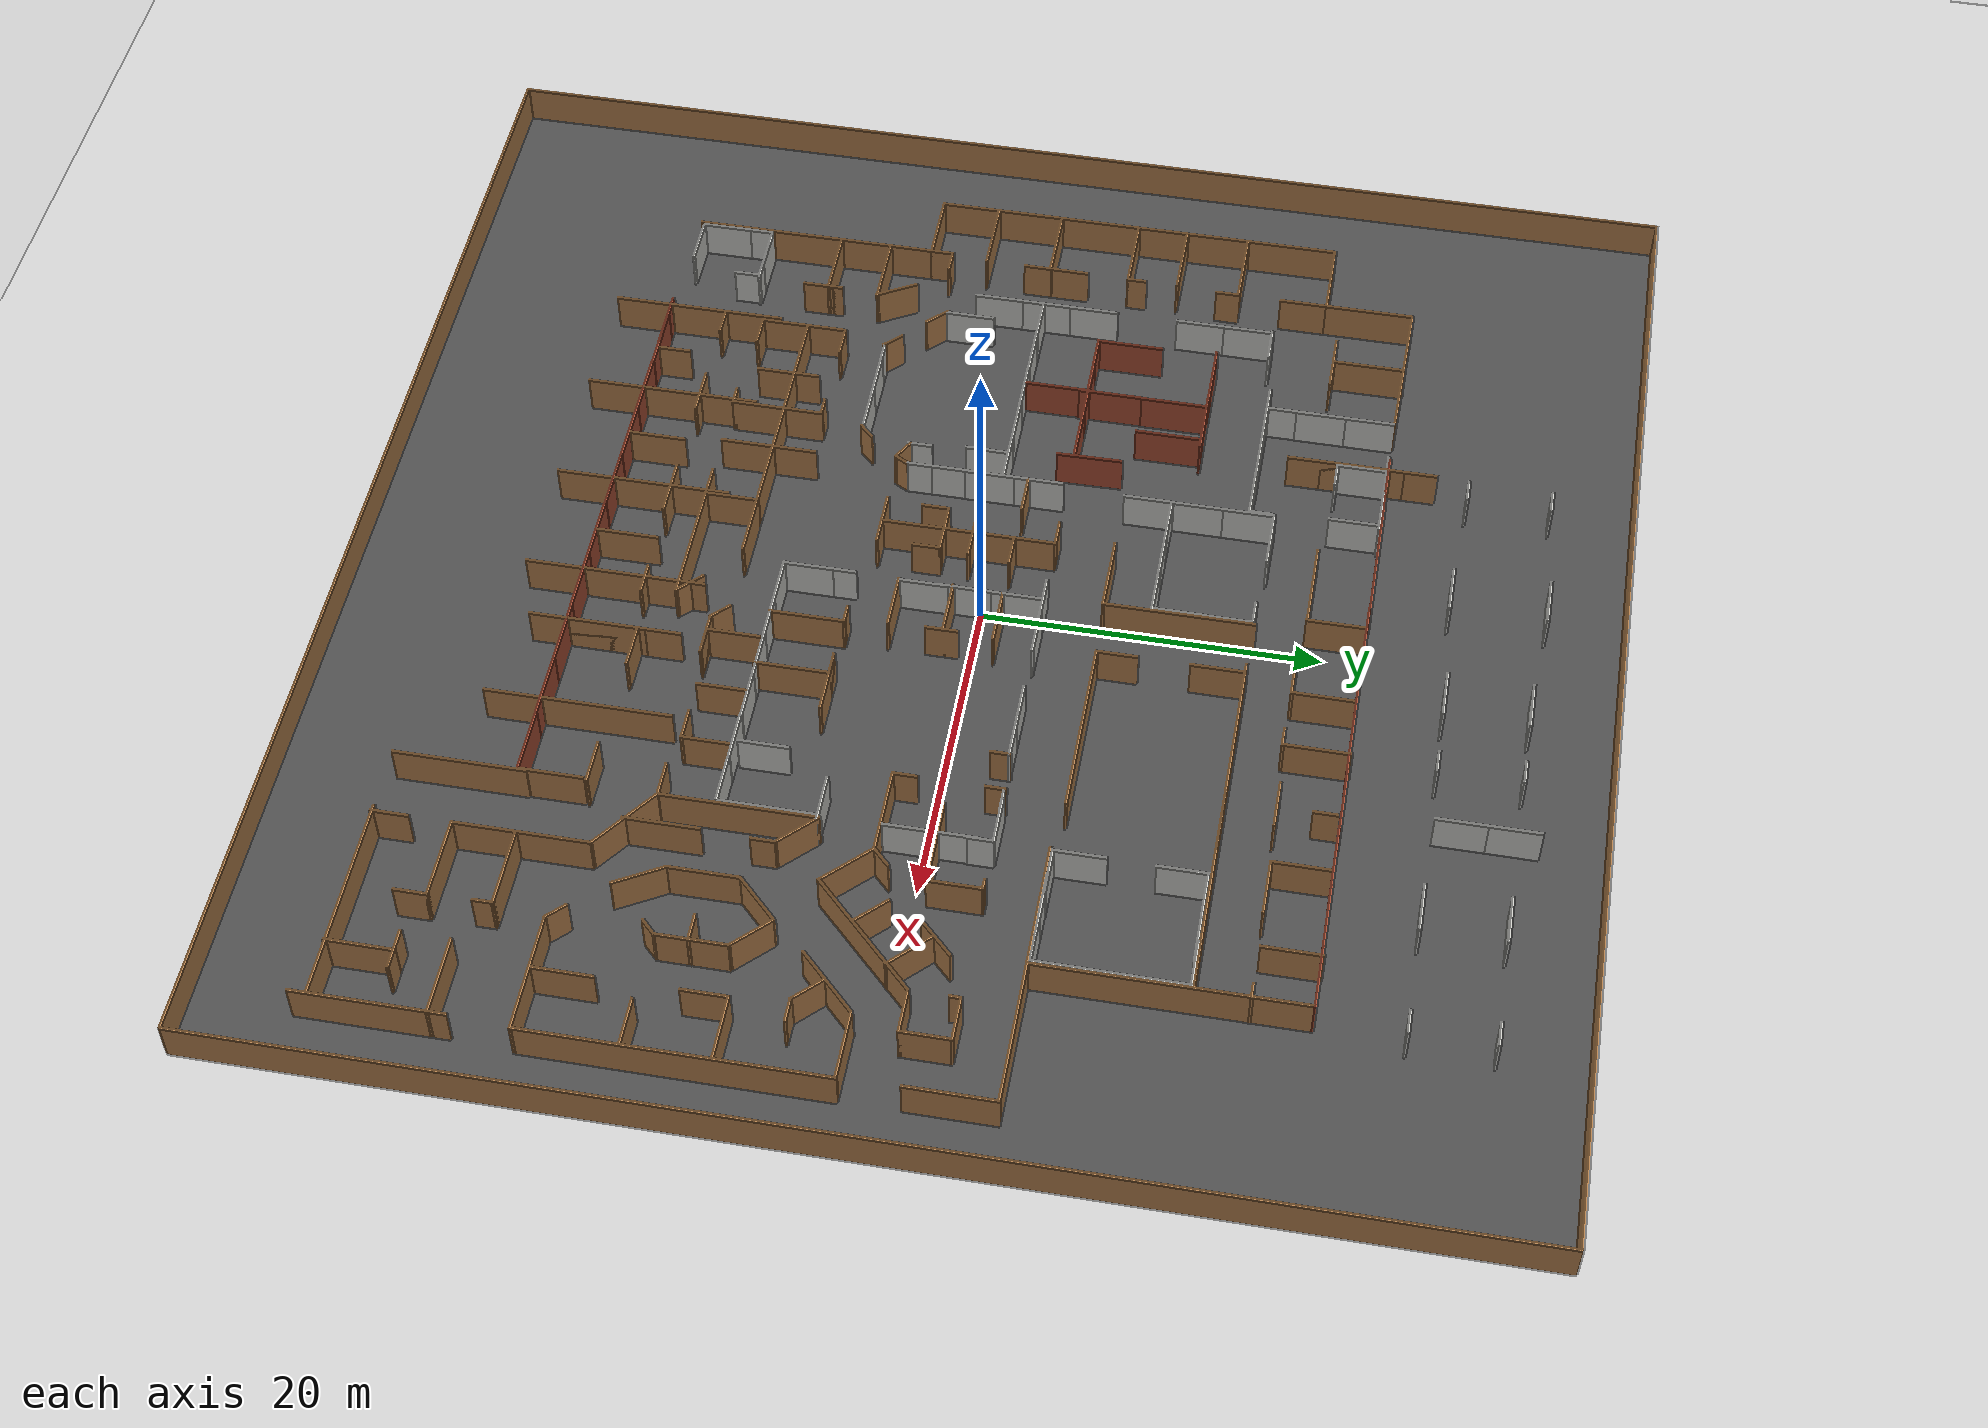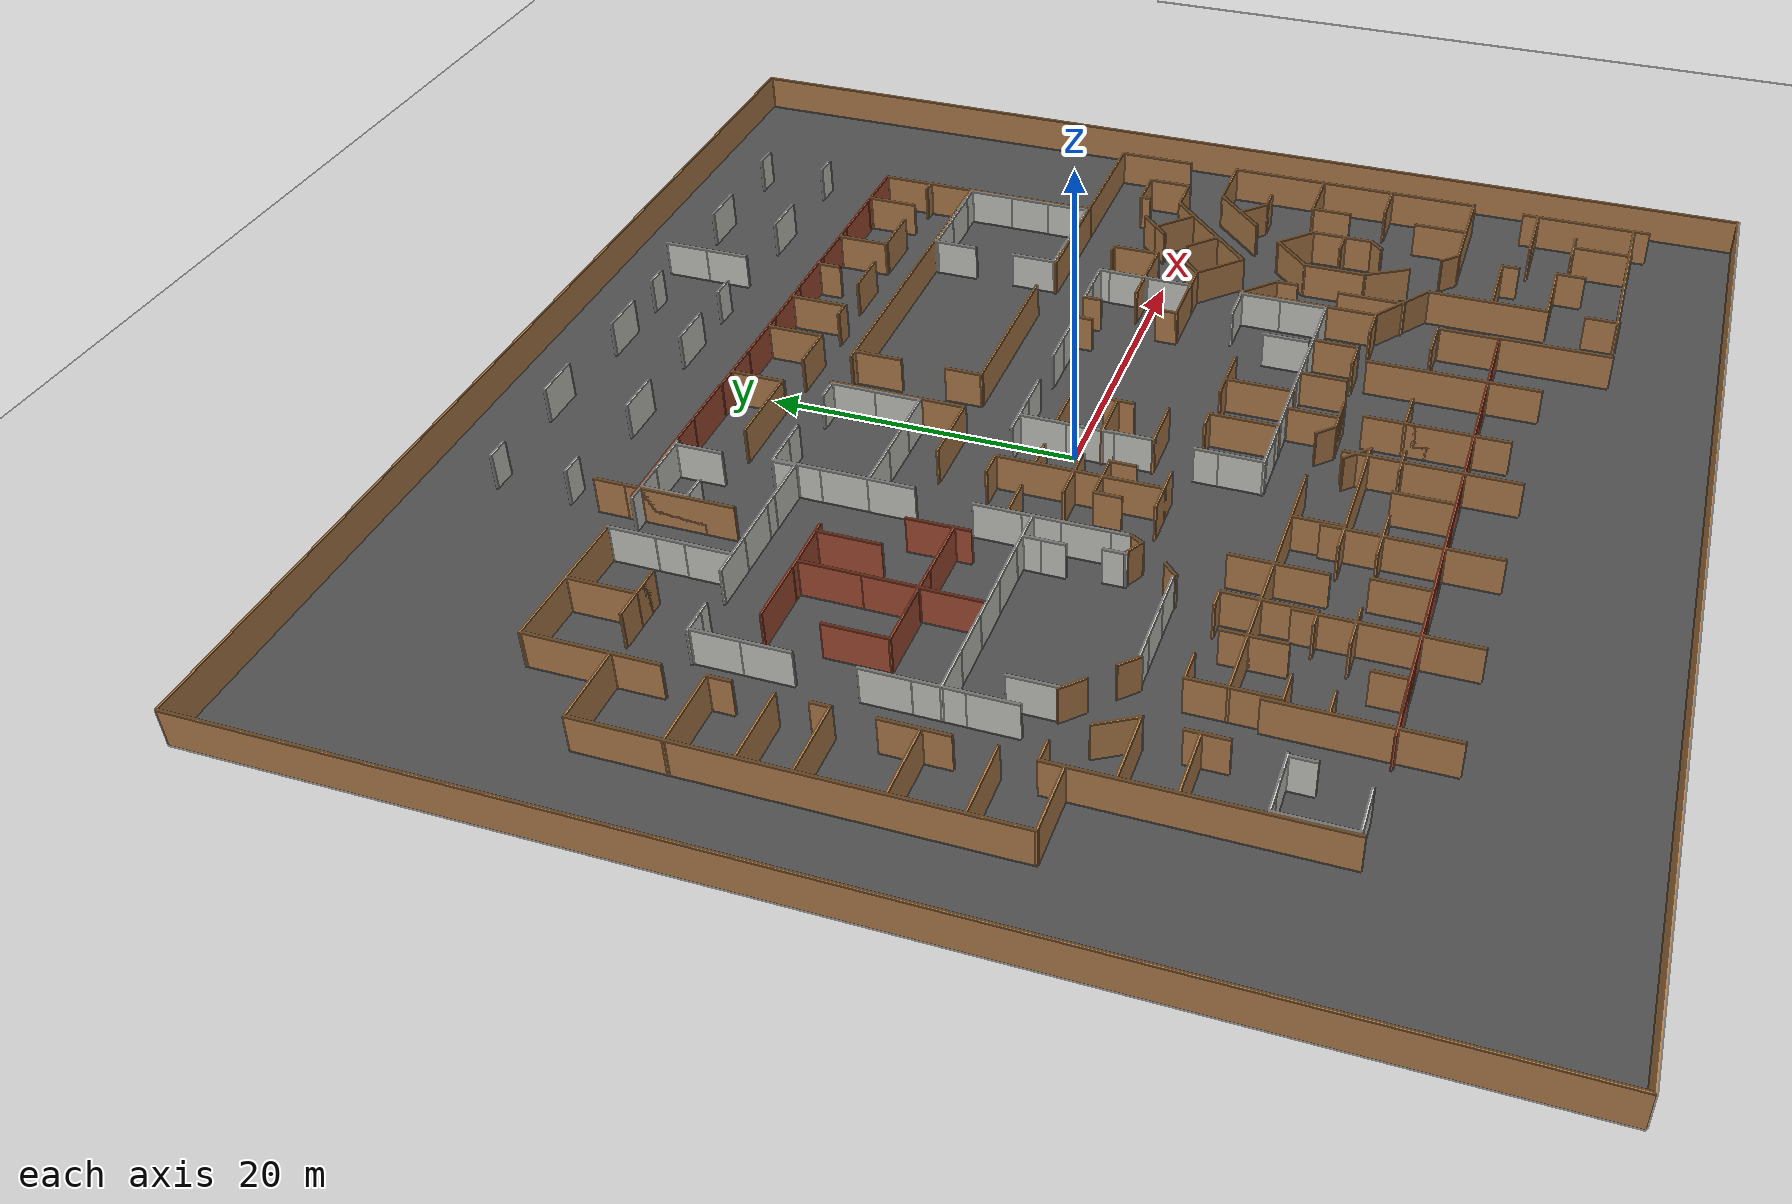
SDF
<sdf version="1.6">
 <world name="default">
  <light name="sun" type="directional">
   <pose>0 0 10 0 -0 0</pose>
   <diffuse>0.8 0.8 0.8 1</diffuse>
   <specular>0.2 0.2 0.2 1</specular>
   <attenuation>
    <range>1000</range>
    <constant>0.9</constant>
    <linear>0.01</linear>
    <quadratic>0.001</quadratic>
   </attenuation>
   <direction>-0.5 0.1 -0.9</direction>
  </light>
  <model name="ground_plane">
   <static>1</static>
   <link name="link">
    <collision name="collision">
     <geometry><plane><normal>0 0 1</normal><size>100 100</size></plane></geometry>
     <surface><friction><ode><mu>100</mu><mu2>50</mu2></ode></friction></surface>
    </collision>
    <visual name="visual">
     <cast_shadows>0</cast_shadows>
     <geometry><plane><normal>0 0 1</normal><size>100 100</size></plane></geometry>
     <material>
      <script><uri>file://media/materials/scripts/gazebo.material</uri><name>Gazebo/Grey</name></script>
     </material>
    </visual>
   </link>
  </model>
  <gravity>0 0 -9.8</gravity>
  <magnetic_field>6e-06 2.3e-05 -4.2e-05</magnetic_field>
  <atmosphere type="adiabatic"/>
  <physics name="default_physics" default="0" type="ode">
   <max_step_size>0.001</max_step_size>
   <real_time_factor>1</real_time_factor>
   <real_time_update_rate>1000</real_time_update_rate>
  </physics>
  <scene><ambient>0.4 0.4 0.4 1</ambient><background>0.7 0.7 0.7 1</background><shadows>1</shadows></scene>
  <audio><device>default</device></audio>
  <spherical_coordinates>
   <surface_model>EARTH_WGS84</surface_model>
   <latitude_deg>0</latitude_deg>
   <longitude_deg>0</longitude_deg>
   <elevation>0</elevation>
   <heading_deg>0</heading_deg>
  </spherical_coordinates>
  <model name="map_frame">
   <link name="Wall_0">
    <collision name="Wall_0_Collision">
     <geometry><box><size>74.05 0.15 2.5</size></box></geometry>
     <pose>0 0 1.25 0 -0 0</pose>
    </collision>
    <visual name="Wall_0_Visual">
     <pose>0 0 1.25 0 -0 0</pose>
     <geometry><box><size>74.05 0.15 2.5</size></box></geometry>
     <material>
      <script><uri>file://media/materials/scripts/gazebo.material</uri><name>Gazebo/Wood</name></script>
      <ambient>1 1 1 1</ambient>
     </material>
    </visual>
    <pose>0 37 0 0 -0 0</pose>
   </link>
   <link name="Wall_1">
    <collision name="Wall_1_Collision">
     <geometry><box><size>74.05 0.15 2.5</size></box></geometry>
     <pose>0 0 1.25 0 -0 0</pose>
    </collision>
    <visual name="Wall_1_Visual">
     <pose>0 0 1.25 0 -0 0</pose>
     <geometry><box><size>74.05 0.15 2.5</size></box></geometry>
     <material>
      <script><uri>file://media/materials/scripts/gazebo.material</uri><name>Gazebo/Wood</name></script>
      <ambient>1 1 1 1</ambient>
     </material>
    </visual>
    <pose>37 0 0 0 0 -1.5708</pose>
   </link>
   <link name="Wall_2">
    <collision name="Wall_2_Collision">
     <geometry><box><size>74.05 0.15 2.5</size></box></geometry>
     <pose>0 0 1.25 0 -0 0</pose>
    </collision>
    <visual name="Wall_2_Visual">
     <pose>0 0 1.25 0 -0 0</pose>
     <geometry><box><size>74.05 0.15 2.5</size></box></geometry>
     <material>
      <script><uri>file://media/materials/scripts/gazebo.material</uri><name>Gazebo/Wood</name></script>
      <ambient>1 1 1 1</ambient>
     </material>
    </visual>
    <pose>0 -37 0 0 -0 3.14159</pose>
   </link>
   <link name="Wall_3">
    <collision name="Wall_3_Collision">
     <geometry><box><size>74.05 0.15 2.5</size></box></geometry>
     <pose>0 0 1.25 0 -0 0</pose>
    </collision>
    <visual name="Wall_3_Visual">
     <pose>0 0 1.25 0 -0 0</pose>
     <geometry><box><size>74.05 0.15 2.5</size></box></geometry>
     <material>
      <script><uri>file://media/materials/scripts/gazebo.material</uri><name>Gazebo/Wood</name></script>
      <ambient>1 1 1 1</ambient>
     </material>
    </visual>
    <pose>-37 0 0 0 -0 1.5708</pose>
   </link>
   <static>1</static>
  </model>
  <model name="asphalt_plane">
   <static>1</static>
   <link name="link">
    <collision name="collision"><geometry><box><size>74 74 0.1</size></box></geometry></collision>
    <visual name="visual">
     <cast_shadows>0</cast_shadows>
     <geometry><box><size>74 74 0.1</size></box></geometry>
     <material>
      <script>
       <uri>model://asphalt_plane/materials/scripts</uri>
       <uri>model://asphalt_plane/materials/textures</uri>
       <name>vrc/asphalt</name>
      </script>
     </material>
    </visual>
   </link>
  </model>
  <model name="concrete_wall">
   <pose>-8.48668 14.4739 0 0 -0 0</pose>
   <link name="Wall_0">
    <collision name="Wall_0_Collision">
     <geometry><box><size>3 0.15 2.5</size></box></geometry>
     <pose>0 0 1.25 0 -0 0</pose>
    </collision>
    <visual name="Wall_0_Visual">
     <pose>0 0 1.25 0 -0 0</pose>
     <geometry><box><size>3 0.15 2.5</size></box></geometry>
     <material>
      <script><uri>file://media/materials/scripts/gazebo.material</uri><name>Gazebo/CeilingTiled</name></script>
      <ambient>1 1 1 1</ambient>
     </material>
     <meta><layer>0</layer></meta>
    </visual>
    <pose>0 0 0 0 -0 1.5708</pose>
   </link>
   <static>1</static>
  </model>
  <model name="concrete_wall_0">
   <pose>-8.48804 11.5232 0 0 -0 0</pose>
   <link name="Wall_0">
    <collision name="Wall_0_Collision">
     <geometry><box><size>3 0.15 2.5</size></box></geometry>
     <pose>0 0 1.25 0 -0 0</pose>
    </collision>
    <visual name="Wall_0_Visual">
     <pose>0 0 1.25 0 -0 0</pose>
     <geometry><box><size>3 0.15 2.5</size></box></geometry>
     <material>
      <script><uri>file://media/materials/scripts/gazebo.material</uri><name>Gazebo/CeilingTiled</name></script>
      <ambient>1 1 1 1</ambient>
     </material>
     <meta><layer>0</layer></meta>
    </visual>
    <pose>0 0 0 0 -0 1.5708</pose>
   </link>
   <static>1</static>
  </model>
  <model name="concrete_wall_1">
   <pose>-0.231026 14.3447 0 0 -0 0</pose>
   <link name="Wall_0">
    <collision name="Wall_0_Collision">
     <geometry><box><size>3 0.15 2.5</size></box></geometry>
     <pose>0 0 1.25 0 -0 0</pose>
    </collision>
    <visual name="Wall_0_Visual">
     <pose>0 0 1.25 0 -0 0</pose>
     <geometry><box><size>3 0.15 2.5</size></box></geometry>
     <material>
      <script><uri>file://media/materials/scripts/gazebo.material</uri><name>Gazebo/CeilingTiled</name></script>
      <ambient>1 1 1 1</ambient>
     </material>
     <meta><layer>0</layer></meta>
    </visual>
    <pose>0 0 0 0 -0 1.5708</pose>
   </link>
   <static>1</static>
  </model>
  <model name="concrete_wall_2">
   <pose>-0.252871 11.4504 0 0 -0 0</pose>
   <link name="Wall_0">
    <collision name="Wall_0_Collision">
     <geometry><box><size>3 0.15 2.5</size></box></geometry>
     <pose>0 0 1.25 0 -0 0</pose>
    </collision>
    <visual name="Wall_0_Visual">
     <pose>0 0 1.25 0 -0 0</pose>
     <geometry><box><size>3 0.15 2.5</size></box></geometry>
     <material>
      <script><uri>file://media/materials/scripts/gazebo.material</uri><name>Gazebo/CeilingTiled</name></script>
      <ambient>1 1 1 1</ambient>
     </material>
     <meta><layer>0</layer></meta>
    </visual>
    <pose>0 0 0 0 -0 1.5708</pose>
   </link>
   <static>1</static>
  </model>
  <model name="concrete_wall_3">
   <pose>-26.6192 -21.1644 0 0 -0 0</pose>
   <link name="Wall_0">
    <collision name="Wall_0_Collision">
     <geometry><box><size>3 0.15 2.5</size></box></geometry>
     <pose>0 0 1.25 0 -0 0</pose>
    </collision>
    <visual name="Wall_0_Visual">
     <pose>0 0 1.25 0 -0 0</pose>
     <geometry><box><size>3 0.15 2.5</size></box></geometry>
     <material>
      <script><uri>file://media/materials/scripts/gazebo.material</uri><name>Gazebo/CeilingTiled</name></script>
      <ambient>1 1 1 1</ambient>
     </material>
     <meta><layer>0</layer></meta>
    </visual>
    <pose>0 0 0 0 -0 1.5708</pose>
   </link>
   <static>1</static>
  </model>
  <model name="concrete_wall_4">
   <pose>-26.6244 -19.6415 0 0 -0 0</pose>
   <link name="Wall_0">
    <collision name="Wall_0_Collision">
     <geometry><box><size>3 0.15 2.5</size></box></geometry>
     <pose>0 0 1.25 0 -0 0</pose>
    </collision>
    <visual name="Wall_0_Visual">
     <pose>0 0 1.25 0 -0 0</pose>
     <geometry><box><size>3 0.15 2.5</size></box></geometry>
     <material>
      <script><uri>file://media/materials/scripts/gazebo.material</uri><name>Gazebo/CeilingTiled</name></script>
      <ambient>1 1 1 1</ambient>
     </material>
     <meta><layer>0</layer></meta>
    </visual>
    <pose>0 0 0 0 -0 1.5708</pose>
   </link>
   <static>1</static>
  </model>
  <model name="concrete_wall_6_clone">
   <pose>-25.1114 -22.6438 0 0 -0 1.57079</pose>
   <link name="Wall_0">
    <collision name="Wall_0_Collision">
     <geometry><box><size>3 0.15 2.5</size></box></geometry>
     <pose>0 0 1.25 0 -0 0</pose>
    </collision>
    <visual name="Wall_0_Visual">
     <pose>0 0 1.25 0 -0 0</pose>
     <geometry><box><size>3 0.15 2.5</size></box></geometry>
     <material>
      <script><uri>file://media/materials/scripts/gazebo.material</uri><name>Gazebo/CeilingTiled</name></script>
      <ambient>1 1 1 1</ambient>
     </material>
     <meta><layer>0</layer></meta>
    </visual>
    <pose>0 0 0 0 -0 1.5708</pose>
   </link>
   <static>1</static>
  </model>
  <model name="concrete_wall_6_clone_0">
   <pose>-25.1351 -18.2014 0 0 -0 1.57079</pose>
   <link name="Wall_0">
    <collision name="Wall_0_Collision">
     <geometry><box><size>3 0.15 2.5</size></box></geometry>
     <pose>0 0 1.25 0 -0 0</pose>
    </collision>
    <visual name="Wall_0_Visual">
     <pose>0 0 1.25 0 -0 0</pose>
     <geometry><box><size>3 0.15 2.5</size></box></geometry>
     <material>
      <script><uri>file://media/materials/scripts/gazebo.material</uri><name>Gazebo/CeilingTiled</name></script>
      <ambient>1 1 1 1</ambient>
     </material>
     <meta><layer>0</layer></meta>
    </visual>
    <pose>0 0 0 0 -0 1.5708</pose>
   </link>
   <static>1</static>
  </model>
  <model name="concrete_wall_6_clone_1">
   <pose>16.3445 -5.99981 0 0 -0 1.57079</pose>
   <link name="Wall_0">
    <collision name="Wall_0_Collision">
     <geometry><box><size>3 0.15 2.5</size></box></geometry>
     <pose>0 0 1.25 0 -0 0</pose>
    </collision>
    <visual name="Wall_0_Visual">
     <pose>0 0 1.25 0 -0 0</pose>
     <geometry><box><size>3 0.15 2.5</size></box></geometry>
     <material>
      <script><uri>file://media/materials/scripts/gazebo.material</uri><name>Gazebo/CeilingTiled</name></script>
      <ambient>1 1 1 1</ambient>
     </material>
     <meta><layer>0</layer></meta>
    </visual>
    <pose>0 0 0 0 -0 1.5708</pose>
   </link>
   <static>1</static>
  </model>
  <model name="concrete_wall_6_clone_2">
   <pose>15.9847 -11.7109 0 0 -0 1.57079</pose>
   <link name="Wall_0">
    <collision name="Wall_0_Collision">
     <geometry><box><size>3 0.15 2.5</size></box></geometry>
     <pose>0 0 1.25 0 -0 0</pose>
    </collision>
    <visual name="Wall_0_Visual">
     <pose>0 0 1.25 0 -0 0</pose>
     <geometry><box><size>3 0.15 2.5</size></box></geometry>
     <material>
      <script><uri>file://media/materials/scripts/gazebo.material</uri><name>Gazebo/CeilingTiled</name></script>
      <ambient>1 1 1 1</ambient>
     </material>
     <meta><layer>0</layer></meta>
    </visual>
    <pose>0 0 0 0 -0 1.5708</pose>
   </link>
   <static>1</static>
  </model>
  <model name="concrete_wall_6_clone_3">
   <pose>13.0011 -11.6986 0 0 -0 1.57079</pose>
   <link name="Wall_0">
    <collision name="Wall_0_Collision">
     <geometry><box><size>3 0.15 2.5</size></box></geometry>
     <pose>0 0 1.25 0 -0 0</pose>
    </collision>
    <visual name="Wall_0_Visual">
     <pose>0 0 1.25 0 -0 0</pose>
     <geometry><box><size>3 0.15 2.5</size></box></geometry>
     <material>
      <script><uri>file://media/materials/scripts/gazebo.material</uri><name>Gazebo/CeilingTiled</name></script>
      <ambient>1 1 1 1</ambient>
     </material>
     <meta><layer>0</layer></meta>
    </visual>
    <pose>0 0 0 0 -0 1.5708</pose>
   </link>
   <static>1</static>
  </model>
  <model name="concrete_wall_7">
   <pose>13.2693 -9.97942 0 0 -0 0</pose>
   <link name="Wall_0">
    <collision name="Wall_0_Collision">
     <geometry><box><size>3 0.15 2.5</size></box></geometry>
     <pose>0 0 1.25 0 -0 0</pose>
    </collision>
    <visual name="Wall_0_Visual">
     <pose>0 0 1.25 0 -0 0</pose>
     <geometry><box><size>3 0.15 2.5</size></box></geometry>
     <material>
      <script><uri>file://media/materials/scripts/gazebo.material</uri><name>Gazebo/CeilingTiled</name></script>
      <ambient>1 1 1 1</ambient>
     </material>
     <meta><layer>0</layer></meta>
    </visual>
    <pose>0 0 0 0 -0 1.5708</pose>
   </link>
   <static>1</static>
  </model>
  <model name="concrete_wall_8">
   <pose>17.5032 -10.1408 0 0 -0 0</pose>
   <link name="Wall_0">
    <collision name="Wall_0_Collision">
     <geometry><box><size>3 0.15 2.5</size></box></geometry>
     <pose>0 0 1.25 0 -0 0</pose>
    </collision>
    <visual name="Wall_0_Visual">
     <pose>0 0 1.25 0 -0 0</pose>
     <geometry><box><size>3 0.15 2.5</size></box></geometry>
     <material>
      <script><uri>file://media/materials/scripts/gazebo.material</uri><name>Gazebo/CeilingTiled</name></script>
      <ambient>1 1 1 1</ambient>
     </material>
     <meta><layer>0</layer></meta>
    </visual>
    <pose>0 0 0 0 -0 1.5708</pose>
   </link>
   <static>1</static>
  </model>
  <model name="concrete_wall_9">
   <pose>17.5144 -7.46989 0 0 -0 0</pose>
   <link name="Wall_0">
    <collision name="Wall_0_Collision">
     <geometry><box><size>3 0.15 2.5</size></box></geometry>
     <pose>0 0 1.25 0 -0 0</pose>
    </collision>
    <visual name="Wall_0_Visual">
     <pose>0 0 1.25 0 -0 0</pose>
     <geometry><box><size>3 0.15 2.5</size></box></geometry>
     <material>
      <script><uri>file://media/materials/scripts/gazebo.material</uri><name>Gazebo/CeilingTiled</name></script>
      <ambient>1 1 1 1</ambient>
     </material>
     <meta><layer>0</layer></meta>
    </visual>
    <pose>0 0 0 0 -0 1.5708</pose>
   </link>
   <static>1</static>
  </model>
  <model name="concrete_wall_6_clone_4">
   <pose>-1.64895 9.93911 0 0 -0 1.57079</pose>
   <link name="Wall_0">
    <collision name="Wall_0_Collision">
     <geometry><box><size>3 0.15 2.5</size></box></geometry>
     <pose>0 0 1.25 0 -0 0</pose>
    </collision>
    <visual name="Wall_0_Visual">
     <pose>0 0 1.25 0 -0 0</pose>
     <geometry><box><size>3 0.15 2.5</size></box></geometry>
     <material>
      <script><uri>file://media/materials/scripts/gazebo.material</uri><name>Gazebo/CeilingTiled</name></script>
      <ambient>1 1 1 1</ambient>
     </material>
     <meta><layer>0</layer></meta>
    </visual>
    <pose>0 0 0 0 -0 1.5708</pose>
   </link>
   <static>1</static>
  </model>
  <model name="concrete_wall_6_clone_5">
   <pose>-4.08866 9.93655 0 0 -0 1.57079</pose>
   <link name="Wall_0">
    <collision name="Wall_0_Collision">
     <geometry><box><size>3 0.15 2.5</size></box></geometry>
     <pose>0 0 1.25 0 -0 0</pose>
    </collision>
    <visual name="Wall_0_Visual">
     <pose>0 0 1.25 0 -0 0</pose>
     <geometry><box><size>3 0.15 2.5</size></box></geometry>
     <material>
      <script><uri>file://media/materials/scripts/gazebo.material</uri><name>Gazebo/CeilingTiled</name></script>
      <ambient>1 1 1 1</ambient>
     </material>
     <meta><layer>0</layer></meta>
    </visual>
    <pose>0 0 0 0 -0 1.5708</pose>
   </link>
   <static>1</static>
  </model>
  <model name="concrete_wall_6_clone_6">
   <pose>-7.05086 9.93464 0 0 -0 1.57079</pose>
   <link name="Wall_0">
    <collision name="Wall_0_Collision">
     <geometry><box><size>3 0.15 2.5</size></box></geometry>
     <pose>0 0 1.25 0 -0 0</pose>
    </collision>
    <visual name="Wall_0_Visual">
     <pose>0 0 1.25 0 -0 0</pose>
     <geometry><box><size>3 0.15 2.5</size></box></geometry>
     <material>
      <script><uri>file://media/materials/scripts/gazebo.material</uri><name>Gazebo/CeilingTiled</name></script>
      <ambient>1 1 1 1</ambient>
     </material>
     <meta><layer>0</layer></meta>
    </visual>
    <pose>0 0 0 0 -0 1.5708</pose>
   </link>
   <static>1</static>
  </model>
  <model name="concrete_wall_6_clone_7">
   <pose>-7.08346 16.0324 0 0 -0 1.57079</pose>
   <link name="Wall_0">
    <collision name="Wall_0_Collision">
     <geometry><box><size>3 0.15 2.5</size></box></geometry>
     <pose>0 0 1.25 0 -0 0</pose>
    </collision>
    <visual name="Wall_0_Visual">
     <pose>0 0 1.25 0 -0 0</pose>
     <geometry><box><size>3 0.15 2.5</size></box></geometry>
     <material>
      <script><uri>file://media/materials/scripts/gazebo.material</uri><name>Gazebo/CeilingTiled</name></script>
      <ambient>1 1 1 1</ambient>
     </material>
     <meta><layer>0</layer></meta>
    </visual>
    <pose>0 0 0 0 -0 1.5708</pose>
   </link>
   <static>1</static>
  </model>
  <model name="concrete_wall_6_clone_8">
   <pose>-1.01529 15.8 0 0 -0 1.57079</pose>
   <link name="Wall_0">
    <collision name="Wall_0_Collision">
     <geometry><box><size>1.5 0.15 2.5</size></box></geometry>
     <pose>0 0 1.25 0 -0 0</pose>
    </collision>
    <visual name="Wall_0_Visual">
     <pose>0 0 1.25 0 -0 0</pose>
     <geometry><box><size>1.5 0.15 2.5</size></box></geometry>
     <material>
      <script><uri>file://media/materials/scripts/gazebo.material</uri><name>Gazebo/CeilingTiled</name></script>
      <ambient>1 1 1 1</ambient>
     </material>
     <meta><layer>0</layer></meta>
    </visual>
    <pose>0 0 0 0 -0 1.5708</pose>
   </link>
   <static>1</static>
  </model>
  <model name="concrete_wall_6_clone_9">
   <pose>-17.1164 14.5581 0 0 -0 1.57079</pose>
   <link name="Wall_0">
    <collision name="Wall_0_Collision">
     <geometry><box><size>3 0.15 2.5</size></box></geometry>
     <pose>0 0 1.25 0 -0 0</pose>
    </collision>
    <visual name="Wall_0_Visual">
     <pose>0 0 1.25 0 -0 0</pose>
     <geometry><box><size>3 0.15 2.5</size></box></geometry>
     <material>
      <script><uri>file://media/materials/scripts/gazebo.material</uri><name>Gazebo/CeilingTiled</name></script>
      <ambient>1 1 1 1</ambient>
     </material>
     <meta><layer>0</layer></meta>
    </visual>
    <pose>0 0 0 0 -0 1.5708</pose>
   </link>
   <static>1</static>
  </model>
  <model name="concrete_wall_6_clone_10">
   <pose>-14.1567 14.5575 0 0 -0 1.57079</pose>
   <link name="Wall_0">
    <collision name="Wall_0_Collision">
     <geometry><box><size>3 0.15 2.5</size></box></geometry>
     <pose>0 0 1.25 0 -0 0</pose>
    </collision>
    <visual name="Wall_0_Visual">
     <pose>0 0 1.25 0 -0 0</pose>
     <geometry><box><size>3 0.15 2.5</size></box></geometry>
     <material>
      <script><uri>file://media/materials/scripts/gazebo.material</uri><name>Gazebo/CeilingTiled</name></script>
      <ambient>1 1 1 1</ambient>
     </material>
     <meta><layer>0</layer></meta>
    </visual>
    <pose>0 0 0 0 -0 1.5708</pose>
   </link>
   <static>1</static>
  </model>
  <model name="concrete_wall_6_clone_11">
   <pose>-10.1743 14.5482 0 0 -0 1.57079</pose>
   <link name="Wall_0">
    <collision name="Wall_0_Collision">
     <geometry><box><size>3 0.15 2.5</size></box></geometry>
     <pose>0 0 1.25 0 -0 0</pose>
    </collision>
    <visual name="Wall_0_Visual">
     <pose>0 0 1.25 0 -0 0</pose>
     <geometry><box><size>3 0.15 2.5</size></box></geometry>
     <material>
      <script><uri>file://media/materials/scripts/gazebo.material</uri><name>Gazebo/CeilingTiled</name></script>
      <ambient>1 1 1 1</ambient>
     </material>
     <meta><layer>0</layer></meta>
    </visual>
    <pose>0 0 0 0 -0 1.5708</pose>
   </link>
   <static>1</static>
  </model>
  <model name="concrete_wall_6_clone_12">
   <pose>-10.0053 22.2075 0 0 -0 1.57079</pose>
   <link name="Wall_0">
    <collision name="Wall_0_Collision">
     <geometry><box><size>3 0.15 2.5</size></box></geometry>
     <pose>0 0 1.25 0 -0 0</pose>
    </collision>
    <visual name="Wall_0_Visual">
     <pose>0 0 1.25 0 -0 0</pose>
     <geometry><box><size>3 0.15 2.5</size></box></geometry>
     <material>
      <script><uri>file://media/materials/scripts/gazebo.material</uri><name>Gazebo/CeilingTiled</name></script>
      <ambient>1 1 1 1</ambient>
     </material>
     <meta><layer>0</layer></meta>
    </visual>
    <pose>0 0 0 0 -0 1.5708</pose>
   </link>
   <static>1</static>
  </model>
  <model name="concrete_wall_6_clone_13">
   <pose>-12.862 22.2193 0 0 -0 1.57079</pose>
   <link name="Wall_0">
    <collision name="Wall_0_Collision">
     <geometry><box><size>3 0.15 2.5</size></box></geometry>
     <pose>0 0 1.25 0 -0 0</pose>
    </collision>
    <visual name="Wall_0_Visual">
     <pose>0 0 1.25 0 -0 0</pose>
     <geometry><box><size>3 0.15 2.5</size></box></geometry>
     <material>
      <script><uri>file://media/materials/scripts/gazebo.material</uri><name>Gazebo/CeilingTiled</name></script>
      <ambient>1 1 1 1</ambient>
     </material>
     <meta><layer>0</layer></meta>
    </visual>
    <pose>0 0 0 0 -0 1.5708</pose>
   </link>
   <static>1</static>
  </model>
  <model name="concrete_wall_10">
   <pose>-17.0452 17.8135 0 0 -0 0</pose>
   <link name="Wall_0">
    <collision name="Wall_0_Collision">
     <geometry><box><size>3 0.15 2.5</size></box></geometry>
     <pose>0 0 1.25 0 -0 0</pose>
    </collision>
    <visual name="Wall_0_Visual">
     <pose>0 0 1.25 0 -0 0</pose>
     <geometry><box><size>3 0.15 2.5</size></box></geometry>
     <material>
      <script><uri>file://media/materials/scripts/gazebo.material</uri><name>Gazebo/CeilingTiled</name></script>
      <ambient>1 1 1 1</ambient>
     </material>
     <meta><layer>0</layer></meta>
    </visual>
    <pose>0 0 0 0 -0 1.5708</pose>
   </link>
   <static>1</static>
  </model>
  <model name="concrete_wall_11">
   <pose>-17.0415 20.8179 0 0 -0 0</pose>
   <link name="Wall_0">
    <collision name="Wall_0_Collision">
     <geometry><box><size>3 0.15 2.5</size></box></geometry>
     <pose>0 0 1.25 0 -0 0</pose>
    </collision>
    <visual name="Wall_0_Visual">
     <pose>0 0 1.25 0 -0 0</pose>
     <geometry><box><size>3 0.15 2.5</size></box></geometry>
     <material>
      <script><uri>file://media/materials/scripts/gazebo.material</uri><name>Gazebo/CeilingTiled</name></script>
      <ambient>1 1 1 1</ambient>
     </material>
     <meta><layer>0</layer></meta>
    </visual>
    <pose>0 0 0 0 -0 1.5708</pose>
   </link>
   <static>1</static>
  </model>
  <model name="concrete_wall_12">
   <pose>-8.84643 20.6774 0 0 -0 0</pose>
   <link name="Wall_0">
    <collision name="Wall_0_Collision">
     <geometry><box><size>3 0.15 2.5</size></box></geometry>
     <pose>0 0 1.25 0 -0 0</pose>
    </collision>
    <visual name="Wall_0_Visual">
     <pose>0 0 1.25 0 -0 0</pose>
     <geometry><box><size>3 0.15 2.5</size></box></geometry>
     <material>
      <script><uri>file://media/materials/scripts/gazebo.material</uri><name>Gazebo/CeilingTiled</name></script>
      <ambient>1 1 1 1</ambient>
     </material>
     <meta><layer>0</layer></meta>
    </visual>
    <pose>0 0 0 0 -0 1.5708</pose>
   </link>
   <static>1</static>
  </model>
  <model name="concrete_wall_13">
   <pose>-17.0666 16.0035 0 0 -0 0</pose>
   <link name="Wall_0">
    <collision name="Wall_0_Collision">
     <geometry><box><size>3 0.15 2.5</size></box></geometry>
     <pose>0 0 1.25 0 -0 0</pose>
    </collision>
    <visual name="Wall_0_Visual">
     <pose>0 0 1.25 0 -0 0</pose>
     <geometry><box><size>3 0.15 2.5</size></box></geometry>
     <material>
      <script><uri>file://media/materials/scripts/gazebo.material</uri><name>Gazebo/CeilingTiled</name></script>
      <ambient>1 1 1 1</ambient>
     </material>
     <meta><layer>0</layer></meta>
    </visual>
    <pose>0 0 0 0 -0 1.5708</pose>
   </link>
   <static>1</static>
  </model>
  <model name="concrete_wall_14">
   <pose>-13.1615 20.7156 0 0 -0 0</pose>
   <link name="Wall_0">
    <collision name="Wall_0_Collision">
     <geometry><box><size>3 0.15 2.5</size></box></geometry>
     <pose>0 0 1.25 0 -0 0</pose>
    </collision>
    <visual name="Wall_0_Visual">
     <pose>0 0 1.25 0 -0 0</pose>
     <geometry><box><size>3 0.15 2.5</size></box></geometry>
     <material>
      <script><uri>file://media/materials/scripts/gazebo.material</uri><name>Gazebo/CeilingTiled</name></script>
      <ambient>1 1 1 1</ambient>
     </material>
     <meta><layer>0</layer></meta>
    </visual>
    <pose>0 0 0 0 -0 1.5708</pose>
   </link>
   <static>1</static>
  </model>
  <model name="concrete_wall_6_clone_15">
   <pose>19.0082 7.09385 0 0 -0 1.57079</pose>
   <link name="Wall_0">
    <collision name="Wall_0_Collision">
     <geometry><box><size>3 0.15 2.5</size></box></geometry>
     <pose>0 0 1.25 0 -0 0</pose>
    </collision>
    <visual name="Wall_0_Visual">
     <pose>0 0 1.25 0 -0 0</pose>
     <geometry><box><size>3 0.15 2.5</size></box></geometry>
     <material>
      <script><uri>file://media/materials/scripts/gazebo.material</uri><name>Gazebo/CeilingTiled</name></script>
      <ambient>1 1 1 1</ambient>
     </material>
     <meta><layer>0</layer></meta>
    </visual>
    <pose>0 0 0 0 -0 1.5708</pose>
   </link>
   <static>1</static>
  </model>
  <model name="concrete_wall_6_clone_16">
   <pose>20.5949 7.06095 0 0 -0 1.57079</pose>
   <link name="Wall_0">
    <collision name="Wall_0_Collision">
     <geometry><box><size>3 0.15 2.5</size></box></geometry>
     <pose>0 0 1.25 0 -0 0</pose>
    </collision>
    <visual name="Wall_0_Visual">
     <pose>0 0 1.25 0 -0 0</pose>
     <geometry><box><size>3 0.15 2.5</size></box></geometry>
     <material>
      <script><uri>file://media/materials/scripts/gazebo.material</uri><name>Gazebo/CeilingTiled</name></script>
      <ambient>1 1 1 1</ambient>
     </material>
     <meta><layer>0</layer></meta>
    </visual>
    <pose>0 0 0 0 -0 1.5708</pose>
   </link>
   <static>1</static>
  </model>
  <model name="concrete_wall_6_clone_17">
   <pose>23.3706 7.05229 0 0 -0 1.57079</pose>
   <link name="Wall_0">
    <collision name="Wall_0_Collision">
     <geometry><box><size>3 0.15 2.5</size></box></geometry>
     <pose>0 0 1.25 0 -0 0</pose>
    </collision>
    <visual name="Wall_0_Visual">
     <pose>0 0 1.25 0 -0 0</pose>
     <geometry><box><size>3 0.15 2.5</size></box></geometry>
     <material>
      <script><uri>file://media/materials/scripts/gazebo.material</uri><name>Gazebo/CeilingTiled</name></script>
      <ambient>1 1 1 1</ambient>
     </material>
     <meta><layer>0</layer></meta>
    </visual>
    <pose>0 0 0 0 -0 1.5708</pose>
   </link>
   <static>1</static>
  </model>
  <model name="concrete_wall_6_clone_18">
   <pose>23.5039 15.7147 0 0 -0 1.57079</pose>
   <link name="Wall_0">
    <collision name="Wall_0_Collision">
     <geometry><box><size>3 0.15 2.5</size></box></geometry>
     <pose>0 0 1.25 0 -0 0</pose>
    </collision>
    <visual name="Wall_0_Visual">
     <pose>0 0 1.25 0 -0 0</pose>
     <geometry><box><size>3 0.15 2.5</size></box></geometry>
     <material>
      <script><uri>file://media/materials/scripts/gazebo.material</uri><name>Gazebo/CeilingTiled</name></script>
      <ambient>1 1 1 1</ambient>
     </material>
     <meta><layer>0</layer></meta>
    </visual>
    <pose>0 0 0 0 -0 1.5708</pose>
   </link>
   <static>1</static>
  </model>
  <model name="concrete_wall_6_clone_19">
   <pose>21.9639 15.6573 0 0 -0 1.57079</pose>
   <link name="Wall_0">
    <collision name="Wall_0_Collision">
     <geometry><box><size>3 0.15 2.5</size></box></geometry>
     <pose>0 0 1.25 0 -0 0</pose>
    </collision>
    <visual name="Wall_0_Visual">
     <pose>0 0 1.25 0 -0 0</pose>
     <geometry><box><size>3 0.15 2.5</size></box></geometry>
     <material>
      <script><uri>file://media/materials/scripts/gazebo.material</uri><name>Gazebo/CeilingTiled</name></script>
      <ambient>1 1 1 1</ambient>
     </material>
     <meta><layer>0</layer></meta>
    </visual>
    <pose>0 0 0 0 -0 1.5708</pose>
   </link>
   <static>1</static>
  </model>
  <model name="concrete_wall_6_clone_20">
   <pose>19.0587 15.6479 0 0 -0 1.57079</pose>
   <link name="Wall_0">
    <collision name="Wall_0_Collision">
     <geometry><box><size>3 0.15 2.5</size></box></geometry>
     <pose>0 0 1.25 0 -0 0</pose>
    </collision>
    <visual name="Wall_0_Visual">
     <pose>0 0 1.25 0 -0 0</pose>
     <geometry><box><size>3 0.15 2.5</size></box></geometry>
     <material>
      <script><uri>file://media/materials/scripts/gazebo.material</uri><name>Gazebo/CeilingTiled</name></script>
      <ambient>1 1 1 1</ambient>
     </material>
     <meta><layer>0</layer></meta>
    </visual>
    <pose>0 0 0 0 -0 1.5708</pose>
   </link>
   <static>1</static>
  </model>
  <model name="concrete_wall_15">
   <pose>24.8729 8.48253 0 0 -0 0</pose>
   <link name="Wall_0">
    <collision name="Wall_0_Collision">
     <geometry><box><size>3 0.15 2.5</size></box></geometry>
     <pose>0 0 1.25 0 -0 0</pose>
    </collision>
    <visual name="Wall_0_Visual">
     <pose>0 0 1.25 0 -0 0</pose>
     <geometry><box><size>3 0.15 2.5</size></box></geometry>
     <material>
      <script><uri>file://media/materials/scripts/gazebo.material</uri><name>Gazebo/CeilingTiled</name></script>
      <ambient>1 1 1 1</ambient>
     </material>
     <meta><layer>0</layer></meta>
    </visual>
    <pose>0 0 0 0 -0 1.5708</pose>
   </link>
   <static>1</static>
  </model>
  <model name="concrete_wall_16">
   <pose>17.5839 8.5954 0 0 -0 0</pose>
   <link name="Wall_0">
    <collision name="Wall_0_Collision">
     <geometry><box><size>3 0.15 2.5</size></box></geometry>
     <pose>0 0 1.25 0 -0 0</pose>
    </collision>
    <visual name="Wall_0_Visual">
     <pose>0 0 1.25 0 -0 0</pose>
     <geometry><box><size>3 0.15 2.5</size></box></geometry>
     <material>
      <script><uri>file://media/materials/scripts/gazebo.material</uri><name>Gazebo/CeilingTiled</name></script>
      <ambient>1 1 1 1</ambient>
     </material>
     <meta><layer>0</layer></meta>
    </visual>
    <pose>0 0 0 0 -0 1.5708</pose>
   </link>
   <static>1</static>
  </model>
  <model name="concrete_wall_18">
   <pose>17.6374 14.261 0 0 -0 0</pose>
   <link name="Wall_0">
    <collision name="Wall_0_Collision">
     <geometry><box><size>3 0.15 2.5</size></box></geometry>
     <pose>0 0 1.25 0 -0 0</pose>
    </collision>
    <visual name="Wall_0_Visual">
     <pose>0 0 1.25 0 -0 0</pose>
     <geometry><box><size>3 0.15 2.5</size></box></geometry>
     <material>
      <script><uri>file://media/materials/scripts/gazebo.material</uri><name>Gazebo/CeilingTiled</name></script>
      <ambient>1 1 1 1</ambient>
     </material>
     <meta><layer>0</layer></meta>
    </visual>
    <pose>0 0 0 0 -0 1.5708</pose>
   </link>
   <static>1</static>
  </model>
  <model name="concrete_wall_19">
   <pose>24.8866 11.194 0 0 -0 0</pose>
   <link name="Wall_0">
    <collision name="Wall_0_Collision">
     <geometry><box><size>3 0.15 2.5</size></box></geometry>
     <pose>0 0 1.25 0 -0 0</pose>
    </collision>
    <visual name="Wall_0_Visual">
     <pose>0 0 1.25 0 -0 0</pose>
     <geometry><box><size>3 0.15 2.5</size></box></geometry>
     <material>
      <script><uri>file://media/materials/scripts/gazebo.material</uri><name>Gazebo/CeilingTiled</name></script>
      <ambient>1 1 1 1</ambient>
     </material>
     <meta><layer>0</layer></meta>
    </visual>
    <pose>0 0 0 0 -0 1.5708</pose>
   </link>
   <static>1</static>
  </model>
  <model name="concrete_wall_20">
   <pose>24.896 14.1844 0 0 -0 0</pose>
   <link name="Wall_0">
    <collision name="Wall_0_Collision">
     <geometry><box><size>3 0.15 2.5</size></box></geometry>
     <pose>0 0 1.25 0 -0 0</pose>
    </collision>
    <visual name="Wall_0_Visual">
     <pose>0 0 1.25 0 -0 0</pose>
     <geometry><box><size>3 0.15 2.5</size></box></geometry>
     <material>
      <script><uri>file://media/materials/scripts/gazebo.material</uri><name>Gazebo/CeilingTiled</name></script>
      <ambient>1 1 1 1</ambient>
     </material>
     <meta><layer>0</layer></meta>
    </visual>
    <pose>0 0 0 0 -0 1.5708</pose>
   </link>
   <static>1</static>
  </model>
  <model name="willowgarage_v1_1">
   <pose>-14.3408 -3.86286 0 0 -0 0</pose>
   <link name="Wall_10">
    <collision name="Wall_10_Collision">
     <geometry><box><size>25.25 0.15 2.5</size></box></geometry>
     <pose>0 0 1.25 0 -0 0</pose>
    </collision>
    <visual name="Wall_10_Visual">
     <pose>0 0 1.25 0 -0 0</pose>
     <geometry><box><size>25.25 0.15 2.5</size></box></geometry>
     <material>
      <script><uri>file://media/materials/scripts/gazebo.material</uri><name>Gazebo/Wood</name></script>
      <ambient>1 1 1 1</ambient>
     </material>
     <meta><layer>0</layer></meta>
    </visual>
    <pose>-16.8068 8.447 0 0 -0 1.5708</pose>
   </link>
   <link name="Wall_100">
    <collision name="Wall_100_Collision">
     <geometry><box><size>3.5 0.15 2.5</size></box></geometry>
     <pose>0 0 1.25 0 -0 0</pose>
    </collision>
    <visual name="Wall_100_Visual">
     <pose>0 0 1.25 0 -0 0</pose>
     <geometry><box><size>3.5 0.15 2.5</size></box></geometry>
     <material>
      <script><uri>file://media/materials/scripts/gazebo.material</uri><name>Gazebo/Wood</name></script>
      <ambient>1 1 1 1</ambient>
     </material>
     <meta><layer>0</layer></meta>
    </visual>
    <pose>32.2598 22.7229 0 0 -0 3.14159</pose>
   </link>
   <link name="Wall_101">
    <collision name="Wall_101_Collision">
     <geometry><box><size>3.5 0.15 2.5</size></box></geometry>
     <pose>0 0 1.25 0 -0 0</pose>
    </collision>
    <visual name="Wall_101_Visual">
     <pose>0 0 1.25 0 -0 0</pose>
     <geometry><box><size>3.5 0.15 2.5</size></box></geometry>
     <material>
      <script><uri>file://media/materials/scripts/gazebo.material</uri><name>Gazebo/Wood</name></script>
      <ambient>1 1 1 1</ambient>
     </material>
     <meta><layer>0</layer></meta>
    </visual>
    <pose>30.5848 24.3979 0 0 -0 1.5708</pose>
   </link>
   <link name="Wall_105">
    <collision name="Wall_105_Collision">
     <geometry><box><size>3 0.15 2.5</size></box></geometry>
     <pose>0 0 1.25 0 -0 0</pose>
    </collision>
    <visual name="Wall_105_Visual">
     <pose>0 0 1.25 0 -0 0</pose>
     <geometry><box><size>3 0.15 2.5</size></box></geometry>
     <material>
      <script><uri>file://media/materials/scripts/gazebo.material</uri><name>Gazebo/Wood</name></script>
      <ambient>1 1 1 1</ambient>
     </material>
     <meta><layer>0</layer></meta>
    </visual>
    <pose>26.6647 22.5998 0 0 -0 3.14159</pose>
   </link>
   <link name="Wall_107">
    <collision name="Wall_107_Collision">
     <geometry><box><size>1.5 0.15 2.5</size></box></geometry>
     <pose>0 0 1.25 0 -0 0</pose>
    </collision>
    <visual name="Wall_107_Visual">
     <pose>0 0 1.25 0 -0 0</pose>
     <geometry><box><size>1.5 0.15 2.5</size></box></geometry>
     <material>
      <script><uri>file://media/materials/scripts/gazebo.material</uri><name>Gazebo/Wood</name></script>
      <ambient>1 1 1 1</ambient>
     </material>
     <meta><layer>0</layer></meta>
    </visual>
    <pose>26.8591 25.3088 0 0 0 -1.5708</pose>
   </link>
   <link name="Wall_109">
    <collision name="Wall_109_Collision">
     <geometry><box><size>4 0.15 2.5</size></box></geometry>
     <pose>0 0 1.25 0 -0 0</pose>
    </collision>
    <visual name="Wall_109_Visual">
     <pose>0 0 1.25 0 -0 0</pose>
     <geometry><box><size>4 0.15 2.5</size></box></geometry>
     <material>
      <script><uri>file://media/materials/scripts/gazebo.material</uri><name>Gazebo/Wood</name></script>
      <ambient>1 1 1 1</ambient>
     </material>
     <meta><layer>0</layer></meta>
    </visual>
    <pose>22.5522 24.305 0 0 0 -1.5708</pose>
   </link>
   <link name="Wall_11">
    <collision name="Wall_11_Collision">
     <geometry><box><size>5 0.15 2.5</size></box></geometry>
     <pose>0 0 1.25 0 -0 0</pose>
    </collision>
    <visual name="Wall_11_Visual">
     <pose>0 0 1.25 0 -0 0</pose>
     <geometry><box><size>5 0.15 2.5</size></box></geometry>
     <material>
      <script><uri>file://media/materials/scripts/gazebo.material</uri><name>Gazebo/Wood</name></script>
      <ambient>1 1 1 1</ambient>
     </material>
     <meta><layer>0</layer></meta>
    </visual>
    <pose>-14.3818 20.997 0 0 -0 0</pose>
   </link>
   <link name="Wall_110">
    <collision name="Wall_110_Collision">
     <geometry><box><size>1.25 0.15 2.5</size></box></geometry>
     <pose>0 0 1.25 0 -0 0</pose>
    </collision>
    <visual name="Wall_110_Visual">
     <pose>0 0 1.25 0 -0 0</pose>
     <geometry><box><size>1.25 0.15 2.5</size></box></geometry>
     <material>
      <script><uri>file://media/materials/scripts/gazebo.material</uri><name>Gazebo/Wood</name></script>
      <ambient>1 1 1 1</ambient>
     </material>
     <meta><layer>0</layer></meta>
    </visual>
    <pose>22.0022 22.38 0 0 -0 3.14159</pose>
   </link>
   <link name="Wall_112">
    <collision name="Wall_112_Collision">
     <geometry><box><size>3.75 0.15 2.5</size></box></geometry>
     <pose>0 0 1.25 0 -0 0</pose>
    </collision>
    <visual name="Wall_112_Visual">
     <pose>0 0 1.25 0 -0 0</pose>
     <geometry><box><size>3.75 0.15 2.5</size></box></geometry>
     <material>
      <script><uri>file://media/materials/scripts/gazebo.material</uri><name>Gazebo/Wood</name></script>
      <ambient>1 1 1 1</ambient>
     </material>
     <meta><layer>0</layer></meta>
    </visual>
    <pose>18.799 24.2454 0 0 0 -1.5708</pose>
   </link>
   <link name="Wall_113">
    <collision name="Wall_113_Collision">
     <geometry><box><size>3 0.15 2.5</size></box></geometry>
     <pose>0 0 1.25 0 -0 0</pose>
    </collision>
    <visual name="Wall_113_Visual">
     <pose>0 0 1.25 0 -0 0</pose>
     <geometry><box><size>3 0.15 2.5</size></box></geometry>
     <material>
      <script><uri>file://media/materials/scripts/gazebo.material</uri><name>Gazebo/Wood</name></script>
      <ambient>1 1 1 1</ambient>
     </material>
     <meta><layer>0</layer></meta>
    </visual>
    <pose>17.374 22.4454 0 0 -0 3.14159</pose>
   </link>
   <link name="Wall_115">
    <collision name="Wall_115_Collision">
     <geometry><box><size>3.5 0.15 2.5</size></box></geometry>
     <pose>0 0 1.25 0 -0 0</pose>
    </collision>
    <visual name="Wall_115_Visual">
     <pose>0 0 1.25 0 -0 0</pose>
     <geometry><box><size>3.5 0.15 2.5</size></box></geometry>
     <material>
      <script><uri>file://media/materials/scripts/gazebo.material</uri><name>Gazebo/Wood</name></script>
      <ambient>1 1 1 1</ambient>
     </material>
     <meta><layer>0</layer></meta>
    </visual>
    <pose>13.3845 24.3704 0 0 0 -1.5708</pose>
   </link>
   <link name="Wall_119">
    <collision name="Wall_119_Collision">
     <geometry><box><size>0.15 0.15 2.5</size></box></geometry>
     <pose>0 0 1.25 0 -0 0</pose>
    </collision>
    <visual name="Wall_119_Visual">
     <pose>0 0 1.25 0 -0 0</pose>
     <geometry><box><size>0.15 0.15 2.5</size></box></geometry>
     <material>
      <script><uri>file://media/materials/scripts/gazebo.material</uri><name>Gazebo/Wood</name></script>
      <ambient>1 1 1 1</ambient>
     </material>
     <meta><layer>0</layer></meta>
    </visual>
    <pose>1.0355 26.1459 0 0 -0 0</pose>
   </link>
   <link name="Wall_1811">
    <collision name="Wall_1811_Collision">
     <geometry><box><size>5 0.15 2.5</size></box></geometry>
     <pose>0 0 1.25 0 -0 0</pose>
    </collision>
    <visual name="Wall_1811_Visual">
     <pose>0 0 1.25 0 -0 0</pose>
     <geometry><box><size>5 0.15 2.5</size></box></geometry>
     <material>
      <script><uri>file://media/materials/scripts/gazebo.material</uri><name>Gazebo/Wood</name></script>
      <ambient>1 1 1 1</ambient>
     </material>
     <meta><layer>0</layer></meta>
    </visual>
    <pose>1.0355 24.5959 0 0 0 -1.5708</pose>
   </link>
   <link name="Wall_9611">
    <collision name="Wall_9611_Collision">
     <geometry><box><size>5 0.15 2.5</size></box></geometry>
     <pose>0 0 1.25 0 -0 0</pose>
    </collision>
    <visual name="Wall_9611_Visual">
     <pose>0 0 1.25 0 -0 0</pose>
     <geometry><box><size>5 0.15 2.5</size></box></geometry>
     <material>
      <script><uri>file://media/materials/scripts/gazebo.material</uri><name>Gazebo/Wood</name></script>
      <ambient>1 1 1 1</ambient>
     </material>
     <meta><layer>0</layer></meta>
    </visual>
    <pose>1.0355 24.5959 0 0 0 -1.5708</pose>
   </link>
   <link name="Wall_10111">
    <collision name="Wall_10111_Collision">
     <geometry><box><size>5 0.15 2.5</size></box></geometry>
     <pose>0 0 1.25 0 -0 0</pose>
    </collision>
    <visual name="Wall_10111_Visual">
     <pose>0 0 1.25 0 -0 0</pose>
     <geometry><box><size>5 0.15 2.5</size></box></geometry>
     <material>
      <script><uri>file://media/materials/scripts/gazebo.material</uri><name>Gazebo/Wood</name></script>
      <ambient>1 1 1 1</ambient>
     </material>
     <meta><layer>0</layer></meta>
    </visual>
    <pose>1.0355 24.5959 0 0 0 -1.5708</pose>
   </link>
   <link name="Wall_10911">
    <collision name="Wall_10911_Collision">
     <geometry><box><size>5 0.15 2.5</size></box></geometry>
     <pose>0 0 1.25 0 -0 0</pose>
    </collision>
    <visual name="Wall_10911_Visual">
     <pose>0 0 1.25 0 -0 0</pose>
     <geometry><box><size>5 0.15 2.5</size></box></geometry>
     <material>
      <script><uri>file://media/materials/scripts/gazebo.material</uri><name>Gazebo/Wood</name></script>
      <ambient>1 1 1 1</ambient>
     </material>
     <meta><layer>0</layer></meta>
    </visual>
    <pose>1.0355 24.5959 0 0 0 -1.5708</pose>
   </link>
   <link name="Wall_11211">
    <collision name="Wall_11211_Collision">
     <geometry><box><size>5 0.15 2.5</size></box></geometry>
     <pose>0 0 1.25 0 -0 0</pose>
    </collision>
    <visual name="Wall_11211_Visual">
     <pose>0 0 1.25 0 -0 0</pose>
     <geometry><box><size>5 0.15 2.5</size></box></geometry>
     <material>
      <script><uri>file://media/materials/scripts/gazebo.material</uri><name>Gazebo/Wood</name></script>
      <ambient>1 1 1 1</ambient>
     </material>
     <meta><layer>0</layer></meta>
    </visual>
    <pose>1.0355 24.5959 0 0 0 -1.5708</pose>
   </link>
   <link name="Wall_11511">
    <collision name="Wall_11511_Collision">
     <geometry><box><size>5 0.15 2.5</size></box></geometry>
     <pose>0 0 1.25 0 -0 0</pose>
    </collision>
    <visual name="Wall_11511_Visual">
     <pose>0 0 1.25 0 -0 0</pose>
     <geometry><box><size>5 0.15 2.5</size></box></geometry>
     <material>
      <script><uri>file://media/materials/scripts/gazebo.material</uri><name>Gazebo/Wood</name></script>
      <ambient>1 1 1 1</ambient>
     </material>
     <meta><layer>0</layer></meta>
    </visual>
    <pose>1.0355 24.5959 0 0 0 -1.5708</pose>
   </link>
   <link name="Wall_12311">
    <collision name="Wall_12311_Collision">
     <geometry><box><size>5 0.15 2.5</size></box></geometry>
     <pose>0 0 1.25 0 -0 0</pose>
    </collision>
    <visual name="Wall_12311_Visual">
     <pose>0 0 1.25 0 -0 0</pose>
     <geometry><box><size>5 0.15 2.5</size></box></geometry>
     <material>
      <script><uri>file://media/materials/scripts/gazebo.material</uri><name>Gazebo/Wood</name></script>
      <ambient>1 1 1 1</ambient>
     </material>
     <meta><layer>0</layer></meta>
    </visual>
    <pose>1.0355 24.5959 0 0 0 -1.5708</pose>
   </link>
   <link name="Wall_12011">
    <collision name="Wall_12011_Collision">
     <geometry><box><size>5 0.15 2.5</size></box></geometry>
     <pose>0 0 1.25 0 -0 0</pose>
    </collision>
    <visual name="Wall_12011_Visual">
     <pose>0 0 1.25 0 -0 0</pose>
     <geometry><box><size>5 0.15 2.5</size></box></geometry>
     <material>
      <script><uri>file://media/materials/scripts/gazebo.material</uri><name>Gazebo/Wood</name></script>
      <ambient>1 1 1 1</ambient>
     </material>
     <meta><layer>0</layer></meta>
    </visual>
    <pose>1.0355 24.5959 0 0 0 -1.5708</pose>
   </link>
   <link name="Wall_1812">
    <collision name="Wall_1812_Collision">
     <geometry><box><size>5 0.15 2.5</size></box></geometry>
     <pose>0 0 1.25 0 -0 0</pose>
    </collision>
    <visual name="Wall_1812_Visual">
     <pose>0 0 1.25 0 -0 0</pose>
     <geometry><box><size>5 0.15 2.5</size></box></geometry>
     <material>
      <script><uri>file://media/materials/scripts/gazebo.material</uri><name>Gazebo/Wood</name></script>
      <ambient>1 1 1 1</ambient>
     </material>
     <meta><layer>0</layer></meta>
    </visual>
    <pose>1.0355 24.5959 0 0 0 -1.5708</pose>
   </link>
   <link name="Wall_1813">
    <collision name="Wall_1813_Collision">
     <geometry><box><size>9 0.15 2.5</size></box></geometry>
     <pose>0 0 1.25 0 -0 0</pose>
    </collision>
    <visual name="Wall_1813_Visual">
     <pose>0 0 1.25 0 -0 0</pose>
     <geometry><box><size>9 0.15 2.5</size></box></geometry>
     <material>
      <script><uri>file://media/materials/scripts/gazebo.material</uri><name>Gazebo/Wood</name></script>
      <ambient>1 1 1 1</ambient>
     </material>
     <meta><layer>0</layer></meta>
    </visual>
    <pose>1.0355 24.5959 0 0 0 -1.5708</pose>
   </link>
   <link name="Wall_9612">
    <collision name="Wall_9612_Collision">
     <geometry><box><size>5 0.15 2.5</size></box></geometry>
     <pose>0 0 1.25 0 -0 0</pose>
    </collision>
    <visual name="Wall_9612_Visual">
     <pose>0 0 1.25 0 -0 0</pose>
     <geometry><box><size>5 0.15 2.5</size></box></geometry>
     <material>
      <script><uri>file://media/materials/scripts/gazebo.material</uri><name>Gazebo/Wood</name></script>
      <ambient>1 1 1 1</ambient>
     </material>
     <meta><layer>0</layer></meta>
    </visual>
    <pose>1.0355 24.5959 0 0 0 -1.5708</pose>
   </link>
   <link name="Wall_10112">
    <collision name="Wall_10112_Collision">
     <geometry><box><size>5 0.15 2.5</size></box></geometry>
     <pose>0 0 1.25 0 -0 0</pose>
    </collision>
    <visual name="Wall_10112_Visual">
     <pose>0 0 1.25 0 -0 0</pose>
     <geometry><box><size>5 0.15 2.5</size></box></geometry>
     <material>
      <script><uri>file://media/materials/scripts/gazebo.material</uri><name>Gazebo/Wood</name></script>
      <ambient>1 1 1 1</ambient>
     </material>
     <meta><layer>0</layer></meta>
    </visual>
    <pose>1.0355 24.5959 0 0 0 -1.5708</pose>
   </link>
   <link name="Wall_10912">
    <collision name="Wall_10912_Collision">
     <geometry><box><size>5 0.15 2.5</size></box></geometry>
     <pose>0 0 1.25 0 -0 0</pose>
    </collision>
    <visual name="Wall_10912_Visual">
     <pose>0 0 1.25 0 -0 0</pose>
     <geometry><box><size>5 0.15 2.5</size></box></geometry>
     <material>
      <script><uri>file://media/materials/scripts/gazebo.material</uri><name>Gazebo/Wood</name></script>
      <ambient>1 1 1 1</ambient>
     </material>
     <meta><layer>0</layer></meta>
    </visual>
    <pose>1.0355 24.5959 0 0 0 -1.5708</pose>
   </link>
   <link name="Wall_11212">
    <collision name="Wall_11212_Collision">
     <geometry><box><size>5 0.15 2.5</size></box></geometry>
     <pose>0 0 1.25 0 -0 0</pose>
    </collision>
    <visual name="Wall_11212_Visual">
     <pose>0 0 1.25 0 -0 0</pose>
     <geometry><box><size>5 0.15 2.5</size></box></geometry>
     <material>
      <script><uri>file://media/materials/scripts/gazebo.material</uri><name>Gazebo/Wood</name></script>
      <ambient>1 1 1 1</ambient>
     </material>
     <meta><layer>0</layer></meta>
    </visual>
    <pose>1.0355 24.5959 0 0 0 -1.5708</pose>
   </link>
   <link name="Wall_11512">
    <collision name="Wall_11512_Collision">
     <geometry><box><size>5 0.15 2.5</size></box></geometry>
     <pose>0 0 1.25 0 -0 0</pose>
    </collision>
    <visual name="Wall_11512_Visual">
     <pose>0 0 1.25 0 -0 0</pose>
     <geometry><box><size>5 0.15 2.5</size></box></geometry>
     <material>
      <script><uri>file://media/materials/scripts/gazebo.material</uri><name>Gazebo/Wood</name></script>
      <ambient>1 1 1 1</ambient>
     </material>
     <meta><layer>0</layer></meta>
    </visual>
    <pose>1.0355 24.5959 0 0 0 -1.5708</pose>
   </link>
   <link name="Wall_12312">
    <collision name="Wall_12312_Collision">
     <geometry><box><size>5 0.15 2.5</size></box></geometry>
     <pose>0 0 1.25 0 -0 0</pose>
    </collision>
    <visual name="Wall_12312_Visual">
     <pose>0 0 1.25 0 -0 0</pose>
     <geometry><box><size>5 0.15 2.5</size></box></geometry>
     <material>
      <script><uri>file://media/materials/scripts/gazebo.material</uri><name>Gazebo/Wood</name></script>
      <ambient>1 1 1 1</ambient>
     </material>
     <meta><layer>0</layer></meta>
    </visual>
    <pose>1.0355 24.5959 0 0 0 -1.5708</pose>
   </link>
   <link name="Wall_12012">
    <collision name="Wall_12012_Collision">
     <geometry><box><size>5 0.15 2.5</size></box></geometry>
     <pose>0 0 1.25 0 -0 0</pose>
    </collision>
    <visual name="Wall_12012_Visual">
     <pose>0 0 1.25 0 -0 0</pose>
     <geometry><box><size>5 0.15 2.5</size></box></geometry>
     <material>
      <script><uri>file://media/materials/scripts/gazebo.material</uri><name>Gazebo/Wood</name></script>
      <ambient>1 1 1 1</ambient>
     </material>
     <meta><layer>0</layer></meta>
    </visual>
    <pose>1.0355 24.5959 0 0 0 -1.5708</pose>
   </link>
   <link name="Wall_125">
    <collision name="Wall_125_Collision">
     <geometry><box><size>5.5 0.15 2.5</size></box></geometry>
     <pose>0 0 1.25 0 -0 0</pose>
    </collision>
    <visual name="Wall_125_Visual">
     <pose>0 0 1.25 0 -0 0</pose>
     <geometry><box><size>5.5 0.15 2.5</size></box></geometry>
     <material>
      <script><uri>file://media/materials/scripts/gazebo.material</uri><name>Gazebo/Wood</name></script>
      <ambient>1 1 1 1</ambient>
     </material>
     <meta><layer>0</layer></meta>
    </visual>
    <pose>10.7066 22.7229 0 0 -0 0</pose>
   </link>
   <link name="Wall_127">
    <collision name="Wall_127_Collision">
     <geometry><box><size>4.5 0.15 2.5</size></box></geometry>
     <pose>0 0 1.25 0 -0 0</pose>
    </collision>
    <visual name="Wall_127_Visual">
     <pose>0 0 1.25 0 -0 0</pose>
     <geometry><box><size>4.5 0.15 2.5</size></box></geometry>
     <material>
      <script><uri>file://media/materials/scripts/gazebo.material</uri><name>Gazebo/Wood</name></script>
      <ambient>1 1 1 1</ambient>
     </material>
     <meta><layer>0</layer></meta>
    </visual>
    <pose>-7.28883 24.1165 0 0 0 -1.5708</pose>
   </link>
   <link name="Wall_128">
    <collision name="Wall_128_Collision">
     <geometry><box><size>2 0.15 2.5</size></box></geometry>
     <pose>0 0 1.25 0 -0 0</pose>
    </collision>
    <visual name="Wall_128_Visual">
     <pose>0 0 1.25 0 -0 0</pose>
     <geometry><box><size>2 0.15 2.5</size></box></geometry>
     <material>
      <script><uri>file://media/materials/scripts/gazebo.material</uri><name>Gazebo/Wood</name></script>
      <ambient>1 1 1 1</ambient>
     </material>
     <meta><layer>0</layer></meta>
    </visual>
    <pose>-6.36383 21.9415 0 0 -0 0</pose>
   </link>
   <link name="Wall_129">
    <collision name="Wall_129_Collision">
     <geometry><box><size>3.75 0.15 2.5</size></box></geometry>
     <pose>0 0 1.25 0 -0 0</pose>
    </collision>
    <visual name="Wall_129_Visual">
     <pose>0 0 1.25 0 -0 0</pose>
     <geometry><box><size>3.75 0.15 2.5</size></box></geometry>
     <material>
      <script><uri>file://media/materials/scripts/gazebo.material</uri><name>Gazebo/Wood</name></script>
      <ambient>1 1 1 1</ambient>
     </material>
     <meta><layer>0</layer></meta>
    </visual>
    <pose>-7.23883 21.9415 0 0 -0 3.14159</pose>
   </link>
   <link name="Wall_13">
    <collision name="Wall_13_Collision">
     <geometry><box><size>5.5 0.15 2.5</size></box></geometry>
     <pose>0 0 1.25 0 -0 0</pose>
    </collision>
    <visual name="Wall_13_Visual">
     <pose>0 0 1.25 0 -0 0</pose>
     <geometry><box><size>5.5 0.15 2.5</size></box></geometry>
     <material>
      <script><uri>file://media/materials/scripts/gazebo.material</uri><name>Gazebo/Wood</name></script>
      <ambient>1 1 1 1</ambient>
     </material>
     <meta><layer>0</layer></meta>
    </visual>
    <pose>-11.9568 23.672 0 0 -0 1.5708</pose>
   </link>
   <link name="Wall_136">
    <collision name="Wall_136_Collision">
     <geometry><box><size>3 0.15 2.5</size></box></geometry>
     <pose>0 0 1.25 0 -0 0</pose>
    </collision>
    <visual name="Wall_136_Visual">
     <pose>0 0 1.25 0 -0 0</pose>
     <geometry><box><size>3 0.15 2.5</size></box></geometry>
     <material>
      <script><uri>file://media/materials/scripts/gazebo.material</uri><name>Gazebo/Wood</name></script>
      <ambient>1 1 1 1</ambient>
     </material>
     <meta><layer>0</layer></meta>
    </visual>
    <pose>-11.9568 19.572 0 0 0 -1.5708</pose>
   </link>
   <link name="Wall_138">
    <collision name="Wall_138_Collision">
     <geometry><box><size>5 0.15 2.5</size></box></geometry>
     <pose>0 0 1.25 0 -0 0</pose>
    </collision>
    <visual name="Wall_138_Visual">
     <pose>0 0 1.25 0 -0 0</pose>
     <geometry><box><size>5 0.15 2.5</size></box></geometry>
     <material>
      <script><uri>file://media/materials/scripts/gazebo.material</uri><name>Gazebo/Wood</name></script>
      <ambient>1 1 1 1</ambient>
     </material>
     <meta><layer>0</layer></meta>
    </visual>
    <pose>-14.4007 15.4626 0 0 -0 0</pose>
   </link>
   <link name="Wall_139">
    <collision name="Wall_139_Collision">
     <geometry><box><size>1.5 0.15 2.5</size></box></geometry>
     <pose>0 0 1.25 0 -0 0</pose>
    </collision>
    <visual name="Wall_139_Visual">
     <pose>0 0 1.25 0 -0 0</pose>
     <geometry><box><size>1.5 0.15 2.5</size></box></geometry>
     <material>
      <script><uri>file://media/materials/scripts/gazebo.material</uri><name>Gazebo/Wood</name></script>
      <ambient>1 1 1 1</ambient>
     </material>
     <meta><layer>0</layer></meta>
    </visual>
    <pose>-11.9757 14.7876 0 0 0 -1.5708</pose>
   </link>
   <link name="Wall_14">
    <collision name="Wall_14_Collision">
     <geometry><box><size>9.25187 0.15 2.5</size></box></geometry>
     <pose>0 0 1.25 0 -0 0</pose>
    </collision>
    <visual name="Wall_14_Visual">
     <pose>0 0 1.25 0 -0 0</pose>
     <geometry><box><size>9.25187 0.15 2.5</size></box></geometry>
     <material>
      <script><uri>file://media/materials/scripts/gazebo.material</uri><name>Gazebo/Wood</name></script>
      <ambient>1 1 1 1</ambient>
     </material>
     <meta><layer>0</layer></meta>
    </visual>
    <pose>-7.40679 26.2547 0 0 0 -0.020281</pose>
   </link>
   <link name="Wall_143">
    <collision name="Wall_143_Collision">
     <geometry><box><size>4.75 0.15 2.5</size></box></geometry>
     <pose>0 0 1.25 0 -0 0</pose>
    </collision>
    <visual name="Wall_143_Visual">
     <pose>0 0 1.25 0 -0 0</pose>
     <geometry><box><size>4.75 0.15 2.5</size></box></geometry>
     <material>
      <script><uri>file://media/materials/scripts/gazebo.material</uri><name>Gazebo/Wood</name></script>
      <ambient>1 1 1 1</ambient>
     </material>
     <meta><layer>0</layer></meta>
    </visual>
    <pose>-14.4641 11.5863 0 0 -0 0</pose>
   </link>
   <link name="Wall_149">
    <collision name="Wall_149_Collision">
     <geometry><box><size>1.25 0.15 2.5</size></box></geometry>
     <pose>0 0 1.25 0 -0 0</pose>
    </collision>
    <visual name="Wall_149_Visual">
     <pose>0 0 1.25 0 -0 0</pose>
     <geometry><box><size>1.25 0.15 2.5</size></box></geometry>
     <material>
      <script><uri>file://media/materials/scripts/gazebo.material</uri><name>Gazebo/Wood</name></script>
      <ambient>1 1 1 1</ambient>
     </material>
     <meta><layer>0</layer></meta>
    </visual>
    <pose>-12.1304 9.03417 0 0 0 -1.5708</pose>
   </link>
   <link name="Wall_150">
    <collision name="Wall_150_Collision">
     <geometry><box><size>4.75 0.15 2.5</size></box></geometry>
     <pose>0 0 1.25 0 -0 0</pose>
    </collision>
    <visual name="Wall_150_Visual">
     <pose>0 0 1.25 0 -0 0</pose>
     <geometry><box><size>4.75 0.15 2.5</size></box></geometry>
     <material>
      <script><uri>file://media/materials/scripts/gazebo.material</uri><name>Gazebo/Wood</name></script>
      <ambient>1 1 1 1</ambient>
     </material>
     <meta><layer>0</layer></meta>
    </visual>
    <pose>-14.4304 8.48417 0 0 -0 3.14159</pose>
   </link>
   <link name="Wall_152">
    <collision name="Wall_152_Collision">
     <geometry><box><size>2.5 0.15 2.5</size></box></geometry>
     <pose>0 0 1.25 0 -0 0</pose>
    </collision>
    <visual name="Wall_152_Visual">
     <pose>0 0 1.25 0 -0 0</pose>
     <geometry><box><size>2.5 0.15 2.5</size></box></geometry>
     <material>
      <script><uri>file://media/materials/scripts/gazebo.material</uri><name>Gazebo/Wood</name></script>
      <ambient>1 1 1 1</ambient>
     </material>
     <meta><layer>0</layer></meta>
    </visual>
    <pose>-12.1839 4.7175 0 0 0 -1.5708</pose>
   </link>
   <link name="Wall_153">
    <collision name="Wall_153_Collision">
     <geometry><box><size>4.75 0.15 2.5</size></box></geometry>
     <pose>0 0 1.25 0 -0 0</pose>
    </collision>
    <visual name="Wall_153_Visual">
     <pose>0 0 1.25 0 -0 0</pose>
     <geometry><box><size>4.75 0.15 2.5</size></box></geometry>
     <material>
      <script><uri>file://media/materials/scripts/gazebo.material</uri><name>Gazebo/Wood</name></script>
      <ambient>1 1 1 1</ambient>
     </material>
     <meta><layer>0</layer></meta>
    </visual>
    <pose>-14.4839 3.5425 0 0 -0 3.14159</pose>
   </link>
   <link name="Wall_155">
    <collision name="Wall_155_Collision">
     <geometry><box><size>1.75 0.15 2.5</size></box></geometry>
     <pose>0 0 1.25 0 -0 0</pose>
    </collision>
    <visual name="Wall_155_Visual">
     <pose>0 0 1.25 0 -0 0</pose>
     <geometry><box><size>1.75 0.15 2.5</size></box></geometry>
     <material>
      <script><uri>file://media/materials/scripts/gazebo.material</uri><name>Gazebo/Wood</name></script>
      <ambient>1 1 1 1</ambient>
     </material>
     <meta><layer>0</layer></meta>
    </visual>
    <pose>-12.1839 2.7425 0 0 0 -1.5708</pose>
   </link>
   <link name="Wall_157">
    <collision name="Wall_157_Collision">
     <geometry><box><size>4.75 0.15 2.5</size></box></geometry>
     <pose>0 0 1.25 0 -0 0</pose>
    </collision>
    <visual name="Wall_157_Visual">
     <pose>0 0 1.25 0 -0 0</pose>
     <geometry><box><size>4.75 0.15 2.5</size></box></geometry>
     <material>
      <script><uri>file://media/materials/scripts/gazebo.material</uri><name>Gazebo/Wood</name></script>
      <ambient>1 1 1 1</ambient>
     </material>
     <meta><layer>0</layer></meta>
    </visual>
    <pose>-14.4851 -0.527798 0 0 -0 0</pose>
   </link>
   <link name="Wall_159">
    <collision name="Wall_159_Collision">
     <geometry><box><size>1.5 0.15 2.5</size></box></geometry>
     <pose>0 0 1.25 0 -0 0</pose>
    </collision>
    <visual name="Wall_159_Visual">
     <pose>0 0 1.25 0 -0 0</pose>
     <geometry><box><size>1.5 0.15 2.5</size></box></geometry>
     <material>
      <script><uri>file://media/materials/scripts/gazebo.material</uri><name>Gazebo/Wood</name></script>
      <ambient>1 1 1 1</ambient>
     </material>
     <meta><layer>0</layer></meta>
    </visual>
    <pose>-12.4568 -3.428 0 0 -0 1.5708</pose>
   </link>
   <link name="Wall_161">
    <collision name="Wall_161_Collision">
     <geometry><box><size>1.5 0.15 2.5</size></box></geometry>
     <pose>0 0 1.25 0 -0 0</pose>
    </collision>
    <visual name="Wall_161_Visual">
     <pose>0 0 1.25 0 -0 0</pose>
     <geometry><box><size>1.5 0.15 2.5</size></box></geometry>
     <material>
      <script><uri>file://media/materials/scripts/gazebo.material</uri><name>Gazebo/Wood</name></script>
      <ambient>1 1 1 1</ambient>
     </material>
     <meta><layer>0</layer></meta>
    </visual>
    <pose>-11.7818 -2.753 0 0 -0 0</pose>
   </link>
   <link name="Wall_164">
    <collision name="Wall_164_Collision">
     <geometry><box><size>4.5 0.15 2.5</size></box></geometry>
     <pose>0 0 1.25 0 -0 0</pose>
    </collision>
    <visual name="Wall_164_Visual">
     <pose>0 0 1.25 0 -0 0</pose>
     <geometry><box><size>4.5 0.15 2.5</size></box></geometry>
     <material>
      <script><uri>file://media/materials/scripts/gazebo.material</uri><name>Gazebo/Wood</name></script>
      <ambient>1 1 1 1</ambient>
     </material>
     <meta><layer>0</layer></meta>
    </visual>
    <pose>-10.2229 -6.73409 0 0 -0 0</pose>
   </link>
   <link name="Wall_165">
    <collision name="Wall_165_Collision">
     <geometry><box><size>2.75 0.15 2.5</size></box></geometry>
     <pose>0 0 1.25 0 -0 0</pose>
    </collision>
    <visual name="Wall_165_Visual">
     <pose>0 0 1.25 0 -0 0</pose>
     <geometry><box><size>2.75 0.15 2.5</size></box></geometry>
     <material>
      <script><uri>file://media/materials/scripts/gazebo.material</uri><name>Gazebo/Wood</name></script>
      <ambient>1 1 1 1</ambient>
     </material>
     <meta><layer>0</layer></meta>
    </visual>
    <pose>-8.69791 -5.60825 0 0 -0 2.0944</pose>
   </link>
   <link name="Wall_167">
    <collision name="Wall_167_Collision">
     <geometry><box><size>4.25 0.15 2.5</size></box></geometry>
     <pose>0 0 1.25 0 -0 0</pose>
    </collision>
    <visual name="Wall_167_Visual">
     <pose>0 0 1.25 0 -0 0</pose>
     <geometry><box><size>4.25 0.15 2.5</size></box></geometry>
     <material>
      <script><uri>file://media/materials/scripts/gazebo.material</uri><name>Gazebo/Wood</name></script>
      <ambient>1 1 1 1</ambient>
     </material>
     <meta><layer>0</layer></meta>
    </visual>
    <pose>-10.2944 -9.89074 0 0 -0 0</pose>
   </link>
   <link name="Wall_168">
    <collision name="Wall_168_Collision">
     <geometry><box><size>1 0.15 2.5</size></box></geometry>
     <pose>0 0 1.25 0 -0 0</pose>
    </collision>
    <visual name="Wall_168_Visual">
     <pose>0 0 1.25 0 -0 0</pose>
     <geometry><box><size>1 0.15 2.5</size></box></geometry>
     <material>
      <script><uri>file://media/materials/scripts/gazebo.material</uri><name>Gazebo/Wood</name></script>
      <ambient>1 1 1 1</ambient>
     </material>
     <meta><layer>0</layer></meta>
    </visual>
    <pose>-8.24441 -9.46574 0 0 -0 1.5708</pose>
   </link>
   <link name="Wall_169">
    <collision name="Wall_169_Collision">
     <geometry><box><size>2.5 0.15 2.5</size></box></geometry>
     <pose>0 0 1.25 0 -0 0</pose>
    </collision>
    <visual name="Wall_169_Visual">
     <pose>0 0 1.25 0 -0 0</pose>
     <geometry><box><size>2.5 0.15 2.5</size></box></geometry>
     <material>
      <script><uri>file://media/materials/scripts/gazebo.material</uri><name>Gazebo/Wood</name></script>
      <ambient>1 1 1 1</ambient>
     </material>
     <meta><layer>0</layer></meta>
    </visual>
    <pose>-8.24441 -10.2157 0 0 0 -1.5708</pose>
   </link>
   <link name="Wall_174">
    <collision name="Wall_174_Collision">
     <geometry><box><size>22.25 0.15 2.5</size></box></geometry>
     <pose>0 0 1.25 0 -0 0</pose>
    </collision>
    <visual name="Wall_174_Visual">
     <pose>0 0 1.25 0 -0 0</pose>
     <geometry><box><size>22.25 0.15 2.5</size></box></geometry>
     <material>
      <script><uri>file://media/materials/scripts/gazebo.material</uri><name>Gazebo/Wood</name></script>
      <ambient>1 1 1 1</ambient>
     </material>
     <meta><layer>0</layer></meta>
    </visual>
    <pose>28.2902 19.6947 0 0 -0 3.14159</pose>
   </link>
   <link name="Wall_17411">
    <collision name="Wall_17411_Collision">
     <geometry><box><size>4.2 0.15 2.5</size></box></geometry>
     <pose>0 0 1.25 0 -0 0</pose>
    </collision>
    <visual name="Wall_174_Visual">
     <pose>0 0 1.25 0 -0 0</pose>
     <geometry><box><size>4.2 0.15 2.5</size></box></geometry>
     <material>
      <script><uri>file://media/materials/scripts/gazebo.material</uri><name>Gazebo/Wood</name></script>
      <ambient>1 1 1 1</ambient>
     </material>
     <meta><layer>0</layer></meta>
    </visual>
    <pose>28.2902 19.6947 0 0 -0 3.14159</pose>
   </link>
   <link name="Wall_18">
    <collision name="Wall_18_Collision">
     <geometry><box><size>15.5 0.15 2.5</size></box></geometry>
     <pose>0 0 1.25 0 -0 0</pose>
    </collision>
    <visual name="Wall_18_Visual">
     <pose>0 0 1.25 0 -0 0</pose>
     <geometry><box><size>15.5 0.15 2.5</size></box></geometry>
     <material>
      <script><uri>file://media/materials/scripts/gazebo.material</uri><name>Gazebo/Wood</name></script>
      <ambient>1 1 1 1</ambient>
     </material>
     <meta><layer>0</layer></meta>
    </visual>
    <pose>39.3855 18.4709 0 0 0 -1.5708</pose>
   </link>
   <link name="Wall_188">
    <collision name="Wall_188_Collision">
     <geometry><box><size>11 0.15 2.5</size></box></geometry>
     <pose>0 0 1.25 0 -0 0</pose>
    </collision>
    <visual name="Wall_188_Visual">
     <pose>0 0 1.25 0 -0 0</pose>
     <geometry><box><size>11 0.15 2.5</size></box></geometry>
     <material>
      <script><uri>file://media/materials/scripts/gazebo.material</uri><name>Gazebo/Wood</name></script>
      <ambient>1 1 1 1</ambient>
     </material>
     <meta><layer>0</layer></meta>
    </visual>
    <pose>23.2094 11.1423 0 0 -0 3.14159</pose>
   </link>
   <link name="Wall_189">
    <collision name="Wall_189_Collision">
     <geometry><box><size>2.5 0.15 2.5</size></box></geometry>
     <pose>0 0 1.25 0 -0 0</pose>
    </collision>
    <visual name="Wall_189_Visual">
     <pose>0 0 1.25 0 -0 0</pose>
     <geometry><box><size>2.5 0.15 2.5</size></box></geometry>
     <material>
      <script><uri>file://media/materials/scripts/gazebo.material</uri><name>Gazebo/Wood</name></script>
      <ambient>1 1 1 1</ambient>
     </material>
     <meta><layer>0</layer></meta>
    </visual>
    <pose>17.7844 12.3173 0 0 -0 1.5708</pose>
   </link>
   <link name="Wall_19">
    <collision name="Wall_19_Collision">
     <geometry><box><size>7.75 0.15 2.5</size></box></geometry>
     <pose>0 0 1.25 0 -0 0</pose>
    </collision>
    <visual name="Wall_19_Visual">
     <pose>0 0 1.25 0 -0 0</pose>
     <geometry><box><size>7.75 0.15 2.5</size></box></geometry>
     <material>
      <script><uri>file://media/materials/scripts/gazebo.material</uri><name>Gazebo/Wood</name></script>
      <ambient>1 1 1 1</ambient>
     </material>
     <meta><layer>0</layer></meta>
    </visual>
    <pose>35.5855 10.7959 0 0 -0 3.14159</pose>
   </link>
   <link name="Wall_192">
    <collision name="Wall_192_Collision">
     <geometry><box><size>3.25 0.15 2.5</size></box></geometry>
     <pose>0 0 1.25 0 -0 0</pose>
    </collision>
    <visual name="Wall_192_Visual">
     <pose>0 0 1.25 0 -0 0</pose>
     <geometry><box><size>3.25 0.15 2.5</size></box></geometry>
     <material>
      <script><uri>file://media/materials/scripts/gazebo.material</uri><name>Gazebo/Wood</name></script>
      <ambient>1 1 1 1</ambient>
     </material>
     <meta><layer>0</layer></meta>
    </visual>
    <pose>17.8055 18.1447 0 0 0 -1.5708</pose>
   </link>
   <link name="Wall_197">
    <collision name="Wall_197_Collision">
     <geometry><box><size>9 0.15 2.5</size></box></geometry>
     <pose>0 0 1.25 0 -0 0</pose>
    </collision>
    <visual name="Wall_197_Visual">
     <pose>0 0 1.25 0 -0 0</pose>
     <geometry><box><size>9 0.15 2.5</size></box></geometry>
     <material>
      <script><uri>file://media/materials/scripts/gazebo.material</uri><name>Gazebo/Wood</name></script>
      <ambient>1 1 1 1</ambient>
     </material>
     <meta><layer>0</layer></meta>
    </visual>
    <pose>14.2371 15.3928 0 0 0 -1.5708</pose>
   </link>
   <link name="Wall_198">
    <collision name="Wall_198_Collision">
     <geometry><box><size>4.75 0.15 2.5</size></box></geometry>
     <pose>0 0 1.25 0 -0 0</pose>
    </collision>
    <visual name="Wall_198_Visual">
     <pose>0 0 1.25 0 -0 0</pose>
     <geometry><box><size>4.75 0.15 2.5</size></box></geometry>
     <material>
      <script><uri>file://media/materials/scripts/gazebo.material</uri><name>Gazebo/Wood</name></script>
      <ambient>1 1 1 1</ambient>
     </material>
     <meta><layer>0</layer></meta>
    </visual>
    <pose>11.9371 10.9678 0 0 -0 3.14159</pose>
   </link>
   <link name="Wall_203">
    <collision name="Wall_203_Collision">
     <geometry><box><size>1.25 0.15 2.5</size></box></geometry>
     <pose>0 0 1.25 0 -0 0</pose>
    </collision>
    <visual name="Wall_203_Visual">
     <pose>0 0 1.25 0 -0 0</pose>
     <geometry><box><size>1.25 0.15 2.5</size></box></geometry>
     <material>
      <script><uri>file://media/materials/scripts/gazebo.material</uri><name>Gazebo/Wood</name></script>
      <ambient>1 1 1 1</ambient>
     </material>
     <meta><layer>0</layer></meta>
    </visual>
    <pose>28.3156 7.16139 0 0 0 -1.5708</pose>
   </link>
   <link name="Wall_205">
    <collision name="Wall_205_Collision">
     <geometry><box><size>3.75 0.15 2.5</size></box></geometry>
     <pose>0 0 1.25 0 -0 0</pose>
    </collision>
    <visual name="Wall_205_Visual">
     <pose>0 0 1.25 0 -0 0</pose>
     <geometry><box><size>3.75 0.15 2.5</size></box></geometry>
     <material>
      <script><uri>file://media/materials/scripts/gazebo.material</uri><name>Gazebo/Wood</name></script>
      <ambient>1 1 1 1</ambient>
     </material>
     <meta><layer>0</layer></meta>
    </visual>
    <pose>30.1156 1.36139 0 0 -0 3.14159</pose>
   </link>
   <link name="Wall_206">
    <collision name="Wall_206_Collision">
     <geometry><box><size>1.5 0.15 2.5</size></box></geometry>
     <pose>0 0 1.25 0 -0 0</pose>
    </collision>
    <visual name="Wall_206_Visual">
     <pose>0 0 1.25 0 -0 0</pose>
     <geometry><box><size>1.5 0.15 2.5</size></box></geometry>
     <material>
      <script><uri>file://media/materials/scripts/gazebo.material</uri><name>Gazebo/Wood</name></script>
      <ambient>1 1 1 1</ambient>
     </material>
     <meta><layer>0</layer></meta>
    </visual>
    <pose>28.3156 2.03639 0 0 -0 1.5708</pose>
   </link>
   <link name="Wall_208">
    <collision name="Wall_208_Collision">
     <geometry><box><size>2.25 0.15 2.5</size></box></geometry>
     <pose>0 0 1.25 0 -0 0</pose>
    </collision>
    <visual name="Wall_208_Visual">
     <pose>0 0 1.25 0 -0 0</pose>
     <geometry><box><size>2.25 0.15 2.5</size></box></geometry>
     <material>
      <script><uri>file://media/materials/scripts/gazebo.material</uri><name>Gazebo/Wood</name></script>
      <ambient>1 1 1 1</ambient>
     </material>
     <meta><layer>0</layer></meta>
    </visual>
    <pose>30.9367 4.55145 0 0 -0 3.14159</pose>
   </link>
   <link name="Wall_210">
    <collision name="Wall_210_Collision">
     <geometry><box><size>1.25 0.15 2.5</size></box></geometry>
     <pose>0 0 1.25 0 -0 0</pose>
    </collision>
    <visual name="Wall_210_Visual">
     <pose>0 0 1.25 0 -0 0</pose>
     <geometry><box><size>1.25 0.15 2.5</size></box></geometry>
     <material>
      <script><uri>file://media/materials/scripts/gazebo.material</uri><name>Gazebo/Wood</name></script>
      <ambient>1 1 1 1</ambient>
     </material>
     <meta><layer>0</layer></meta>
    </visual>
    <pose>25.8955 7.01631 0 0 0 -1.5708</pose>
   </link>
   <link name="Wall_223">
    <collision name="Wall_223_Collision">
     <geometry><box><size>3.5 0.15 2.5</size></box></geometry>
     <pose>0 0 1.25 0 -0 0</pose>
    </collision>
    <visual name="Wall_223_Visual">
     <pose>0 0 1.25 0 -0 0</pose>
     <geometry><box><size>3.5 0.15 2.5</size></box></geometry>
     <material>
      <script><uri>file://media/materials/scripts/gazebo.material</uri><name>Gazebo/Wood</name></script>
      <ambient>1 1 1 1</ambient>
     </material>
     <meta><layer>0</layer></meta>
    </visual>
    <pose>16.1263 -0.986061 0 0 -0 0</pose>
   </link>
   <link name="Wall_225">
    <collision name="Wall_225_Collision">
     <geometry><box><size>3.5 0.15 2.5</size></box></geometry>
     <pose>0 0 1.25 0 -0 0</pose>
    </collision>
    <visual name="Wall_225_Visual">
     <pose>0 0 1.25 0 -0 0</pose>
     <geometry><box><size>3.5 0.15 2.5</size></box></geometry>
     <material>
      <script><uri>file://media/materials/scripts/gazebo.material</uri><name>Gazebo/Wood</name></script>
      <ambient>1 1 1 1</ambient>
     </material>
     <meta><layer>0</layer></meta>
    </visual>
    <pose>16.2246 5.15959 0 0 -0 0</pose>
   </link>
   <link name="Wall_227">
    <collision name="Wall_227_Collision">
     <geometry><box><size>3.5 0.15 2.5</size></box></geometry>
     <pose>0 0 1.25 0 -0 0</pose>
    </collision>
    <visual name="Wall_227_Visual">
     <pose>0 0 1.25 0 -0 0</pose>
     <geometry><box><size>3.5 0.15 2.5</size></box></geometry>
     <material>
      <script><uri>file://media/materials/scripts/gazebo.material</uri><name>Gazebo/Wood</name></script>
      <ambient>1 1 1 1</ambient>
     </material>
     <meta><layer>0</layer></meta>
    </visual>
    <pose>16.0641 2.21696 0 0 -0 0</pose>
   </link>
   <link name="Wall_228">
    <collision name="Wall_228_Collision">
     <geometry><box><size>1 0.15 2.5</size></box></geometry>
     <pose>0 0 1.25 0 -0 0</pose>
    </collision>
    <visual name="Wall_228_Visual">
     <pose>0 0 1.25 0 -0 0</pose>
     <geometry><box><size>1 0.15 2.5</size></box></geometry>
     <material>
      <script><uri>file://media/materials/scripts/gazebo.material</uri><name>Gazebo/Wood</name></script>
      <ambient>1 1 1 1</ambient>
     </material>
     <meta><layer>0</layer></meta>
    </visual>
    <pose>17.7391 2.64196 0 0 -0 1.5708</pose>
   </link>
   <link name="Wall_229">
    <collision name="Wall_229_Collision">
     <geometry><box><size>2 0.15 2.5</size></box></geometry>
     <pose>0 0 1.25 0 -0 0</pose>
    </collision>
    <visual name="Wall_229_Visual">
     <pose>0 0 1.25 0 -0 0</pose>
     <geometry><box><size>2 0.15 2.5</size></box></geometry>
     <material>
      <script><uri>file://media/materials/scripts/gazebo.material</uri><name>Gazebo/Wood</name></script>
      <ambient>1 1 1 1</ambient>
     </material>
     <meta><layer>0</layer></meta>
    </visual>
    <pose>17.7391 2.14196 0 0 0 -1.5708</pose>
   </link>
   <link name="Wall_234">
    <collision name="Wall_234_Collision">
     <geometry><box><size>7.75 0.15 2.5</size></box></geometry>
     <pose>0 0 1.25 0 -0 0</pose>
    </collision>
    <visual name="Wall_234_Visual">
     <pose>0 0 1.25 0 -0 0</pose>
     <geometry><box><size>7.75 0.15 2.5</size></box></geometry>
     <material>
      <script><uri>file://media/materials/scripts/gazebo.material</uri><name>Gazebo/Wood</name></script>
      <ambient>1 1 1 1</ambient>
     </material>
     <meta><layer>0</layer></meta>
    </visual>
    <pose>13.7458 -13.5128 0 0 -0 3.14159</pose>
   </link>
   <link name="Wall_235">
    <collision name="Wall_235_Collision">
     <geometry><box><size>3.25 0.15 2.5</size></box></geometry>
     <pose>0 0 1.25 0 -0 0</pose>
    </collision>
    <visual name="Wall_235_Visual">
     <pose>0 0 1.25 0 -0 0</pose>
     <geometry><box><size>3.25 0.15 2.5</size></box></geometry>
     <material>
      <script><uri>file://media/materials/scripts/gazebo.material</uri><name>Gazebo/Wood</name></script>
      <ambient>1 1 1 1</ambient>
     </material>
     <meta><layer>0</layer></meta>
    </visual>
    <pose>9.94576 -11.9628 0 0 -0 1.5708</pose>
   </link>
   <link name="Wall_236">
    <collision name="Wall_236_Collision">
     <geometry><box><size>4 0.15 2.5</size></box></geometry>
     <pose>0 0 1.25 0 -0 0</pose>
    </collision>
    <visual name="Wall_236_Visual">
     <pose>0 0 1.25 0 -0 0</pose>
     <geometry><box><size>4 0.15 2.5</size></box></geometry>
     <material>
      <script><uri>file://media/materials/scripts/gazebo.material</uri><name>Gazebo/Wood</name></script>
      <ambient>1 1 1 1</ambient>
     </material>
     <meta><layer>0</layer></meta>
    </visual>
    <pose>11.8708 -10.4128 0 0 -0 0</pose>
   </link>
   <link name="Wall_238">
    <collision name="Wall_238_Collision">
     <geometry><box><size>2 0.15 2.5</size></box></geometry>
     <pose>0 0 1.25 0 -0 0</pose>
    </collision>
    <visual name="Wall_238_Visual">
     <pose>0 0 1.25 0 -0 0</pose>
     <geometry><box><size>2 0.15 2.5</size></box></geometry>
     <material>
      <script><uri>file://media/materials/scripts/gazebo.material</uri><name>Gazebo/Wood</name></script>
      <ambient>1 1 1 1</ambient>
     </material>
     <meta><layer>0</layer></meta>
    </visual>
    <pose>16.8917 -12.8587 0 0 -0 2.35619</pose>
   </link>
   <link name="Wall_24">
    <collision name="Wall_24_Collision">
     <geometry><box><size>9.25 0.15 2.5</size></box></geometry>
     <pose>0 0 1.25 0 -0 0</pose>
    </collision>
    <visual name="Wall_24_Visual">
     <pose>0 0 1.25 0 -0 0</pose>
     <geometry><box><size>9.25 0.15 2.5</size></box></geometry>
     <material>
      <script><uri>file://media/materials/scripts/gazebo.material</uri><name>Gazebo/Wood</name></script>
      <ambient>1 1 1 1</ambient>
     </material>
     <meta><layer>0</layer></meta>
    </visual>
    <pose>32.0092 -6.57054 0 0 0 -1.5708</pose>
   </link>
   <link name="Wall_240">
    <collision name="Wall_240_Collision">
     <geometry><box><size>14.75 0.15 2.5</size></box></geometry>
     <pose>0 0 1.25 0 -0 0</pose>
    </collision>
    <visual name="Wall_240_Visual">
     <pose>0 0 1.25 0 -0 0</pose>
     <geometry><box><size>14.75 0.15 2.5</size></box></geometry>
     <material>
      <script><uri>file://media/materials/scripts/gazebo.material</uri><name>Gazebo/Wood</name></script>
      <ambient>1 1 1 1</ambient>
     </material>
     <meta><layer>0</layer></meta>
    </visual>
    <pose>2.64575 -10.4128 0 0 -0 3.14159</pose>
   </link>
   <link name="Wall_241">
    <collision name="Wall_241_Collision">
     <geometry><box><size>3 0.15 2.5</size></box></geometry>
     <pose>0 0 1.25 0 -0 0</pose>
    </collision>
    <visual name="Wall_241_Visual">
     <pose>0 0 1.25 0 -0 0</pose>
     <geometry><box><size>3 0.15 2.5</size></box></geometry>
     <material>
      <script><uri>file://media/materials/scripts/gazebo.material</uri><name>Gazebo/Wood</name></script>
      <ambient>1 1 1 1</ambient>
     </material>
     <meta><layer>0</layer></meta>
    </visual>
    <pose>-4.65424 -11.8378 0 0 0 -1.5708</pose>
   </link>
   <link name="Wall_242">
    <collision name="Wall_242_Collision">
     <geometry><box><size>2 0.15 2.5</size></box></geometry>
     <pose>0 0 1.25 0 -0 0</pose>
    </collision>
    <visual name="Wall_242_Visual">
     <pose>0 0 1.25 0 -0 0</pose>
     <geometry><box><size>2 0.15 2.5</size></box></geometry>
     <material>
      <script><uri>file://media/materials/scripts/gazebo.material</uri><name>Gazebo/Wood</name></script>
      <ambient>1 1 1 1</ambient>
     </material>
     <meta><layer>0</layer></meta>
    </visual>
    <pose>-3.72924 -13.2628 0 0 -0 0</pose>
   </link>
   <link name="Wall_244">
    <collision name="Wall_244_Collision">
     <geometry><box><size>2.25 0.15 2.5</size></box></geometry>
     <pose>0 0 1.25 0 -0 0</pose>
    </collision>
    <visual name="Wall_244_Visual">
     <pose>0 0 1.25 0 -0 0</pose>
     <geometry><box><size>2.25 0.15 2.5</size></box></geometry>
     <material>
      <script><uri>file://media/materials/scripts/gazebo.material</uri><name>Gazebo/Wood</name></script>
      <ambient>1 1 1 1</ambient>
     </material>
     <meta><layer>0</layer></meta>
    </visual>
    <pose>-0.53809 -11.5666 0 0 0 -1.5708</pose>
   </link>
   <link name="Wall_249">
    <collision name="Wall_249_Collision">
     <geometry><box><size>2 0.15 2.5</size></box></geometry>
     <pose>0 0 1.25 0 -0 0</pose>
    </collision>
    <visual name="Wall_249_Visual">
     <pose>0 0 1.25 0 -0 0</pose>
     <geometry><box><size>2 0.15 2.5</size></box></geometry>
     <material>
      <script><uri>file://media/materials/scripts/gazebo.material</uri><name>Gazebo/Wood</name></script>
      <ambient>1 1 1 1</ambient>
     </material>
     <meta><layer>0</layer></meta>
    </visual>
    <pose>9.02075 -13.5128 0 0 -0 3.14159</pose>
   </link>
   <link name="Wall_252">
    <collision name="Wall_252_Collision">
     <geometry><box><size>3.25 0.15 2.5</size></box></geometry>
     <pose>0 0 1.25 0 -0 0</pose>
    </collision>
    <visual name="Wall_252_Visual">
     <pose>0 0 1.25 0 -0 0</pose>
     <geometry><box><size>3.25 0.15 2.5</size></box></geometry>
     <material>
      <script><uri>file://media/materials/scripts/gazebo.material</uri><name>Gazebo/Wood</name></script>
      <ambient>1 1 1 1</ambient>
     </material>
     <meta><layer>0</layer></meta>
    </visual>
    <pose>5.59669 -11.9573 0 0 0 -1.5708</pose>
   </link>
   <link name="Wall_254">
    <collision name="Wall_254_Collision">
     <geometry><box><size>3.25 0.15 2.5</size></box></geometry>
     <pose>0 0 1.25 0 -0 0</pose>
    </collision>
    <visual name="Wall_254_Visual">
     <pose>0 0 1.25 0 -0 0</pose>
     <geometry><box><size>3.25 0.15 2.5</size></box></geometry>
     <material>
      <script><uri>file://media/materials/scripts/gazebo.material</uri><name>Gazebo/Wood</name></script>
      <ambient>1 1 1 1</ambient>
     </material>
     <meta><layer>0</layer></meta>
    </visual>
    <pose>2.44005 -12.0108 0 0 0 -1.5708</pose>
   </link>
   <link name="Wall_255">
    <collision name="Wall_255_Collision">
     <geometry><box><size>1.25 0.15 2.5</size></box></geometry>
     <pose>0 0 1.25 0 -0 0</pose>
    </collision>
    <visual name="Wall_255_Visual">
     <pose>0 0 1.25 0 -0 0</pose>
     <geometry><box><size>1.25 0.15 2.5</size></box></geometry>
     <material>
      <script><uri>file://media/materials/scripts/gazebo.material</uri><name>Gazebo/Wood</name></script>
      <ambient>1 1 1 1</ambient>
     </material>
     <meta><layer>0</layer></meta>
    </visual>
    <pose>1.89004 -13.5608 0 0 -0 3.14159</pose>
   </link>
   <link name="Wall_257">
    <collision name="Wall_257_Collision">
     <geometry><box><size>2.75 0.15 2.5</size></box></geometry>
     <pose>0 0 1.25 0 -0 0</pose>
    </collision>
    <visual name="Wall_257_Visual">
     <pose>0 0 1.25 0 -0 0</pose>
     <geometry><box><size>2.75 0.15 2.5</size></box></geometry>
     <material>
      <script><uri>file://media/materials/scripts/gazebo.material</uri><name>Gazebo/Wood</name></script>
      <ambient>1 1 1 1</ambient>
     </material>
     <meta><layer>0</layer></meta>
    </visual>
    <pose>5.59669 -9.10726 0 0 -0 1.5708</pose>
   </link>
   <link name="Wall_259">
    <collision name="Wall_259_Collision">
     <geometry><box><size>2.5 0.15 2.5</size></box></geometry>
     <pose>0 0 1.25 0 -0 0</pose>
    </collision>
    <visual name="Wall_259_Visual">
     <pose>0 0 1.25 0 -0 0</pose>
     <geometry><box><size>2.5 0.15 2.5</size></box></geometry>
     <material>
      <script><uri>file://media/materials/scripts/gazebo.material</uri><name>Gazebo/Wood</name></script>
      <ambient>1 1 1 1</ambient>
     </material>
     <meta><layer>0</layer></meta>
    </visual>
    <pose>-4.65424 -9.23778 0 0 -0 1.5708</pose>
   </link>
   <link name="Wall_260">
    <collision name="Wall_260_Collision">
     <geometry><box><size>2 0.15 2.5</size></box></geometry>
     <pose>0 0 1.25 0 -0 0</pose>
    </collision>
    <visual name="Wall_260_Visual">
     <pose>0 0 1.25 0 -0 0</pose>
     <geometry><box><size>2 0.15 2.5</size></box></geometry>
     <material>
      <script><uri>file://media/materials/scripts/gazebo.material</uri><name>Gazebo/Wood</name></script>
      <ambient>1 1 1 1</ambient>
     </material>
     <meta><layer>0</layer></meta>
    </visual>
    <pose>-3.72924 -8.06278 0 0 -0 0</pose>
   </link>
   <link name="Wall_262">
    <collision name="Wall_262_Collision">
     <geometry><box><size>1.75 0.15 2.5</size></box></geometry>
     <pose>0 0 1.25 0 -0 0</pose>
    </collision>
    <visual name="Wall_262_Visual">
     <pose>0 0 1.25 0 -0 0</pose>
     <geometry><box><size>1.75 0.15 2.5</size></box></geometry>
     <material>
      <script><uri>file://media/materials/scripts/gazebo.material</uri><name>Gazebo/Wood</name></script>
      <ambient>1 1 1 1</ambient>
     </material>
     <meta><layer>0</layer></meta>
    </visual>
    <pose>-0.53809 -9.71664 0 0 -0 1.5708</pose>
   </link>
   <link name="Wall_264">
    <collision name="Wall_264_Collision">
     <geometry><box><size>2.5 0.15 2.5</size></box></geometry>
     <pose>0 0 1.25 0 -0 0</pose>
    </collision>
    <visual name="Wall_264_Visual">
     <pose>0 0 1.25 0 -0 0</pose>
     <geometry><box><size>2.5 0.15 2.5</size></box></geometry>
     <material>
      <script><uri>file://media/materials/scripts/gazebo.material</uri><name>Gazebo/Wood</name></script>
      <ambient>1 1 1 1</ambient>
     </material>
     <meta><layer>0</layer></meta>
    </visual>
    <pose>2.44005 -9.28576 0 0 -0 1.5708</pose>
   </link>
   <link name="Wall_265">
    <collision name="Wall_265_Collision">
     <geometry><box><size>1.25 0.15 2.5</size></box></geometry>
     <pose>0 0 1.25 0 -0 0</pose>
    </collision>
    <visual name="Wall_265_Visual">
     <pose>0 0 1.25 0 -0 0</pose>
     <geometry><box><size>1.25 0.15 2.5</size></box></geometry>
     <material>
      <script><uri>file://media/materials/scripts/gazebo.material</uri><name>Gazebo/Wood</name></script>
      <ambient>1 1 1 1</ambient>
     </material>
     <meta><layer>0</layer></meta>
    </visual>
    <pose>1.89004 -8.11076 0 0 -0 3.14159</pose>
   </link>
   <link name="Wall_27">
    <collision name="Wall_27_Collision">
     <geometry><box><size>3.75 0.15 2.5</size></box></geometry>
     <pose>0 0 1.25 0 -0 0</pose>
    </collision>
    <visual name="Wall_27_Visual">
     <pose>0 0 1.25 0 -0 0</pose>
     <geometry><box><size>3.75 0.15 2.5</size></box></geometry>
     <material>
      <script><uri>file://media/materials/scripts/gazebo.material</uri><name>Gazebo/Wood</name></script>
      <ambient>1 1 1 1</ambient>
     </material>
     <meta><layer>0</layer></meta>
    </visual>
    <pose>31.6466 -17.2514 0 0 -0 1.5708</pose>
   </link>
   <link name="Wall_284">
    <collision name="Wall_284_Collision">
     <geometry><box><size>1 0.15 2.5</size></box></geometry>
     <pose>0 0 1.25 0 -0 0</pose>
    </collision>
    <visual name="Wall_284_Visual">
     <pose>0 0 1.25 0 -0 0</pose>
     <geometry><box><size>1 0.15 2.5</size></box></geometry>
     <material>
      <script><uri>file://media/materials/scripts/gazebo.material</uri><name>Gazebo/Wood</name></script>
      <ambient>1 1 1 1</ambient>
     </material>
     <meta><layer>0</layer></meta>
    </visual>
    <pose>5.29209 -2.61627 0 0 0 -2.0944</pose>
   </link>
   <link name="Wall_285">
    <collision name="Wall_285_Collision">
     <geometry><box><size>1.5 0.15 2.5</size></box></geometry>
     <pose>0 0 1.25 0 -0 0</pose>
    </collision>
    <visual name="Wall_285_Visual">
     <pose>0 0 1.25 0 -0 0</pose>
     <geometry><box><size>1.5 0.15 2.5</size></box></geometry>
     <material>
      <script><uri>file://media/materials/scripts/gazebo.material</uri><name>Gazebo/Wood</name></script>
      <ambient>1 1 1 1</ambient>
     </material>
     <meta><layer>0</layer></meta>
    </visual>
    <pose>4.49502 -2.64683 0 0 -0 2.61799</pose>
   </link>
   <link name="Wall_29">
    <collision name="Wall_29_Collision">
     <geometry><box><size>2.75 0.15 2.5</size></box></geometry>
     <pose>0 0 1.25 0 -0 0</pose>
    </collision>
    <visual name="Wall_29_Visual">
     <pose>0 0 1.25 0 -0 0</pose>
     <geometry><box><size>2.75 0.15 2.5</size></box></geometry>
     <material>
      <script><uri>file://media/materials/scripts/gazebo.material</uri><name>Gazebo/Wood</name></script>
      <ambient>1 1 1 1</ambient>
     </material>
     <meta><layer>0</layer></meta>
    </visual>
    <pose>30.4285 -15.2148 0 0 -0 3.14159</pose>
   </link>
   <link name="Wall_299">
    <collision name="Wall_299_Collision">
     <geometry><box><size>1.75 0.15 2.5</size></box></geometry>
     <pose>0 0 1.25 0 -0 0</pose>
    </collision>
    <visual name="Wall_299_Visual">
     <pose>0 0 1.25 0 -0 0</pose>
     <geometry><box><size>1.75 0.15 2.5</size></box></geometry>
     <material>
      <script><uri>file://media/materials/scripts/gazebo.material</uri><name>Gazebo/Wood</name></script>
      <ambient>1 1 1 1</ambient>
     </material>
     <meta><layer>0</layer></meta>
    </visual>
    <pose>-6.83059 -2.67941 0 0 0 -0.785398</pose>
   </link>
   <link name="Wall_302">
    <collision name="Wall_302_Collision">
     <geometry><box><size>1.5 0.15 2.5</size></box></geometry>
     <pose>0 0 1.25 0 -0 0</pose>
    </collision>
    <visual name="Wall_302_Visual">
     <pose>0 0 1.25 0 -0 0</pose>
     <geometry><box><size>1.5 0.15 2.5</size></box></geometry>
     <material>
      <script><uri>file://media/materials/scripts/gazebo.material</uri><name>Gazebo/Wood</name></script>
      <ambient>1 1 1 1</ambient>
     </material>
     <meta><layer>0</layer></meta>
    </visual>
    <pose>-4.32982 -5.00708 0 0 0 -0.785398</pose>
   </link>
   <link name="Wall_304">
    <collision name="Wall_304_Collision">
     <geometry><box><size>1.25 0.15 2.5</size></box></geometry>
     <pose>0 0 1.25 0 -0 0</pose>
    </collision>
    <visual name="Wall_304_Visual">
     <pose>0 0 1.25 0 -0 0</pose>
     <geometry><box><size>1.25 0.15 2.5</size></box></geometry>
     <material>
      <script><uri>file://media/materials/scripts/gazebo.material</uri><name>Gazebo/Wood</name></script>
      <ambient>1 1 1 1</ambient>
     </material>
     <meta><layer>0</layer></meta>
    </visual>
    <pose>3.38639 -5.09547 0 0 -0 0.785398</pose>
   </link>
   <link name="Wall_31">
    <collision name="Wall_31_Collision">
     <geometry><box><size>11 0.15 2.5</size></box></geometry>
     <pose>0 0 1.25 0 -0 0</pose>
    </collision>
    <visual name="Wall_31_Visual">
     <pose>0 0 1.25 0 -0 0</pose>
     <geometry><box><size>11 0.15 2.5</size></box></geometry>
     <material>
      <script><uri>file://media/materials/scripts/gazebo.material</uri><name>Gazebo/Wood</name></script>
      <ambient>1 1 1 1</ambient>
     </material>
     <meta><layer>0</layer></meta>
    </visual>
    <pose>26.5818 -17.0462 0 0 0 -1.5708</pose>
   </link>
   <link name="Wall_311">
    <collision name="Wall_311_Collision">
     <geometry><box><size>3.5 0.15 2.5</size></box></geometry>
     <pose>0 0 1.25 0 -0 0</pose>
    </collision>
    <visual name="Wall_311_Visual">
     <pose>0 0 1.25 0 -0 0</pose>
     <geometry><box><size>3.5 0.15 2.5</size></box></geometry>
     <material>
      <script><uri>file://media/materials/scripts/gazebo.material</uri><name>Gazebo/Wood</name></script>
      <ambient>1 1 1 1</ambient>
     </material>
     <meta><layer>0</layer></meta>
    </visual>
    <pose>10.0901 -2.83065 0 0 -0 3.14159</pose>
   </link>
   <link name="Wall_313">
    <collision name="Wall_313_Collision">
     <geometry><box><size>10.5 0.15 2.5</size></box></geometry>
     <pose>0 0 1.25 0 -0 0</pose>
    </collision>
    <visual name="Wall_313_Visual">
     <pose>0 0 1.25 0 -0 0</pose>
     <geometry><box><size>10.5 0.15 2.5</size></box></geometry>
     <material>
      <script><uri>file://media/materials/scripts/gazebo.material</uri><name>Gazebo/Wood</name></script>
      <ambient>1 1 1 1</ambient>
     </material>
     <meta><layer>0</layer></meta>
    </visual>
    <pose>10.2019 2.34435 0 0 -0 1.5708</pose>
   </link>
   <link name="Wall_315">
    <collision name="Wall_315_Collision">
     <geometry><box><size>1.75 0.15 2.5</size></box></geometry>
     <pose>0 0 1.25 0 -0 0</pose>
    </collision>
    <visual name="Wall_315_Visual">
     <pose>0 0 1.25 0 -0 0</pose>
     <geometry><box><size>1.75 0.15 2.5</size></box></geometry>
     <material>
      <script><uri>file://media/materials/scripts/gazebo.material</uri><name>Gazebo/Wood</name></script>
      <ambient>1 1 1 1</ambient>
     </material>
     <meta><layer>0</layer></meta>
    </visual>
    <pose>9.4019 7.51935 0 0 -0 3.14159</pose>
   </link>
   <link name="Wall_321">
    <collision name="Wall_321_Collision">
     <geometry><box><size>1.75 0.15 2.5</size></box></geometry>
     <pose>0 0 1.25 0 -0 0</pose>
    </collision>
    <visual name="Wall_321_Visual">
     <pose>0 0 1.25 0 -0 0</pose>
     <geometry><box><size>1.75 0.15 2.5</size></box></geometry>
     <material>
      <script><uri>file://media/materials/scripts/gazebo.material</uri><name>Gazebo/Wood</name></script>
      <ambient>1 1 1 1</ambient>
     </material>
     <meta><layer>0</layer></meta>
    </visual>
    <pose>11.7228 0.119011 0 0 -0 1.5708</pose>
   </link>
   <link name="Wall_322">
    <collision name="Wall_322_Collision">
     <geometry><box><size>3.25 0.15 2.5</size></box></geometry>
     <pose>0 0 1.25 0 -0 0</pose>
    </collision>
    <visual name="Wall_322_Visual">
     <pose>0 0 1.25 0 -0 0</pose>
     <geometry><box><size>3.25 0.15 2.5</size></box></geometry>
     <material>
      <script><uri>file://media/materials/scripts/gazebo.material</uri><name>Gazebo/Wood</name></script>
      <ambient>1 1 1 1</ambient>
     </material>
     <meta><layer>0</layer></meta>
    </visual>
    <pose>10.1728 0.919011 0 0 -0 3.14159</pose>
   </link>
   <link name="Wall_324">
    <collision name="Wall_324_Collision">
     <geometry><box><size>1.75 0.15 2.5</size></box></geometry>
     <pose>0 0 1.25 0 -0 0</pose>
    </collision>
    <visual name="Wall_324_Visual">
     <pose>0 0 1.25 0 -0 0</pose>
     <geometry><box><size>1.75 0.15 2.5</size></box></geometry>
     <material>
      <script><uri>file://media/materials/scripts/gazebo.material</uri><name>Gazebo/Wood</name></script>
      <ambient>1 1 1 1</ambient>
     </material>
     <meta><layer>0</layer></meta>
    </visual>
    <pose>8.62279 0.119011 0 0 0 -1.5708</pose>
   </link>
   <link name="Wall_326">
    <collision name="Wall_326_Collision">
     <geometry><box><size>2.5 0.15 2.5</size></box></geometry>
     <pose>0 0 1.25 0 -0 0</pose>
    </collision>
    <visual name="Wall_326_Visual">
     <pose>0 0 1.25 0 -0 0</pose>
     <geometry><box><size>2.5 0.15 2.5</size></box></geometry>
     <material>
      <script><uri>file://media/materials/scripts/gazebo.material</uri><name>Gazebo/Wood</name></script>
      <ambient>1 1 1 1</ambient>
     </material>
     <meta><layer>0</layer></meta>
    </visual>
    <pose>6.71011 5.1345 0 0 -0 0</pose>
   </link>
   <link name="Wall_328">
    <collision name="Wall_328_Collision">
     <geometry><box><size>2.25 0.15 2.5</size></box></geometry>
     <pose>0 0 1.25 0 -0 0</pose>
    </collision>
    <visual name="Wall_328_Visual">
     <pose>0 0 1.25 0 -0 0</pose>
     <geometry><box><size>2.25 0.15 2.5</size></box></geometry>
     <material>
      <script><uri>file://media/materials/scripts/gazebo.material</uri><name>Gazebo/Wood</name></script>
      <ambient>1 1 1 1</ambient>
     </material>
     <meta><layer>0</layer></meta>
    </visual>
    <pose>9.18402 2.62221 0 0 -0 3.14159</pose>
   </link>
   <link name="Wall_33">
    <collision name="Wall_33_Collision">
     <geometry><box><size>2.75 0.15 2.5</size></box></geometry>
     <pose>0 0 1.25 0 -0 0</pose>
    </collision>
    <visual name="Wall_33_Visual">
     <pose>0 0 1.25 0 -0 0</pose>
     <geometry><box><size>2.75 0.15 2.5</size></box></geometry>
     <material>
      <script><uri>file://media/materials/scripts/gazebo.material</uri><name>Gazebo/Wood</name></script>
      <ambient>1 1 1 1</ambient>
     </material>
     <meta><layer>0</layer></meta>
    </visual>
    <pose>22.0066 -15.0276 0 0 -0 3.14159</pose>
   </link>
   <link name="Wall_330">
    <collision name="Wall_330_Collision">
     <geometry><box><size>2 0.15 2.5</size></box></geometry>
     <pose>0 0 1.25 0 -0 0</pose>
    </collision>
    <visual name="Wall_330_Visual">
     <pose>0 0 1.25 0 -0 0</pose>
     <geometry><box><size>2 0.15 2.5</size></box></geometry>
     <material>
      <script><uri>file://media/materials/scripts/gazebo.material</uri><name>Gazebo/Wood</name></script>
      <ambient>1 1 1 1</ambient>
     </material>
     <meta><layer>0</layer></meta>
    </visual>
    <pose>11.159 5.08798 0 0 -0 0</pose>
   </link>
   <link name="Wall_332">
    <collision name="Wall_332_Collision">
     <geometry><box><size>1.75 0.15 2.5</size></box></geometry>
     <pose>0 0 1.25 0 -0 0</pose>
    </collision>
    <visual name="Wall_332_Visual">
     <pose>0 0 1.25 0 -0 0</pose>
     <geometry><box><size>1.75 0.15 2.5</size></box></geometry>
     <material>
      <script><uri>file://media/materials/scripts/gazebo.material</uri><name>Gazebo/Wood</name></script>
      <ambient>1 1 1 1</ambient>
     </material>
     <meta><layer>0</layer></meta>
    </visual>
    <pose>11.034 2.62221 0 0 -0 0</pose>
   </link>
   <link name="Wall_338">
    <collision name="Wall_338_Collision">
     <geometry><box><size>8.75 0.15 2.5</size></box></geometry>
     <pose>0 0 1.25 0 -0 0</pose>
    </collision>
    <visual name="Wall_338_Visual">
     <pose>0 0 1.25 0 -0 0</pose>
     <geometry><box><size>8.75 0.15 2.5</size></box></geometry>
     <material>
      <script><uri>file://media/materials/scripts/gazebo.material</uri><name>Gazebo/Wood</name></script>
      <ambient>1 1 1 1</ambient>
     </material>
     <meta><layer>0</layer></meta>
    </visual>
    <pose>43.6855 10.7959 0 0 -0 0</pose>
   </link>
   <link name="Wall_339">
    <collision name="Wall_339_Collision">
     <geometry><box><size>5.25 0.15 2.5</size></box></geometry>
     <pose>0 0 1.25 0 -0 0</pose>
    </collision>
    <visual name="Wall_339_Visual">
     <pose>0 0 1.25 0 -0 0</pose>
     <geometry><box><size>5.25 0.15 2.5</size></box></geometry>
     <material>
      <script><uri>file://media/materials/scripts/gazebo.material</uri><name>Gazebo/Wood</name></script>
      <ambient>1 1 1 1</ambient>
     </material>
     <meta><layer>0</layer></meta>
    </visual>
    <pose>47.9855 8.2459 0 0 0 -1.5708</pose>
   </link>
   <link name="Wall_34">
    <collision name="Wall_34_Collision">
     <geometry><box><size>4 0.15 2.5</size></box></geometry>
     <pose>0 0 1.25 0 -0 0</pose>
    </collision>
    <visual name="Wall_34_Visual">
     <pose>0 0 1.25 0 -0 0</pose>
     <geometry><box><size>4 0.15 2.5</size></box></geometry>
     <material>
      <script><uri>file://media/materials/scripts/gazebo.material</uri><name>Gazebo/Wood</name></script>
      <ambient>1 1 1 1</ambient>
     </material>
     <meta><layer>0</layer></meta>
    </visual>
    <pose>20.7066 -16.9526 0 0 0 -1.5708</pose>
   </link>
   <link name="Wall_3411">
    <collision name="Wall_3411_Collision">
     <geometry><box><size>9 0.15 2.5</size></box></geometry>
     <pose>0 0 1.25 0 -0 0</pose>
    </collision>
    <visual name="Wall_3411_Visual">
     <pose>0 0 1.25 0 -0 0</pose>
     <geometry><box><size>9 0.15 2.5</size></box></geometry>
     <material>
      <script><uri>file://media/materials/scripts/gazebo.material</uri><name>Gazebo/Wood</name></script>
      <ambient>1 1 1 1</ambient>
     </material>
     <meta><layer>0</layer></meta>
    </visual>
    <pose>20.7066 -16.9526 0 0 0 -1.5708</pose>
   </link>
   <link name="Wall_5511">
    <collision name="Wall_5511_Collision">
     <geometry><box><size>9 0.15 2.5</size></box></geometry>
     <pose>0 0 1.25 0 -0 0</pose>
    </collision>
    <visual name="Wall_5511_Visual">
     <pose>0 0 1.25 0 -0 0</pose>
     <geometry><box><size>9 0.15 2.5</size></box></geometry>
     <material>
      <script><uri>file://media/materials/scripts/gazebo.material</uri><name>Gazebo/Wood</name></script>
      <ambient>1 1 1 1</ambient>
     </material>
     <meta><layer>0</layer></meta>
    </visual>
    <pose>20.7066 -16.9526 0 0 0 -1.5708</pose>
   </link>
   <link name="Wall_4711">
    <collision name="Wall_4711_Collision">
     <geometry><box><size>9 0.15 2.5</size></box></geometry>
     <pose>0 0 1.25 0 -0 0</pose>
    </collision>
    <visual name="Wall_4711_Visual">
     <pose>0 0 1.25 0 -0 0</pose>
     <geometry><box><size>9 0.15 2.5</size></box></geometry>
     <material>
      <script><uri>file://media/materials/scripts/gazebo.material</uri><name>Gazebo/Wood</name></script>
      <ambient>1 1 1 1</ambient>
     </material>
     <meta><layer>0</layer></meta>
    </visual>
    <pose>20.7066 -16.9526 0 0 0 -1.5708</pose>
   </link>
   <link name="Wall_6411">
    <collision name="Wall_6411_Collision">
     <geometry><box><size>9 0.15 2.5</size></box></geometry>
     <pose>0 0 1.25 0 -0 0</pose>
    </collision>
    <visual name="Wall_6411_Visual">
     <pose>0 0 1.25 0 -0 0</pose>
     <geometry><box><size>9 0.15 2.5</size></box></geometry>
     <material>
      <script><uri>file://media/materials/scripts/gazebo.material</uri><name>Gazebo/Wood</name></script>
      <ambient>1 1 1 1</ambient>
     </material>
     <meta><layer>0</layer></meta>
    </visual>
    <pose>20.7066 -16.9526 0 0 0 -1.5708</pose>
   </link>
   <link name="Wall_40811">
    <collision name="Wall_40811_Collision">
     <geometry><box><size>4.7 0.15 2.5</size></box></geometry>
     <pose>0 0 1.25 0 -0 0</pose>
    </collision>
    <visual name="Wall_40811_Visual">
     <pose>0 0 1.25 0 -0 0</pose>
     <geometry><box><size>4.7 0.15 2.5</size></box></geometry>
     <material>
      <script><uri>file://media/materials/scripts/gazebo.material</uri><name>Gazebo/Wood</name></script>
      <ambient>1 1 1 1</ambient>
     </material>
     <meta><layer>0</layer></meta>
    </visual>
    <pose>20.7066 -16.9526 0 0 0 -1.5708</pose>
   </link>
   <link name="Wall_343">
    <collision name="Wall_343_Collision">
     <geometry><box><size>17.5 0.15 2.5</size></box></geometry>
     <pose>0 0 1.25 0 -0 0</pose>
    </collision>
    <visual name="Wall_343_Visual">
     <pose>0 0 1.25 0 -0 0</pose>
     <geometry><box><size>17.5 0.15 2.5</size></box></geometry>
     <material>
      <script><uri>file://media/materials/scripts/gazebo.material</uri><name>Gazebo/Wood</name></script>
      <ambient>1 1 1 1</ambient>
     </material>
     <meta><layer>0</layer></meta>
    </visual>
    <pose>48.1101 -6.45706 0 0 0 -1.5708</pose>
   </link>
   <link name="Wall_345">
    <collision name="Wall_345_Collision">
     <geometry><box><size>7.75 0.15 2.5</size></box></geometry>
     <pose>0 0 1.25 0 -0 0</pose>
    </collision>
    <visual name="Wall_345_Visual">
     <pose>0 0 1.25 0 -0 0</pose>
     <geometry><box><size>7.75 0.15 2.5</size></box></geometry>
     <material>
      <script><uri>file://media/materials/scripts/gazebo.material</uri><name>Gazebo/Wood</name></script>
      <ambient>1 1 1 1</ambient>
     </material>
     <meta><layer>0</layer></meta>
    </visual>
    <pose>31.7218 -22.5131 0 0 0 -1.5708</pose>
   </link>
   <link name="Wall_347">
    <collision name="Wall_347_Collision">
     <geometry><box><size>12.5 0.15 2.5</size></box></geometry>
     <pose>0 0 1.25 0 -0 0</pose>
    </collision>
    <visual name="Wall_347_Visual">
     <pose>0 0 1.25 0 -0 0</pose>
     <geometry><box><size>12.5 0.15 2.5</size></box></geometry>
     <material>
      <script><uri>file://media/materials/scripts/gazebo.material</uri><name>Gazebo/Wood</name></script>
      <ambient>1 1 1 1</ambient>
     </material>
     <meta><layer>0</layer></meta>
    </visual>
    <pose>41.7212 -26.2805 0 0 -0 0</pose>
   </link>
   <link name="Wall_348">
    <collision name="Wall_348_Collision">
     <geometry><box><size>8.75 0.15 2.5</size></box></geometry>
     <pose>0 0 1.25 0 -0 0</pose>
    </collision>
    <visual name="Wall_348_Visual">
     <pose>0 0 1.25 0 -0 0</pose>
     <geometry><box><size>8.75 0.15 2.5</size></box></geometry>
     <material>
      <script><uri>file://media/materials/scripts/gazebo.material</uri><name>Gazebo/Wood</name></script>
      <ambient>1 1 1 1</ambient>
     </material>
     <meta><layer>0</layer></meta>
    </visual>
    <pose>47.8962 -22.9805 0 0 -0 1.5708</pose>
   </link>
   <link name="Wall_350">
    <collision name="Wall_350_Collision">
     <geometry><box><size>4.25 0.15 2.5</size></box></geometry>
     <pose>0 0 1.25 0 -0 0</pose>
    </collision>
    <visual name="Wall_350_Visual">
     <pose>0 0 1.25 0 -0 0</pose>
     <geometry><box><size>4.25 0.15 2.5</size></box></geometry>
     <material>
      <script><uri>file://media/materials/scripts/gazebo.material</uri><name>Gazebo/Wood</name></script>
      <ambient>1 1 1 1</ambient>
     </material>
     <meta><layer>0</layer></meta>
    </visual>
    <pose>46.0601 2.21794 0 0 -0 3.14159</pose>
   </link>
   <link name="Wall_351">
    <collision name="Wall_351_Collision">
     <geometry><box><size>4.75 0.15 2.5</size></box></geometry>
     <pose>0 0 1.25 0 -0 0</pose>
    </collision>
    <visual name="Wall_351_Visual">
     <pose>0 0 1.25 0 -0 0</pose>
     <geometry><box><size>4.75 0.15 2.5</size></box></geometry>
     <material>
      <script><uri>file://media/materials/scripts/gazebo.material</uri><name>Gazebo/Wood</name></script>
      <ambient>1 1 1 1</ambient>
     </material>
     <meta><layer>0</layer></meta>
    </visual>
    <pose>42.3838 0.591594 0 0 0 -2.35619</pose>
   </link>
   <link name="Wall_354">
    <collision name="Wall_354_Collision">
     <geometry><box><size>3.5 0.15 2.5</size></box></geometry>
     <pose>0 0 1.25 0 -0 0</pose>
    </collision>
    <visual name="Wall_354_Visual">
     <pose>0 0 1.25 0 -0 0</pose>
     <geometry><box><size>3.5 0.15 2.5</size></box></geometry>
     <material>
      <script><uri>file://media/materials/scripts/gazebo.material</uri><name>Gazebo/Wood</name></script>
      <ambient>1 1 1 1</ambient>
     </material>
     <meta><layer>0</layer></meta>
    </visual>
    <pose>37.8607 -4.19295 0 0 0 -2.35619</pose>
   </link>
   <link name="Wall_355">
    <collision name="Wall_355_Collision">
     <geometry><box><size>4.25 0.15 2.5</size></box></geometry>
     <pose>0 0 1.25 0 -0 0</pose>
    </collision>
    <visual name="Wall_355_Visual">
     <pose>0 0 1.25 0 -0 0</pose>
     <geometry><box><size>4.25 0.15 2.5</size></box></geometry>
     <material>
      <script><uri>file://media/materials/scripts/gazebo.material</uri><name>Gazebo/Wood</name></script>
      <ambient>1 1 1 1</ambient>
     </material>
     <meta><layer>0</layer></meta>
    </visual>
    <pose>36.6763 -7.42735 0 0 0 -1.5708</pose>
   </link>
   <link name="Wall_356">
    <collision name="Wall_356_Collision">
     <geometry><box><size>3.25 0.15 2.5</size></box></geometry>
     <pose>0 0 1.25 0 -0 0</pose>
    </collision>
    <visual name="Wall_356_Visual">
     <pose>0 0 1.25 0 -0 0</pose>
     <geometry><box><size>3.25 0.15 2.5</size></box></geometry>
     <material>
      <script><uri>file://media/materials/scripts/gazebo.material</uri><name>Gazebo/Wood</name></script>
      <ambient>1 1 1 1</ambient>
     </material>
     <meta><layer>0</layer></meta>
    </visual>
    <pose>37.4513 -10.8197 0 0 0 -1.0472</pose>
   </link>
   <link name="Wall_35412">
    <collision name="Wall_35412_Collision">
     <geometry><box><size>3.5 0.15 2.5</size></box></geometry>
     <pose>0 0 1.25 0 -0 0</pose>
    </collision>
    <visual name="Wall_35412_Visual">
     <pose>0 0 1.25 0 -0 0</pose>
     <geometry><box><size>3.5 0.15 2.5</size></box></geometry>
     <material>
      <script><uri>file://media/materials/scripts/gazebo.material</uri><name>Gazebo/Wood</name></script>
      <ambient>1 1 1 1</ambient>
     </material>
     <meta><layer>0</layer></meta>
    </visual>
    <pose>37.8607 -4.19295 0 0 0 -2.35619</pose>
   </link>
   <link name="Wall_35512">
    <collision name="Wall_35512_Collision">
     <geometry><box><size>4.25 0.15 2.5</size></box></geometry>
     <pose>0 0 1.25 0 -0 0</pose>
    </collision>
    <visual name="Wall_35512_Visual">
     <pose>0 0 1.25 0 -0 0</pose>
     <geometry><box><size>4.25 0.15 2.5</size></box></geometry>
     <material>
      <script><uri>file://media/materials/scripts/gazebo.material</uri><name>Gazebo/Wood</name></script>
      <ambient>1 1 1 1</ambient>
     </material>
     <meta><layer>0</layer></meta>
    </visual>
    <pose>36.6763 -7.42735 0 0 0 -1.5708</pose>
   </link>
   <link name="Wall_35612">
    <collision name="Wall_35612_Collision">
     <geometry><box><size>3.25 0.15 2.5</size></box></geometry>
     <pose>0 0 1.25 0 -0 0</pose>
    </collision>
    <visual name="Wall_35612_Visual">
     <pose>0 0 1.25 0 -0 0</pose>
     <geometry><box><size>3.25 0.15 2.5</size></box></geometry>
     <material>
      <script><uri>file://media/materials/scripts/gazebo.material</uri><name>Gazebo/Wood</name></script>
      <ambient>1 1 1 1</ambient>
     </material>
     <meta><layer>0</layer></meta>
    </visual>
    <pose>37.4513 -10.8197 0 0 0 -1.0472</pose>
   </link>
   <link name="Wall_35411">
    <collision name="Wall_35411_Collision">
     <geometry><box><size>3.5 0.15 2.5</size></box></geometry>
     <pose>0 0 1.25 0 -0 0</pose>
    </collision>
    <visual name="Wall_35411_Visual">
     <pose>0 0 1.25 0 -0 0</pose>
     <geometry><box><size>3.5 0.15 2.5</size></box></geometry>
     <material>
      <script><uri>file://media/materials/scripts/gazebo.material</uri><name>Gazebo/Wood</name></script>
      <ambient>1 1 1 1</ambient>
     </material>
     <meta><layer>0</layer></meta>
    </visual>
    <pose>37.8607 -4.19295 0 0 0 -2.35619</pose>
   </link>
   <link name="Wall_35511">
    <collision name="Wall_35511_Collision">
     <geometry><box><size>4.25 0.15 2.5</size></box></geometry>
     <pose>0 0 1.25 0 -0 0</pose>
    </collision>
    <visual name="Wall_35511_Visual">
     <pose>0 0 1.25 0 -0 0</pose>
     <geometry><box><size>4.25 0.15 2.5</size></box></geometry>
     <material>
      <script><uri>file://media/materials/scripts/gazebo.material</uri><name>Gazebo/Wood</name></script>
      <ambient>1 1 1 1</ambient>
     </material>
     <meta><layer>0</layer></meta>
    </visual>
    <pose>36.6763 -7.42735 0 0 0 -1.5708</pose>
   </link>
   <link name="Wall_35611">
    <collision name="Wall_35611_Collision">
     <geometry><box><size>3.25 0.15 2.5</size></box></geometry>
     <pose>0 0 1.25 0 -0 0</pose>
    </collision>
    <visual name="Wall_35611_Visual">
     <pose>0 0 1.25 0 -0 0</pose>
     <geometry><box><size>3.25 0.15 2.5</size></box></geometry>
     <material>
      <script><uri>file://media/materials/scripts/gazebo.material</uri><name>Gazebo/Wood</name></script>
      <ambient>1 1 1 1</ambient>
     </material>
     <meta><layer>0</layer></meta>
    </visual>
    <pose>37.4513 -10.8197 0 0 0 -1.0472</pose>
   </link>
   <link name="Wall_358">
    <collision name="Wall_358_Collision">
     <geometry><box><size>7.25 0.15 2.5</size></box></geometry>
     <pose>0 0 1.25 0 -0 0</pose>
    </collision>
    <visual name="Wall_358_Visual">
     <pose>0 0 1.25 0 -0 0</pose>
     <geometry><box><size>7.25 0.15 2.5</size></box></geometry>
     <material>
      <script><uri>file://media/materials/scripts/gazebo.material</uri><name>Gazebo/Wood</name></script>
      <ambient>1 1 1 1</ambient>
     </material>
     <meta><layer>0</layer></meta>
    </visual>
    <pose>44.5601 -15.1321 0 0 -0 3.14159</pose>
   </link>
   <link name="Wall_359">
    <collision name="Wall_359_Collision">
     <geometry><box><size>1.5 0.15 2.5</size></box></geometry>
     <pose>0 0 1.25 0 -0 0</pose>
    </collision>
    <visual name="Wall_359_Visual">
     <pose>0 0 1.25 0 -0 0</pose>
     <geometry><box><size>1.5 0.15 2.5</size></box></geometry>
     <material>
      <script><uri>file://media/materials/scripts/gazebo.material</uri><name>Gazebo/Wood</name></script>
      <ambient>1 1 1 1</ambient>
     </material>
     <meta><layer>0</layer></meta>
    </visual>
    <pose>40.5328 -14.6548 0 0 -0 2.35619</pose>
   </link>
   <link name="Wall_361">
    <collision name="Wall_361_Collision">
     <geometry><box><size>2.25 0.15 2.5</size></box></geometry>
     <pose>0 0 1.25 0 -0 0</pose>
    </collision>
    <visual name="Wall_361_Visual">
     <pose>0 0 1.25 0 -0 0</pose>
     <geometry><box><size>2.25 0.15 2.5</size></box></geometry>
     <material>
      <script><uri>file://media/materials/scripts/gazebo.material</uri><name>Gazebo/Wood</name></script>
      <ambient>1 1 1 1</ambient>
     </material>
     <meta><layer>0</layer></meta>
    </visual>
    <pose>43.0424 -0.333442 0 0 0 -0.785398</pose>
   </link>
   <link name="Wall_362">
    <collision name="Wall_362_Collision">
     <geometry><box><size>1.5 0.15 2.5</size></box></geometry>
     <pose>0 0 1.25 0 -0 0</pose>
    </collision>
    <visual name="Wall_362_Visual">
     <pose>0 0 1.25 0 -0 0</pose>
     <geometry><box><size>1.5 0.15 2.5</size></box></geometry>
     <material>
      <script><uri>file://media/materials/scripts/gazebo.material</uri><name>Gazebo/Wood</name></script>
      <ambient>1 1 1 1</ambient>
     </material>
     <meta><layer>0</layer></meta>
    </visual>
    <pose>44.4599 -1.0759 0 0 -0 0</pose>
   </link>
   <link name="Wall_364">
    <collision name="Wall_364_Collision">
     <geometry><box><size>4 0.15 2.5</size></box></geometry>
     <pose>0 0 1.25 0 -0 0</pose>
    </collision>
    <visual name="Wall_364_Visual">
     <pose>0 0 1.25 0 -0 0</pose>
     <geometry><box><size>4 0.15 2.5</size></box></geometry>
     <material>
      <script><uri>file://media/materials/scripts/gazebo.material</uri><name>Gazebo/Wood</name></script>
      <ambient>1 1 1 1</ambient>
     </material>
     <meta><layer>0</layer></meta>
    </visual>
    <pose>46.1523 -4.31048 0 0 -0 3.14159</pose>
   </link>
   <link name="Wall_365">
    <collision name="Wall_365_Collision">
     <geometry><box><size>2.75 0.15 2.5</size></box></geometry>
     <pose>0 0 1.25 0 -0 0</pose>
    </collision>
    <visual name="Wall_365_Visual">
     <pose>0 0 1.25 0 -0 0</pose>
     <geometry><box><size>2.75 0.15 2.5</size></box></geometry>
     <material>
      <script><uri>file://media/materials/scripts/gazebo.material</uri><name>Gazebo/Wood</name></script>
      <ambient>1 1 1 1</ambient>
     </material>
     <meta><layer>0</layer></meta>
    </visual>
    <pose>44.2273 -5.61048 0 0 0 -1.5708</pose>
   </link>
   <link name="Wall_367">
    <collision name="Wall_367_Collision">
     <geometry><box><size>3 0.15 2.5</size></box></geometry>
     <pose>0 0 1.25 0 -0 0</pose>
    </collision>
    <visual name="Wall_367_Visual">
     <pose>0 0 1.25 0 -0 0</pose>
     <geometry><box><size>3 0.15 2.5</size></box></geometry>
     <material>
      <script><uri>file://media/materials/scripts/gazebo.material</uri><name>Gazebo/Wood</name></script>
      <ambient>1 1 1 1</ambient>
     </material>
     <meta><layer>0</layer></meta>
    </visual>
    <pose>46.6523 -9.27408 0 0 -0 3.14159</pose>
   </link>
   <link name="Wall_371">
    <collision name="Wall_371_Collision">
     <geometry><box><size>3.5 0.15 2.5</size></box></geometry>
     <pose>0 0 1.25 0 -0 0</pose>
    </collision>
    <visual name="Wall_371_Visual">
     <pose>0 0 1.25 0 -0 0</pose>
     <geometry><box><size>3.5 0.15 2.5</size></box></geometry>
     <material>
      <script><uri>file://media/materials/scripts/gazebo.material</uri><name>Gazebo/Wood</name></script>
      <ambient>1 1 1 1</ambient>
     </material>
     <meta><layer>0</layer></meta>
    </visual>
    <pose>44.2528 -13.3088 0 0 0 -1.5708</pose>
   </link>
   <link name="Wall_373">
    <collision name="Wall_373_Collision">
     <geometry><box><size>3 0.15 2.5</size></box></geometry>
     <pose>0 0 1.25 0 -0 0</pose>
    </collision>
    <visual name="Wall_373_Visual">
     <pose>0 0 1.25 0 -0 0</pose>
     <geometry><box><size>3 0.15 2.5</size></box></geometry>
     <material>
      <script><uri>file://media/materials/scripts/gazebo.material</uri><name>Gazebo/Wood</name></script>
      <ambient>1 1 1 1</ambient>
     </material>
     <meta><layer>0</layer></meta>
    </visual>
    <pose>40.0527 -4.01617 0 0 0 -0.785398</pose>
   </link>
   <link name="Wall_374">
    <collision name="Wall_374_Collision">
     <geometry><box><size>4.25 0.15 2.5</size></box></geometry>
     <pose>0 0 1.25 0 -0 0</pose>
    </collision>
    <visual name="Wall_374_Visual">
     <pose>0 0 1.25 0 -0 0</pose>
     <geometry><box><size>4.25 0.15 2.5</size></box></geometry>
     <material>
      <script><uri>file://media/materials/scripts/gazebo.material</uri><name>Gazebo/Wood</name></script>
      <ambient>1 1 1 1</ambient>
     </material>
     <meta><layer>0</layer></meta>
    </visual>
    <pose>41.0604 -7.0738 0 0 0 -1.5708</pose>
   </link>
   <link name="Wall_375">
    <collision name="Wall_375_Collision">
     <geometry><box><size>1.25 0.15 2.5</size></box></geometry>
     <pose>0 0 1.25 0 -0 0</pose>
    </collision>
    <visual name="Wall_375_Visual">
     <pose>0 0 1.25 0 -0 0</pose>
     <geometry><box><size>1.25 0.15 2.5</size></box></geometry>
     <material>
      <script><uri>file://media/materials/scripts/gazebo.material</uri><name>Gazebo/Wood</name></script>
      <ambient>1 1 1 1</ambient>
     </material>
     <meta><layer>0</layer></meta>
    </visual>
    <pose>40.6715 -9.51271 0 0 0 -2.35619</pose>
   </link>
   <link name="Wall_377">
    <collision name="Wall_377_Collision">
     <geometry><box><size>1.75 0.15 2.5</size></box></geometry>
     <pose>0 0 1.25 0 -0 0</pose>
    </collision>
    <visual name="Wall_377_Visual">
     <pose>0 0 1.25 0 -0 0</pose>
     <geometry><box><size>1.75 0.15 2.5</size></box></geometry>
     <material>
      <script><uri>file://media/materials/scripts/gazebo.material</uri><name>Gazebo/Wood</name></script>
      <ambient>1 1 1 1</ambient>
     </material>
     <meta><layer>0</layer></meta>
    </visual>
    <pose>40.2794 -7.23982 0 0 -0 3.14159</pose>
   </link>
   <link name="Wall_37312">
    <collision name="Wall_37312_Collision">
     <geometry><box><size>3 0.15 2.5</size></box></geometry>
     <pose>0 0 1.25 0 -0 0</pose>
    </collision>
    <visual name="Wall_37312_Visual">
     <pose>0 0 1.25 0 -0 0</pose>
     <geometry><box><size>3 0.15 2.5</size></box></geometry>
     <material>
      <script><uri>file://media/materials/scripts/gazebo.material</uri><name>Gazebo/Wood</name></script>
      <ambient>1 1 1 1</ambient>
     </material>
     <meta><layer>0</layer></meta>
    </visual>
    <pose>40.0527 -4.01617 0 0 0 -0.785398</pose>
   </link>
   <link name="Wall_37412">
    <collision name="Wall_37412_Collision">
     <geometry><box><size>4.25 0.15 2.5</size></box></geometry>
     <pose>0 0 1.25 0 -0 0</pose>
    </collision>
    <visual name="Wall_37412_Visual">
     <pose>0 0 1.25 0 -0 0</pose>
     <geometry><box><size>4.25 0.15 2.5</size></box></geometry>
     <material>
      <script><uri>file://media/materials/scripts/gazebo.material</uri><name>Gazebo/Wood</name></script>
      <ambient>1 1 1 1</ambient>
     </material>
     <meta><layer>0</layer></meta>
    </visual>
    <pose>41.0604 -7.0738 0 0 0 -1.5708</pose>
   </link>
   <link name="Wall_37512">
    <collision name="Wall_37512_Collision">
     <geometry><box><size>1.25 0.15 2.5</size></box></geometry>
     <pose>0 0 1.25 0 -0 0</pose>
    </collision>
    <visual name="Wall_37512_Visual">
     <pose>0 0 1.25 0 -0 0</pose>
     <geometry><box><size>1.25 0.15 2.5</size></box></geometry>
     <material>
      <script><uri>file://media/materials/scripts/gazebo.material</uri><name>Gazebo/Wood</name></script>
      <ambient>1 1 1 1</ambient>
     </material>
     <meta><layer>0</layer></meta>
    </visual>
    <pose>40.6715 -9.51271 0 0 0 -2.35619</pose>
   </link>
   <link name="Wall_37712">
    <collision name="Wall_37712_Collision">
     <geometry><box><size>1.75 0.15 2.5</size></box></geometry>
     <pose>0 0 1.25 0 -0 0</pose>
    </collision>
    <visual name="Wall_37712_Visual">
     <pose>0 0 1.25 0 -0 0</pose>
     <geometry><box><size>1.75 0.15 2.5</size></box></geometry>
     <material>
      <script><uri>file://media/materials/scripts/gazebo.material</uri><name>Gazebo/Wood</name></script>
      <ambient>1 1 1 1</ambient>
     </material>
     <meta><layer>0</layer></meta>
    </visual>
    <pose>40.2794 -7.23982 0 0 -0 3.14159</pose>
   </link>
   <link name="Wall_37311">
    <collision name="Wall_37311_Collision">
     <geometry><box><size>3 0.15 2.5</size></box></geometry>
     <pose>0 0 1.25 0 -0 0</pose>
    </collision>
    <visual name="Wall_37311_Visual">
     <pose>0 0 1.25 0 -0 0</pose>
     <geometry><box><size>3 0.15 2.5</size></box></geometry>
     <material>
      <script><uri>file://media/materials/scripts/gazebo.material</uri><name>Gazebo/Wood</name></script>
      <ambient>1 1 1 1</ambient>
     </material>
     <meta><layer>0</layer></meta>
    </visual>
    <pose>40.0527 -4.01617 0 0 0 -0.785398</pose>
   </link>
   <link name="Wall_37411">
    <collision name="Wall_37411_Collision">
     <geometry><box><size>4.25 0.15 2.5</size></box></geometry>
     <pose>0 0 1.25 0 -0 0</pose>
    </collision>
    <visual name="Wall_37411_Visual">
     <pose>0 0 1.25 0 -0 0</pose>
     <geometry><box><size>4.25 0.15 2.5</size></box></geometry>
     <material>
      <script><uri>file://media/materials/scripts/gazebo.material</uri><name>Gazebo/Wood</name></script>
      <ambient>1 1 1 1</ambient>
     </material>
     <meta><layer>0</layer></meta>
    </visual>
    <pose>41.0604 -7.0738 0 0 0 -1.5708</pose>
   </link>
   <link name="Wall_37511">
    <collision name="Wall_37511_Collision">
     <geometry><box><size>1.25 0.15 2.5</size></box></geometry>
     <pose>0 0 1.25 0 -0 0</pose>
    </collision>
    <visual name="Wall_37511_Visual">
     <pose>0 0 1.25 0 -0 0</pose>
     <geometry><box><size>1.25 0.15 2.5</size></box></geometry>
     <material>
      <script><uri>file://media/materials/scripts/gazebo.material</uri><name>Gazebo/Wood</name></script>
      <ambient>1 1 1 1</ambient>
     </material>
     <meta><layer>0</layer></meta>
    </visual>
    <pose>40.6715 -9.51271 0 0 0 -2.35619</pose>
   </link>
   <link name="Wall_37711">
    <collision name="Wall_37711_Collision">
     <geometry><box><size>1.75 0.15 2.5</size></box></geometry>
     <pose>0 0 1.25 0 -0 0</pose>
    </collision>
    <visual name="Wall_37711_Visual">
     <pose>0 0 1.25 0 -0 0</pose>
     <geometry><box><size>1.75 0.15 2.5</size></box></geometry>
     <material>
      <script><uri>file://media/materials/scripts/gazebo.material</uri><name>Gazebo/Wood</name></script>
      <ambient>1 1 1 1</ambient>
     </material>
     <meta><layer>0</layer></meta>
    </visual>
    <pose>40.2794 -7.23982 0 0 -0 3.14159</pose>
   </link>
   <link name="Wall_380">
    <collision name="Wall_380_Collision">
     <geometry><box><size>1.75 0.15 2.5</size></box></geometry>
     <pose>0 0 1.25 0 -0 0</pose>
    </collision>
    <visual name="Wall_380_Visual">
     <pose>0 0 1.25 0 -0 0</pose>
     <geometry><box><size>1.75 0.15 2.5</size></box></geometry>
     <material>
      <script><uri>file://media/materials/scripts/gazebo.material</uri><name>Gazebo/Wood</name></script>
      <ambient>1 1 1 1</ambient>
     </material>
     <meta><layer>0</layer></meta>
    </visual>
    <pose>32.7157 1.36139 0 0 -0 0</pose>
   </link>
   <link name="Wall_381">
    <collision name="Wall_381_Collision">
     <geometry><box><size>3.75 0.15 2.5</size></box></geometry>
     <pose>0 0 1.25 0 -0 0</pose>
    </collision>
    <visual name="Wall_381_Visual">
     <pose>0 0 1.25 0 -0 0</pose>
     <geometry><box><size>3.75 0.15 2.5</size></box></geometry>
     <material>
      <script><uri>file://media/materials/scripts/gazebo.material</uri><name>Gazebo/Wood</name></script>
      <ambient>1 1 1 1</ambient>
     </material>
     <meta><layer>0</layer></meta>
    </visual>
    <pose>34.7884 0.088597 0 0 0 -0.785398</pose>
   </link>
   <link name="Wall_382">
    <collision name="Wall_382_Collision">
     <geometry><box><size>8.75 0.15 2.5</size></box></geometry>
     <pose>0 0 1.25 0 -0 0</pose>
    </collision>
    <visual name="Wall_382_Visual">
     <pose>0 0 1.25 0 -0 0</pose>
     <geometry><box><size>8.75 0.15 2.5</size></box></geometry>
     <material>
      <script><uri>file://media/materials/scripts/gazebo.material</uri><name>Gazebo/Wood</name></script>
      <ambient>1 1 1 1</ambient>
     </material>
     <meta><layer>0</layer></meta>
    </visual>
    <pose>39.1018 1.85636 0 0 -0 0.785398</pose>
   </link>
   <link name="Wall_383">
    <collision name="Wall_383_Collision">
     <geometry><box><size>2.75 0.15 2.5</size></box></geometry>
     <pose>0 0 1.25 0 -0 0</pose>
    </collision>
    <visual name="Wall_383_Visual">
     <pose>0 0 1.25 0 -0 0</pose>
     <geometry><box><size>2.75 0.15 2.5</size></box></geometry>
     <material>
      <script><uri>file://media/materials/scripts/gazebo.material</uri><name>Gazebo/Wood</name></script>
      <ambient>1 1 1 1</ambient>
     </material>
     <meta><layer>0</layer></meta>
    </visual>
    <pose>43.4424 4.89692 0 0 -0 0</pose>
   </link>
   <link name="Wall_384">
    <collision name="Wall_384_Collision">
     <geometry><box><size>3 0.15 2.5</size></box></geometry>
     <pose>0 0 1.25 0 -0 0</pose>
    </collision>
    <visual name="Wall_384_Visual">
     <pose>0 0 1.25 0 -0 0</pose>
     <geometry><box><size>3 0.15 2.5</size></box></geometry>
     <material>
      <script><uri>file://media/materials/scripts/gazebo.material</uri><name>Gazebo/Wood</name></script>
      <ambient>1 1 1 1</ambient>
     </material>
     <meta><layer>0</layer></meta>
    </visual>
    <pose>44.7424 6.32192 0 0 -0 1.5708</pose>
   </link>
   <link name="Wall_385">
    <collision name="Wall_385_Collision">
     <geometry><box><size>2.75 0.15 2.5</size></box></geometry>
     <pose>0 0 1.25 0 -0 0</pose>
    </collision>
    <visual name="Wall_385_Visual">
     <pose>0 0 1.25 0 -0 0</pose>
     <geometry><box><size>2.75 0.15 2.5</size></box></geometry>
     <material>
      <script><uri>file://media/materials/scripts/gazebo.material</uri><name>Gazebo/Wood</name></script>
      <ambient>1 1 1 1</ambient>
     </material>
     <meta><layer>0</layer></meta>
    </visual>
    <pose>43.4424 7.74692 0 0 -0 3.14159</pose>
   </link>
   <link name="Wall_386">
    <collision name="Wall_386_Collision">
     <geometry><box><size>0.75 0.15 2.5</size></box></geometry>
     <pose>0 0 1.25 0 -0 0</pose>
    </collision>
    <visual name="Wall_386_Visual">
     <pose>0 0 1.25 0 -0 0</pose>
     <geometry><box><size>0.75 0.15 2.5</size></box></geometry>
     <material>
      <script><uri>file://media/materials/scripts/gazebo.material</uri><name>Gazebo/Wood</name></script>
      <ambient>1 1 1 1</ambient>
     </material>
     <meta><layer>0</layer></meta>
    </visual>
    <pose>42.1424 7.44692 0 0 0 -1.5708</pose>
   </link>
   <link name="Wall_388">
    <collision name="Wall_388_Collision">
     <geometry><box><size>3 0.15 2.5</size></box></geometry>
     <pose>0 0 1.25 0 -0 0</pose>
    </collision>
    <visual name="Wall_388_Visual">
     <pose>0 0 1.25 0 -0 0</pose>
     <geometry><box><size>3 0.15 2.5</size></box></geometry>
     <material>
      <script><uri>file://media/materials/scripts/gazebo.material</uri><name>Gazebo/Wood</name></script>
      <ambient>1 1 1 1</ambient>
     </material>
     <meta><layer>0</layer></meta>
    </visual>
    <pose>33.0169 -3.02816 0 0 0 -0.785398</pose>
   </link>
   <link name="Wall_39">
    <collision name="Wall_39_Collision">
     <geometry><box><size>2 0.15 2.5</size></box></geometry>
     <pose>0 0 1.25 0 -0 0</pose>
    </collision>
    <visual name="Wall_39_Visual">
     <pose>0 0 1.25 0 -0 0</pose>
     <geometry><box><size>2 0.15 2.5</size></box></geometry>
     <material>
      <script><uri>file://media/materials/scripts/gazebo.material</uri><name>Gazebo/Wood</name></script>
      <ambient>1 1 1 1</ambient>
     </material>
     <meta><layer>0</layer></meta>
    </visual>
    <pose>16.9837 -15.5301 0 0 -0 3.14159</pose>
   </link>
   <link name="Wall_390">
    <collision name="Wall_390_Collision">
     <geometry><box><size>1.5 0.15 2.5</size></box></geometry>
     <pose>0 0 1.25 0 -0 0</pose>
    </collision>
    <visual name="Wall_390_Visual">
     <pose>0 0 1.25 0 -0 0</pose>
     <geometry><box><size>1.5 0.15 2.5</size></box></geometry>
     <material>
      <script><uri>file://media/materials/scripts/gazebo.material</uri><name>Gazebo/Wood</name></script>
      <ambient>1 1 1 1</ambient>
     </material>
     <meta><layer>0</layer></meta>
    </visual>
    <pose>34.0245 -4.71079 0 0 0 -1.5708</pose>
   </link>
   <link name="Wall_401">
    <collision name="Wall_401_Collision">
     <geometry><box><size>4.89931 0.15 2.5</size></box></geometry>
     <pose>0 0 1.25 0 -0 0</pose>
    </collision>
    <visual name="Wall_401_Visual">
     <pose>0 0 1.25 0 -0 0</pose>
     <geometry><box><size>4.89931 0.15 2.5</size></box></geometry>
     <material>
      <script><uri>file://media/materials/scripts/gazebo.material</uri><name>Gazebo/Wood</name></script>
      <ambient>1 1 1 1</ambient>
     </material>
     <meta><layer>0</layer></meta>
    </visual>
    <pose>33.9285 -12.5188 0 0 -0 2.51197</pose>
   </link>
   <link name="Wall_403">
    <collision name="Wall_403_Collision">
     <geometry><box><size>4.5 0.15 2.5</size></box></geometry>
     <pose>0 0 1.25 0 -0 0</pose>
    </collision>
    <visual name="Wall_403_Visual">
     <pose>0 0 1.25 0 -0 0</pose>
     <geometry><box><size>4.5 0.15 2.5</size></box></geometry>
     <material>
      <script><uri>file://media/materials/scripts/gazebo.material</uri><name>Gazebo/Wood</name></script>
      <ambient>1 1 1 1</ambient>
     </material>
     <meta><layer>0</layer></meta>
    </visual>
    <pose>33.8949 -10.4592 0 0 0 -1.5708</pose>
   </link>
   <link name="Wall_406">
    <collision name="Wall_406_Collision">
     <geometry><box><size>8 0.15 2.5</size></box></geometry>
     <pose>0 0 1.25 0 -0 0</pose>
    </collision>
    <visual name="Wall_406_Visual">
     <pose>0 0 1.25 0 -0 0</pose>
     <geometry><box><size>8 0.15 2.5</size></box></geometry>
     <material>
      <script><uri>file://media/materials/scripts/gazebo.material</uri><name>Gazebo/Wood</name></script>
      <ambient>1 1 1 1</ambient>
     </material>
     <meta><layer>0</layer></meta>
    </visual>
    <pose>35.8478 -17.8421 0 0 0 -1.5708</pose>
   </link>
   <link name="Wall_407">
    <collision name="Wall_407_Collision">
     <geometry><box><size>5 0.15 2.5</size></box></geometry>
     <pose>0 0 1.25 0 -0 0</pose>
    </collision>
    <visual name="Wall_407_Visual">
     <pose>0 0 1.25 0 -0 0</pose>
     <geometry><box><size>5 0.15 2.5</size></box></geometry>
     <material>
      <script><uri>file://media/materials/scripts/gazebo.material</uri><name>Gazebo/Wood</name></script>
      <ambient>1 1 1 1</ambient>
     </material>
     <meta><layer>0</layer></meta>
    </visual>
    <pose>38.2728 -21.7671 0 0 -0 0</pose>
   </link>
   <link name="Wall_408">
    <collision name="Wall_408_Collision">
     <geometry><box><size>2 0.15 2.5</size></box></geometry>
     <pose>0 0 1.25 0 -0 0</pose>
    </collision>
    <visual name="Wall_408_Visual">
     <pose>0 0 1.25 0 -0 0</pose>
     <geometry><box><size>2 0.15 2.5</size></box></geometry>
     <material>
      <script><uri>file://media/materials/scripts/gazebo.material</uri><name>Gazebo/Wood</name></script>
      <ambient>1 1 1 1</ambient>
     </material>
     <meta><layer>0</layer></meta>
    </visual>
    <pose>40.6978 -22.6921 0 0 0 -1.5708</pose>
   </link>
   <link name="Wall_410">
    <collision name="Wall_410_Collision">
     <geometry><box><size>2.25 0.15 2.5</size></box></geometry>
     <pose>0 0 1.25 0 -0 0</pose>
    </collision>
    <visual name="Wall_410_Visual">
     <pose>0 0 1.25 0 -0 0</pose>
     <geometry><box><size>2.25 0.15 2.5</size></box></geometry>
     <material>
      <script><uri>file://media/materials/scripts/gazebo.material</uri><name>Gazebo/Wood</name></script>
      <ambient>1 1 1 1</ambient>
     </material>
     <meta><layer>0</layer></meta>
    </visual>
    <pose>35.8478 -25.2985 0 0 -0 1.5708</pose>
   </link>
   <link name="Wall_412">
    <collision name="Wall_412_Collision">
     <geometry><box><size>4.75 0.15 2.5</size></box></geometry>
     <pose>0 0 1.25 0 -0 0</pose>
    </collision>
    <visual name="Wall_412_Visual">
     <pose>0 0 1.25 0 -0 0</pose>
     <geometry><box><size>4.75 0.15 2.5</size></box></geometry>
     <material>
      <script><uri>file://media/materials/scripts/gazebo.material</uri><name>Gazebo/Wood</name></script>
      <ambient>1 1 1 1</ambient>
     </material>
     <meta><layer>0</layer></meta>
    </visual>
    <pose>45.5962 -19.6805 0 0 -0 3.14159</pose>
   </link>
   <link name="Wall_414">
    <collision name="Wall_414_Collision">
     <geometry><box><size>4 0.15 2.5</size></box></geometry>
     <pose>0 0 1.25 0 -0 0</pose>
    </collision>
    <visual name="Wall_414_Visual">
     <pose>0 0 1.25 0 -0 0</pose>
     <geometry><box><size>4 0.15 2.5</size></box></geometry>
     <material>
      <script><uri>file://media/materials/scripts/gazebo.material</uri><name>Gazebo/Wood</name></script>
      <ambient>1 1 1 1</ambient>
     </material>
     <meta><layer>0</layer></meta>
    </visual>
    <pose>44.4731 -24.4235 0 0 -0 1.5708</pose>
   </link>
   <link name="Wall_415">
    <collision name="Wall_415_Collision">
     <geometry><box><size>1.25 0.15 2.5</size></box></geometry>
     <pose>0 0 1.25 0 -0 0</pose>
    </collision>
    <visual name="Wall_415_Visual">
     <pose>0 0 1.25 0 -0 0</pose>
     <geometry><box><size>1.25 0.15 2.5</size></box></geometry>
     <material>
      <script><uri>file://media/materials/scripts/gazebo.material</uri><name>Gazebo/Wood</name></script>
      <ambient>1 1 1 1</ambient>
     </material>
     <meta><layer>0</layer></meta>
    </visual>
    <pose>45.0231 -22.4985 0 0 -0 0</pose>
   </link>
   <link name="Wall_416">
    <collision name="Wall_416_Collision">
     <geometry><box><size>2.5 0.15 2.5</size></box></geometry>
     <pose>0 0 1.25 0 -0 0</pose>
    </collision>
    <visual name="Wall_416_Visual">
     <pose>0 0 1.25 0 -0 0</pose>
     <geometry><box><size>2.5 0.15 2.5</size></box></geometry>
     <material>
      <script><uri>file://media/materials/scripts/gazebo.material</uri><name>Gazebo/Wood</name></script>
      <ambient>1 1 1 1</ambient>
     </material>
     <meta><layer>0</layer></meta>
    </visual>
    <pose>44.3981 -22.4985 0 0 -0 3.14159</pose>
   </link>
   <link name="Wall_418">
    <collision name="Wall_418_Collision">
     <geometry><box><size>4.75 0.15 2.5</size></box></geometry>
     <pose>0 0 1.25 0 -0 0</pose>
    </collision>
    <visual name="Wall_418_Visual">
     <pose>0 0 1.25 0 -0 0</pose>
     <geometry><box><size>4.75 0.15 2.5</size></box></geometry>
     <material>
      <script><uri>file://media/materials/scripts/gazebo.material</uri><name>Gazebo/Wood</name></script>
      <ambient>1 1 1 1</ambient>
     </material>
     <meta><layer>0</layer></meta>
    </visual>
    <pose>38.3106 -18.1301 0 0 -0 0</pose>
   </link>
   <link name="Wall_419">
    <collision name="Wall_419_Collision">
     <geometry><box><size>1.25 0.15 2.5</size></box></geometry>
     <pose>0 0 1.25 0 -0 0</pose>
    </collision>
    <visual name="Wall_419_Visual">
     <pose>0 0 1.25 0 -0 0</pose>
     <geometry><box><size>1.25 0.15 2.5</size></box></geometry>
     <material>
      <script><uri>file://media/materials/scripts/gazebo.material</uri><name>Gazebo/Wood</name></script>
      <ambient>1 1 1 1</ambient>
     </material>
     <meta><layer>0</layer></meta>
    </visual>
    <pose>40.6106 -18.6801 0 0 0 -1.5708</pose>
   </link>
   <link name="Wall_421">
    <collision name="Wall_421_Collision">
     <geometry><box><size>3.25 0.15 2.5</size></box></geometry>
     <pose>0 0 1.25 0 -0 0</pose>
    </collision>
    <visual name="Wall_421_Visual">
     <pose>0 0 1.25 0 -0 0</pose>
     <geometry><box><size>3.25 0.15 2.5</size></box></geometry>
     <material>
      <script><uri>file://media/materials/scripts/gazebo.material</uri><name>Gazebo/Wood</name></script>
      <ambient>1 1 1 1</ambient>
     </material>
     <meta><layer>0</layer></meta>
    </visual>
    <pose>33.5367 4.55145 0 0 -0 0</pose>
   </link>
   <link name="Wall_422">
    <collision name="Wall_422_Collision">
     <geometry><box><size>3.25 0.15 2.5</size></box></geometry>
     <pose>0 0 1.25 0 -0 0</pose>
    </collision>
    <visual name="Wall_422_Visual">
     <pose>0 0 1.25 0 -0 0</pose>
     <geometry><box><size>3.25 0.15 2.5</size></box></geometry>
     <material>
      <script><uri>file://media/materials/scripts/gazebo.material</uri><name>Gazebo/Wood</name></script>
      <ambient>1 1 1 1</ambient>
     </material>
     <meta><layer>0</layer></meta>
    </visual>
    <pose>35.0867 6.10145 0 0 -0 1.5708</pose>
   </link>
   <link name="Wall_423">
    <collision name="Wall_423_Collision">
     <geometry><box><size>0.75 0.15 2.5</size></box></geometry>
     <pose>0 0 1.25 0 -0 0</pose>
    </collision>
    <visual name="Wall_423_Visual">
     <pose>0 0 1.25 0 -0 0</pose>
     <geometry><box><size>0.75 0.15 2.5</size></box></geometry>
     <material>
      <script><uri>file://media/materials/scripts/gazebo.material</uri><name>Gazebo/Wood</name></script>
      <ambient>1 1 1 1</ambient>
     </material>
     <meta><layer>0</layer></meta>
    </visual>
    <pose>34.7867 7.65145 0 0 -0 3.14159</pose>
   </link>
   <link name="Wall_425">
    <collision name="Wall_425_Collision">
     <geometry><box><size>2.5 0.15 2.5</size></box></geometry>
     <pose>0 0 1.25 0 -0 0</pose>
    </collision>
    <visual name="Wall_425_Visual">
     <pose>0 0 1.25 0 -0 0</pose>
     <geometry><box><size>2.5 0.15 2.5</size></box></geometry>
     <material>
      <script><uri>file://media/materials/scripts/gazebo.material</uri><name>Gazebo/Wood</name></script>
      <ambient>1 1 1 1</ambient>
     </material>
     <meta><layer>0</layer></meta>
    </visual>
    <pose>37.5395 1.98561 0 0 -0 2.35619</pose>
   </link>
   <link name="Wall_427">
    <collision name="Wall_427_Collision">
     <geometry><box><size>1.5 0.15 2.5</size></box></geometry>
     <pose>0 0 1.25 0 -0 0</pose>
    </collision>
    <visual name="Wall_427_Visual">
     <pose>0 0 1.25 0 -0 0</pose>
     <geometry><box><size>1.5 0.15 2.5</size></box></geometry>
     <material>
      <script><uri>file://media/materials/scripts/gazebo.material</uri><name>Gazebo/Wood</name></script>
      <ambient>1 1 1 1</ambient>
     </material>
     <meta><layer>0</layer></meta>
    </visual>
    <pose>33.9929 1.83869 0 0 -0 0.785398</pose>
   </link>
   <link name="Wall_43">
    <collision name="Wall_43_Collision">
     <geometry><box><size>10.75 0.15 2.5</size></box></geometry>
     <pose>0 0 1.25 0 -0 0</pose>
    </collision>
    <visual name="Wall_43_Visual">
     <pose>0 0 1.25 0 -0 0</pose>
     <geometry><box><size>10.75 0.15 2.5</size></box></geometry>
     <material>
      <script><uri>file://media/materials/scripts/gazebo.material</uri><name>Gazebo/Wood</name></script>
      <ambient>1 1 1 1</ambient>
     </material>
     <meta><layer>0</layer></meta>
    </visual>
    <pose>16.8679 -17.2949 0 0 -0 1.5708</pose>
   </link>
   <link name="Wall_431">
    <collision name="Wall_431_Collision">
     <geometry><box><size>3.25 0.15 2.5</size></box></geometry>
     <pose>0 0 1.25 0 -0 0</pose>
    </collision>
    <visual name="Wall_431_Visual">
     <pose>0 0 1.25 0 -0 0</pose>
     <geometry><box><size>3.25 0.15 2.5</size></box></geometry>
     <material>
      <script><uri>file://media/materials/scripts/gazebo.material</uri><name>Gazebo/Wood</name></script>
      <ambient>1 1 1 1</ambient>
     </material>
     <meta><layer>0</layer></meta>
    </visual>
    <pose>39.6341 4.52915 0 0 -0 2.35619</pose>
   </link>
   <link name="Wall_432">
    <collision name="Wall_432_Collision">
     <geometry><box><size>1.25 0.15 2.5</size></box></geometry>
     <pose>0 0 1.25 0 -0 0</pose>
    </collision>
    <visual name="Wall_432_Visual">
     <pose>0 0 1.25 0 -0 0</pose>
     <geometry><box><size>1.25 0.15 2.5</size></box></geometry>
     <material>
      <script><uri>file://media/materials/scripts/gazebo.material</uri><name>Gazebo/Wood</name></script>
      <ambient>1 1 1 1</ambient>
     </material>
     <meta><layer>0</layer></meta>
    </visual>
    <pose>38.1491 5.23626 0 0 0 -2.35619</pose>
   </link>
   <link name="Wall_433">
    <collision name="Wall_433_Collision">
     <geometry><box><size>2.75 0.15 2.5</size></box></geometry>
     <pose>0 0 1.25 0 -0 0</pose>
    </collision>
    <visual name="Wall_433_Visual">
     <pose>0 0 1.25 0 -0 0</pose>
     <geometry><box><size>2.75 0.15 2.5</size></box></geometry>
     <material>
      <script><uri>file://media/materials/scripts/gazebo.material</uri><name>Gazebo/Wood</name></script>
      <ambient>1 1 1 1</ambient>
     </material>
     <meta><layer>0</layer></meta>
    </visual>
    <pose>38.6795 5.76659 0 0 -0 0.785398</pose>
   </link>
   <link name="Wall_47">
    <collision name="Wall_47_Collision">
     <geometry><box><size>3.75 0.15 2.5</size></box></geometry>
     <pose>0 0 1.25 0 -0 0</pose>
    </collision>
    <visual name="Wall_47_Visual">
     <pose>0 0 1.25 0 -0 0</pose>
     <geometry><box><size>3.75 0.15 2.5</size></box></geometry>
     <material>
      <script><uri>file://media/materials/scripts/gazebo.material</uri><name>Gazebo/Wood</name></script>
      <ambient>1 1 1 1</ambient>
     </material>
     <meta><layer>0</layer></meta>
    </visual>
    <pose>13.8443 -17.3154 0 0 -0 1.5708</pose>
   </link>
   <link name="Wall_50">
    <collision name="Wall_50_Collision">
     <geometry><box><size>10.5 0.15 2.5</size></box></geometry>
     <pose>0 0 1.25 0 -0 0</pose>
    </collision>
    <visual name="Wall_50_Visual">
     <pose>0 0 1.25 0 -0 0</pose>
     <geometry><box><size>10.5 0.15 2.5</size></box></geometry>
     <material>
      <script><uri>file://media/materials/scripts/gazebo.material</uri><name>Gazebo/Wood</name></script>
      <ambient>1 1 1 1</ambient>
     </material>
     <meta><layer>0</layer></meta>
    </visual>
    <pose>9.72195 -17.3789 0 0 -0 1.5708</pose>
   </link>
   <link name="Wall_51">
    <collision name="Wall_51_Collision">
     <geometry><box><size>2 0.15 2.5</size></box></geometry>
     <pose>0 0 1.25 0 -0 0</pose>
    </collision>
    <visual name="Wall_51_Visual">
     <pose>0 0 1.25 0 -0 0</pose>
     <geometry><box><size>2 0.15 2.5</size></box></geometry>
     <material>
      <script><uri>file://media/materials/scripts/gazebo.material</uri><name>Gazebo/Wood</name></script>
      <ambient>1 1 1 1</ambient>
     </material>
     <meta><layer>0</layer></meta>
    </visual>
    <pose>10.647 -15.7039 0 0 -0 0</pose>
   </link>
   <link name="Wall_53">
    <collision name="Wall_53_Collision">
     <geometry><box><size>1.75 0.15 2.5</size></box></geometry>
     <pose>0 0 1.25 0 -0 0</pose>
    </collision>
    <visual name="Wall_53_Visual">
     <pose>0 0 1.25 0 -0 0</pose>
     <geometry><box><size>1.75 0.15 2.5</size></box></geometry>
     <material>
      <script><uri>file://media/materials/scripts/gazebo.material</uri><name>Gazebo/Wood</name></script>
      <ambient>1 1 1 1</ambient>
     </material>
     <meta><layer>0</layer></meta>
    </visual>
    <pose>8.92195 -15.7039 0 0 -0 3.14159</pose>
   </link>
   <link name="Wall_55">
    <collision name="Wall_55_Collision">
     <geometry><box><size>3.5 0.15 2.5</size></box></geometry>
     <pose>0 0 1.25 0 -0 0</pose>
    </collision>
    <visual name="Wall_55_Visual">
     <pose>0 0 1.25 0 -0 0</pose>
     <geometry><box><size>3.5 0.15 2.5</size></box></geometry>
     <material>
      <script><uri>file://media/materials/scripts/gazebo.material</uri><name>Gazebo/Wood</name></script>
      <ambient>1 1 1 1</ambient>
     </material>
     <meta><layer>0</layer></meta>
    </visual>
    <pose>5.96875 -17.4404 0 0 -0 1.5708</pose>
   </link>
   <link name="Wall_57">
    <collision name="Wall_57_Collision">
     <geometry><box><size>10.5 0.15 2.5</size></box></geometry>
     <pose>0 0 1.25 0 -0 0</pose>
    </collision>
    <visual name="Wall_57_Visual">
     <pose>0 0 1.25 0 -0 0</pose>
     <geometry><box><size>10.5 0.15 2.5</size></box></geometry>
     <material>
      <script><uri>file://media/materials/scripts/gazebo.material</uri><name>Gazebo/Wood</name></script>
      <ambient>1 1 1 1</ambient>
     </material>
     <meta><layer>0</layer></meta>
    </visual>
    <pose>2.21555 -17.3789 0 0 -0 1.5708</pose>
   </link>
   <link name="Wall_58">
    <collision name="Wall_58_Collision">
     <geometry><box><size>1.25 0.15 2.5</size></box></geometry>
     <pose>0 0 1.25 0 -0 0</pose>
    </collision>
    <visual name="Wall_58_Visual">
     <pose>0 0 1.25 0 -0 0</pose>
     <geometry><box><size>1.25 0.15 2.5</size></box></geometry>
     <material>
      <script><uri>file://media/materials/scripts/gazebo.material</uri><name>Gazebo/Wood</name></script>
      <ambient>1 1 1 1</ambient>
     </material>
     <meta><layer>0</layer></meta>
    </visual>
    <pose>2.76555 -15.7039 0 0 -0 0</pose>
   </link>
   <link name="Wall_59">
    <collision name="Wall_59_Collision">
     <geometry><box><size>3 0.15 2.5</size></box></geometry>
     <pose>0 0 1.25 0 -0 0</pose>
    </collision>
    <visual name="Wall_59_Visual">
     <pose>0 0 1.25 0 -0 0</pose>
     <geometry><box><size>3 0.15 2.5</size></box></geometry>
     <material>
      <script><uri>file://media/materials/scripts/gazebo.material</uri><name>Gazebo/Wood</name></script>
      <ambient>1 1 1 1</ambient>
     </material>
     <meta><layer>0</layer></meta>
    </visual>
    <pose>1.89055 -15.7039 0 0 -0 3.14159</pose>
   </link>
   <link name="Wall_61">
    <collision name="Wall_61_Collision">
     <geometry><box><size>10.5 0.15 2.5</size></box></geometry>
     <pose>0 0 1.25 0 -0 0</pose>
    </collision>
    <visual name="Wall_61_Visual">
     <pose>0 0 1.25 0 -0 0</pose>
     <geometry><box><size>10.5 0.15 2.5</size></box></geometry>
     <material>
      <script><uri>file://media/materials/scripts/gazebo.material</uri><name>Gazebo/Wood</name></script>
      <ambient>1 1 1 1</ambient>
     </material>
     <meta><layer>0</layer></meta>
    </visual>
    <pose>-4.95338 -17.3764 0 0 -0 1.5708</pose>
   </link>
   <link name="Wall_62">
    <collision name="Wall_62_Collision">
     <geometry><box><size>1.75 0.15 2.5</size></box></geometry>
     <pose>0 0 1.25 0 -0 0</pose>
    </collision>
    <visual name="Wall_62_Visual">
     <pose>0 0 1.25 0 -0 0</pose>
     <geometry><box><size>1.75 0.15 2.5</size></box></geometry>
     <material>
      <script><uri>file://media/materials/scripts/gazebo.material</uri><name>Gazebo/Wood</name></script>
      <ambient>1 1 1 1</ambient>
     </material>
     <meta><layer>0</layer></meta>
    </visual>
    <pose>-4.15338 -15.7014 0 0 -0 0</pose>
   </link>
   <link name="Wall_64">
    <collision name="Wall_64_Collision">
     <geometry><box><size>2 0.15 2.5</size></box></geometry>
     <pose>0 0 1.25 0 -0 0</pose>
    </collision>
    <visual name="Wall_64_Visual">
     <pose>0 0 1.25 0 -0 0</pose>
     <geometry><box><size>2 0.15 2.5</size></box></geometry>
     <material>
      <script><uri>file://media/materials/scripts/gazebo.material</uri><name>Gazebo/Wood</name></script>
      <ambient>1 1 1 1</ambient>
     </material>
     <meta><layer>0</layer></meta>
    </visual>
    <pose>-1.23001 -18.0674 0 0 -0 1.5708</pose>
   </link>
   <link name="Wall_72">
    <collision name="Wall_72_Collision">
     <geometry><box><size>2.25 0.15 2.5</size></box></geometry>
     <pose>0 0 1.25 0 -0 0</pose>
    </collision>
    <visual name="Wall_72_Visual">
     <pose>0 0 1.25 0 -0 0</pose>
     <geometry><box><size>2.25 0.15 2.5</size></box></geometry>
     <material>
      <script><uri>file://media/materials/scripts/gazebo.material</uri><name>Gazebo/Wood</name></script>
      <ambient>1 1 1 1</ambient>
     </material>
     <meta><layer>0</layer></meta>
    </visual>
    <pose>30.9592 -11.1205 0 0 -0 3.14159</pose>
   </link>
   <link name="Wall_74">
    <collision name="Wall_74_Collision">
     <geometry><box><size>3 0.15 2.5</size></box></geometry>
     <pose>0 0 1.25 0 -0 0</pose>
    </collision>
    <visual name="Wall_74_Visual">
     <pose>0 0 1.25 0 -0 0</pose>
     <geometry><box><size>3 0.15 2.5</size></box></geometry>
     <material>
      <script><uri>file://media/materials/scripts/gazebo.material</uri><name>Gazebo/Wood</name></script>
      <ambient>1 1 1 1</ambient>
     </material>
     <meta><layer>0</layer></meta>
    </visual>
    <pose>27.9198 -9.3165 0 0 0 -1.5708</pose>
   </link>
   <link name="Wall_75">
    <collision name="Wall_75_Collision">
     <geometry><box><size>2 0.15 2.5</size></box></geometry>
     <pose>0 0 1.25 0 -0 0</pose>
    </collision>
    <visual name="Wall_75_Visual">
     <pose>0 0 1.25 0 -0 0</pose>
     <geometry><box><size>2 0.15 2.5</size></box></geometry>
     <material>
      <script><uri>file://media/materials/scripts/gazebo.material</uri><name>Gazebo/Wood</name></script>
      <ambient>1 1 1 1</ambient>
     </material>
     <meta><layer>0</layer></meta>
    </visual>
    <pose>26.9948 -10.7415 0 0 -0 3.14159</pose>
   </link>
   <link name="Wall_77">
    <collision name="Wall_77_Collision">
     <geometry><box><size>3 0.15 2.5</size></box></geometry>
     <pose>0 0 1.25 0 -0 0</pose>
    </collision>
    <visual name="Wall_77_Visual">
     <pose>0 0 1.25 0 -0 0</pose>
     <geometry><box><size>3 0.15 2.5</size></box></geometry>
     <material>
      <script><uri>file://media/materials/scripts/gazebo.material</uri><name>Gazebo/Wood</name></script>
      <ambient>1 1 1 1</ambient>
     </material>
     <meta><layer>0</layer></meta>
    </visual>
    <pose>24.0676 -9.3165 0 0 0 -1.5708</pose>
   </link>
   <link name="Wall_8">
    <collision name="Wall_8_Collision">
     <geometry><box><size>15 0.15 2.5</size></box></geometry>
     <pose>0 0 1.25 0 -0 0</pose>
    </collision>
    <visual name="Wall_8_Visual">
     <pose>0 0 1.25 0 -0 0</pose>
     <geometry><box><size>15 0.15 2.5</size></box></geometry>
     <material>
      <script><uri>file://media/materials/scripts/gazebo.material</uri><name>Gazebo/Wood</name></script>
      <ambient>1 1 1 1</ambient>
     </material>
     <meta><layer>0</layer></meta>
    </visual>
    <pose>-12.4568 -11.528 0 0 -0 1.5708</pose>
   </link>
   <link name="Wall_80">
    <collision name="Wall_80_Collision">
     <geometry><box><size>3.25 0.15 2.5</size></box></geometry>
     <pose>0 0 1.25 0 -0 0</pose>
    </collision>
    <visual name="Wall_80_Visual">
     <pose>0 0 1.25 0 -0 0</pose>
     <geometry><box><size>3.25 0.15 2.5</size></box></geometry>
     <material>
      <script><uri>file://media/materials/scripts/gazebo.material</uri><name>Gazebo/Wood</name></script>
      <ambient>1 1 1 1</ambient>
     </material>
     <meta><layer>0</layer></meta>
    </visual>
    <pose>20.1084 -9.5485 0 0 0 -1.5708</pose>
   </link>
   <link name="Wall_81">
    <collision name="Wall_81_Collision">
     <geometry><box><size>1.75 0.15 2.5</size></box></geometry>
     <pose>0 0 1.25 0 -0 0</pose>
    </collision>
    <visual name="Wall_81_Visual">
     <pose>0 0 1.25 0 -0 0</pose>
     <geometry><box><size>1.75 0.15 2.5</size></box></geometry>
     <material>
      <script><uri>file://media/materials/scripts/gazebo.material</uri><name>Gazebo/Wood</name></script>
      <ambient>1 1 1 1</ambient>
     </material>
     <meta><layer>0</layer></meta>
    </visual>
    <pose>20.9084 -11.0985 0 0 -0 0</pose>
   </link>
   <link name="Wall_82">
    <collision name="Wall_82_Collision">
     <geometry><box><size>2.75 0.15 2.5</size></box></geometry>
     <pose>0 0 1.25 0 -0 0</pose>
    </collision>
    <visual name="Wall_82_Visual">
     <pose>0 0 1.25 0 -0 0</pose>
     <geometry><box><size>2.75 0.15 2.5</size></box></geometry>
     <material>
      <script><uri>file://media/materials/scripts/gazebo.material</uri><name>Gazebo/Wood</name></script>
      <ambient>1 1 1 1</ambient>
     </material>
     <meta><layer>0</layer></meta>
    </visual>
    <pose>20.4084 -11.0985 0 0 -0 3.14159</pose>
   </link>
   <link name="Wall_83">
    <collision name="Wall_83_Collision">
     <geometry><box><size>1.5 0.15 2.5</size></box></geometry>
     <pose>0 0 1.25 0 -0 0</pose>
    </collision>
    <visual name="Wall_83_Visual">
     <pose>0 0 1.25 0 -0 0</pose>
     <geometry><box><size>1.5 0.15 2.5</size></box></geometry>
     <material>
      <script><uri>file://media/materials/scripts/gazebo.material</uri><name>Gazebo/Wood</name></script>
      <ambient>1 1 1 1</ambient>
     </material>
     <meta><layer>0</layer></meta>
    </visual>
    <pose>18.6311 -10.6212 0 0 -0 2.35619</pose>
   </link>
   <link name="Wall_85">
    <collision name="Wall_85_Collision">
     <geometry><box><size>4.5 0.15 2.5</size></box></geometry>
     <pose>0 0 1.25 0 -0 0</pose>
    </collision>
    <visual name="Wall_85_Visual">
     <pose>0 0 1.25 0 -0 0</pose>
     <geometry><box><size>4.5 0.15 2.5</size></box></geometry>
     <material>
      <script><uri>file://media/materials/scripts/gazebo.material</uri><name>Gazebo/Wood</name></script>
      <ambient>1 1 1 1</ambient>
     </material>
     <meta><layer>0</layer></meta>
    </visual>
    <pose>18.1288 -5.66299 0 0 -0 1.5708</pose>
   </link>
   <link name="Wall_86">
    <collision name="Wall_86_Collision">
     <geometry><box><size>1.25 0.15 2.5</size></box></geometry>
     <pose>0 0 1.25 0 -0 0</pose>
    </collision>
    <visual name="Wall_86_Visual">
     <pose>0 0 1.25 0 -0 0</pose>
     <geometry><box><size>1.25 0.15 2.5</size></box></geometry>
     <material>
      <script><uri>file://media/materials/scripts/gazebo.material</uri><name>Gazebo/Wood</name></script>
      <ambient>1 1 1 1</ambient>
     </material>
     <meta><layer>0</layer></meta>
    </visual>
    <pose>17.5788 -3.488 0 0 -0 3.14159</pose>
   </link>
   <link name="Wall_88">
    <collision name="Wall_88_Collision">
     <geometry><box><size>4.5 0.15 2.5</size></box></geometry>
     <pose>0 0 1.25 0 -0 0</pose>
    </collision>
    <visual name="Wall_88_Visual">
     <pose>0 0 1.25 0 -0 0</pose>
     <geometry><box><size>4.5 0.15 2.5</size></box></geometry>
     <material>
      <script><uri>file://media/materials/scripts/gazebo.material</uri><name>Gazebo/Wood</name></script>
      <ambient>1 1 1 1</ambient>
     </material>
     <meta><layer>0</layer></meta>
    </visual>
    <pose>21.981 -5.7165 0 0 -0 1.5708</pose>
   </link>
   <link name="Wall_89">
    <collision name="Wall_89_Collision">
     <geometry><box><size>1.5 0.15 2.5</size></box></geometry>
     <pose>0 0 1.25 0 -0 0</pose>
    </collision>
    <visual name="Wall_89_Visual">
     <pose>0 0 1.25 0 -0 0</pose>
     <geometry><box><size>1.5 0.15 2.5</size></box></geometry>
     <material>
      <script><uri>file://media/materials/scripts/gazebo.material</uri><name>Gazebo/Wood</name></script>
      <ambient>1 1 1 1</ambient>
     </material>
     <meta><layer>0</layer></meta>
    </visual>
    <pose>21.306 -3.5415 0 0 -0 3.14159</pose>
   </link>
   <link name="Wall_9">
    <collision name="Wall_9_Collision">
     <geometry><box><size>4.5 0.15 2.5</size></box></geometry>
     <pose>0 0 1.25 0 -0 0</pose>
    </collision>
    <visual name="Wall_9_Visual">
     <pose>0 0 1.25 0 -0 0</pose>
     <geometry><box><size>4.5 0.15 2.5</size></box></geometry>
     <material>
      <script><uri>file://media/materials/scripts/gazebo.material</uri><name>Gazebo/Wood</name></script>
      <ambient>1 1 1 1</ambient>
     </material>
     <meta><layer>0</layer></meta>
    </visual>
    <pose>-14.6318 -4.103 0 0 -0 3.14159</pose>
   </link>
   <link name="Wall_90">
    <collision name="Wall_90_Collision">
     <geometry><box><size>4 0.15 2.5</size></box></geometry>
     <pose>0 0 1.25 0 -0 0</pose>
    </collision>
    <visual name="Wall_90_Visual">
     <pose>0 0 1.25 0 -0 0</pose>
     <geometry><box><size>4 0.15 2.5</size></box></geometry>
     <material>
      <script><uri>file://media/materials/scripts/gazebo.material</uri><name>Gazebo/Wood</name></script>
      <ambient>1 1 1 1</ambient>
     </material>
     <meta><layer>0</layer></meta>
    </visual>
    <pose>22.556 -3.5415 0 0 -0 0</pose>
   </link>
   <link name="Wall_96">
    <collision name="Wall_96_Collision">
     <geometry><box><size>3.5 0.15 2.5</size></box></geometry>
     <pose>0 0 1.25 0 -0 0</pose>
    </collision>
    <visual name="Wall_96_Visual">
     <pose>0 0 1.25 0 -0 0</pose>
     <geometry><box><size>3.5 0.15 2.5</size></box></geometry>
     <material>
      <script><uri>file://media/materials/scripts/gazebo.material</uri><name>Gazebo/Wood</name></script>
      <ambient>1 1 1 1</ambient>
     </material>
     <meta><layer>0</layer></meta>
    </visual>
    <pose>36.1498 24.555 0 0 0 -1.5708</pose>
   </link>
   <link name="Wall_98">
    <collision name="Wall_98_Collision">
     <geometry><box><size>1 0.15 2.5</size></box></geometry>
     <pose>0 0 1.25 0 -0 0</pose>
    </collision>
    <visual name="Wall_98_Visual">
     <pose>0 0 1.25 0 -0 0</pose>
     <geometry><box><size>1 0.15 2.5</size></box></geometry>
     <material>
      <script><uri>file://media/materials/scripts/gazebo.material</uri><name>Gazebo/Wood</name></script>
      <ambient>1 1 1 1</ambient>
     </material>
     <meta><layer>0</layer></meta>
    </visual>
    <pose>38.9858 22.7844 0 0 -0 3.14159</pose>
   </link>
   <static>1</static>
  </model>
  <model name="concrete_wall_6_clone_1_clone">
   <pose>-24.0801 -18.2049 0 0 -0 1.57079</pose>
   <link name="Wall_0">
    <collision name="Wall_0_Collision">
     <geometry><box><size>3 0.15 2.5</size></box></geometry>
     <pose>0 0 1.25 0 -0 0</pose>
    </collision>
    <visual name="Wall_0_Visual">
     <pose>0 0 1.25 0 -0 0</pose>
     <geometry><box><size>3 0.15 2.5</size></box></geometry>
     <material>
      <script><uri>file://media/materials/scripts/gazebo.material</uri><name>Gazebo/CeilingTiled</name></script>
      <ambient>1 1 1 1</ambient>
     </material>
     <meta><layer>0</layer></meta>
    </visual>
    <pose>0 0 0 0 -0 1.5708</pose>
   </link>
   <static>1</static>
  </model>
  <model name="concrete_wall_6_clone_8_clone">
   <pose>-5.68382 16.0275 0 0 -0 1.57079</pose>
   <link name="Wall_0">
    <collision name="Wall_0_Collision">
     <geometry><box><size>1.5 0.15 2.5</size></box></geometry>
     <pose>0 0 1.25 0 -0 0</pose>
    </collision>
    <visual name="Wall_0_Visual">
     <pose>0 0 1.25 0 -0 0</pose>
     <geometry><box><size>1.5 0.15 2.5</size></box></geometry>
     <material>
      <script><uri>file://media/materials/scripts/gazebo.material</uri><name>Gazebo/CeilingTiled</name></script>
      <ambient>1 1 1 1</ambient>
     </material>
     <meta><layer>0</layer></meta>
    </visual>
    <pose>0 0 0 0 -0 1.5708</pose>
   </link>
   <static>1</static>
  </model>
  <model name="concrete_wall_6_clone_8_clone_0">
   <pose>-8.61044 15.2185 0 0 -0 0</pose>
   <link name="Wall_0">
    <collision name="Wall_0_Collision">
     <geometry><box><size>1.5 0.15 2.5</size></box></geometry>
     <pose>0 0 1.25 0 -0 0</pose>
    </collision>
    <visual name="Wall_0_Visual">
     <pose>0 0 1.25 0 -0 0</pose>
     <geometry><box><size>1.5 0.15 2.5</size></box></geometry>
     <material>
      <script><uri>file://media/materials/scripts/gazebo.material</uri><name>Gazebo/CeilingTiled</name></script>
      <ambient>1 1 1 1</ambient>
     </material>
     <meta><layer>0</layer></meta>
    </visual>
    <pose>0 0 0 0 -0 1.5708</pose>
   </link>
   <static>1</static>
  </model>
  <model name="concrete_wall_6_clone_8_clone_1">
   <pose>-22.771 -19.0353 0 0 -0 0</pose>
   <link name="Wall_0">
    <collision name="Wall_0_Collision">
     <geometry><box><size>1.5 0.15 2.5</size></box></geometry>
     <pose>0 0 1.25 0 -0 0</pose>
    </collision>
    <visual name="Wall_0_Visual">
     <pose>0 0 1.25 0 -0 0</pose>
     <geometry><box><size>1.5 0.15 2.5</size></box></geometry>
     <material>
      <script><uri>file://media/materials/scripts/gazebo.material</uri><name>Gazebo/CeilingTiled</name></script>
      <ambient>1 1 1 1</ambient>
     </material>
     <meta><layer>0</layer></meta>
    </visual>
    <pose>0 0 0 0 -0 1.5708</pose>
   </link>
   <static>1</static>
  </model>
  <model name="concrete_wall_6_clone_8_clone_2">
   <pose>-12.3418 19.2744 0 0 -0 1.57079</pose>
   <link name="Wall_0">
    <collision name="Wall_0_Collision">
     <geometry><box><size>1.5 0.15 2.5</size></box></geometry>
     <pose>0 0 1.25 0 -0 0</pose>
    </collision>
    <visual name="Wall_0_Visual">
     <pose>0 0 1.25 0 -0 0</pose>
     <geometry><box><size>1.5 0.15 2.5</size></box></geometry>
     <material>
      <script><uri>file://media/materials/scripts/gazebo.material</uri><name>Gazebo/CeilingTiled</name></script>
      <ambient>1 1 1 1</ambient>
     </material>
     <meta><layer>0</layer></meta>
    </visual>
    <pose>0 0 0 0 -0 1.5708</pose>
   </link>
   <static>1</static>
  </model>
  <model name="concrete_wall_6_clone_12_clone">
   <pose>-4.79729 26.8316 0 0 -0 1.57079</pose>
   <link name="Wall_0">
    <collision name="Wall_0_Collision">
     <geometry><box><size>3 0.15 2.5</size></box></geometry>
     <pose>0 0 1.25 0 -0 0</pose>
    </collision>
    <visual name="Wall_0_Visual">
     <pose>0 0 1.25 0 -0 0</pose>
     <geometry><box><size>3 0.15 2.5</size></box></geometry>
     <material>
      <script><uri>file://media/materials/scripts/gazebo.material</uri><name>Gazebo/CeilingTiled</name></script>
      <ambient>1 1 1 1</ambient>
     </material>
     <meta><layer>0</layer></meta>
    </visual>
    <pose>0 0 0 0 -0 1.5708</pose>
   </link>
   <static>1</static>
  </model>
  <model name="concrete_wall_6_clone_12_clone_0">
   <pose>-4.82194 32.472 0 0 -0 1.57079</pose>
   <link name="Wall_0">
    <collision name="Wall_0_Collision">
     <geometry><box><size>3 0.15 2.5</size></box></geometry>
     <pose>0 0 1.25 0 -0 0</pose>
    </collision>
    <visual name="Wall_0_Visual">
     <pose>0 0 1.25 0 -0 0</pose>
     <geometry><box><size>3 0.15 2.5</size></box></geometry>
     <material>
      <script><uri>file://media/materials/scripts/gazebo.material</uri><name>Gazebo/CeilingTiled</name></script>
      <ambient>1 1 1 1</ambient>
     </material>
     <meta><layer>0</layer></meta>
    </visual>
    <pose>0 0 0 0 -0 1.5708</pose>
   </link>
   <static>1</static>
  </model>
  <model name="concrete_wall_6_clone_12_clone_1">
   <pose>2.99119 27.1623 0 0 -0 1.57079</pose>
   <link name="Wall_0">
    <collision name="Wall_0_Collision">
     <geometry><box><size>3 0.15 2.5</size></box></geometry>
     <pose>0 0 1.25 0 -0 0</pose>
    </collision>
    <visual name="Wall_0_Visual">
     <pose>0 0 1.25 0 -0 0</pose>
     <geometry><box><size>3 0.15 2.5</size></box></geometry>
     <material>
      <script><uri>file://media/materials/scripts/gazebo.material</uri><name>Gazebo/CeilingTiled</name></script>
      <ambient>1 1 1 1</ambient>
     </material>
     <meta><layer>0</layer></meta>
    </visual>
    <pose>0 0 0 0 -0 1.5708</pose>
   </link>
   <static>1</static>
  </model>
  <model name="concrete_wall_6_clone_12_clone_2">
   <pose>2.97705 32.057 0 0 -0 1.57079</pose>
   <link name="Wall_0">
    <collision name="Wall_0_Collision">
     <geometry><box><size>3 0.15 2.5</size></box></geometry>
     <pose>0 0 1.25 0 -0 0</pose>
    </collision>
    <visual name="Wall_0_Visual">
     <pose>0 0 1.25 0 -0 0</pose>
     <geometry><box><size>3 0.15 2.5</size></box></geometry>
     <material>
      <script><uri>file://media/materials/scripts/gazebo.material</uri><name>Gazebo/CeilingTiled</name></script>
      <ambient>1 1 1 1</ambient>
     </material>
     <meta><layer>0</layer></meta>
    </visual>
    <pose>0 0 0 0 -0 1.5708</pose>
   </link>
   <static>1</static>
  </model>
  <model name="concrete_wall_6_clone_12_clone_3">
   <pose>17.7275 31.982 0 0 -0 1.57079</pose>
   <link name="Wall_0">
    <collision name="Wall_0_Collision">
     <geometry><box><size>3 0.15 2.5</size></box></geometry>
     <pose>0 0 1.25 0 -0 0</pose>
    </collision>
    <visual name="Wall_0_Visual">
     <pose>0 0 1.25 0 -0 0</pose>
     <geometry><box><size>3 0.15 2.5</size></box></geometry>
     <material>
      <script><uri>file://media/materials/scripts/gazebo.material</uri><name>Gazebo/CeilingTiled</name></script>
      <ambient>1 1 1 1</ambient>
     </material>
     <meta><layer>0</layer></meta>
    </visual>
    <pose>0 0 0 0 -0 1.5708</pose>
   </link>
   <static>1</static>
  </model>
  <model name="concrete_wall_6_clone_12_clone_4">
   <pose>17.7298 27.2292 0 0 -0 1.57079</pose>
   <link name="Wall_0">
    <collision name="Wall_0_Collision">
     <geometry><box><size>3 0.15 2.5</size></box></geometry>
     <pose>0 0 1.25 0 -0 0</pose>
    </collision>
    <visual name="Wall_0_Visual">
     <pose>0 0 1.25 0 -0 0</pose>
     <geometry><box><size>3 0.15 2.5</size></box></geometry>
     <material>
      <script><uri>file://media/materials/scripts/gazebo.material</uri><name>Gazebo/CeilingTiled</name></script>
      <ambient>1 1 1 1</ambient>
     </material>
     <meta><layer>0</layer></meta>
    </visual>
    <pose>0 0 0 0 -0 1.5708</pose>
   </link>
   <static>1</static>
  </model>
  <model name="concrete_wall_6_clone_8_clone_2_clone">
   <pose>-12.5303 27.1237 0 0 -0 1.57079</pose>
   <link name="Wall_0">
    <collision name="Wall_0_Collision">
     <geometry><box><size>1.5 0.15 2.5</size></box></geometry>
     <pose>0 0 1.25 0 -0 0</pose>
    </collision>
    <visual name="Wall_0_Visual">
     <pose>0 0 1.25 0 -0 0</pose>
     <geometry><box><size>1.5 0.15 2.5</size></box></geometry>
     <material>
      <script><uri>file://media/materials/scripts/gazebo.material</uri><name>Gazebo/CeilingTiled</name></script>
      <ambient>1 1 1 1</ambient>
     </material>
     <meta><layer>0</layer></meta>
    </visual>
    <pose>0 0 0 0 -0 1.5708</pose>
   </link>
   <static>1</static>
  </model>
  <model name="concrete_wall_6_clone_8_clone_2_clone_0">
   <pose>-12.5067 32.0839 0 0 -0 1.57079</pose>
   <link name="Wall_0">
    <collision name="Wall_0_Collision">
     <geometry><box><size>1.5 0.15 2.5</size></box></geometry>
     <pose>0 0 1.25 0 -0 0</pose>
    </collision>
    <visual name="Wall_0_Visual">
     <pose>0 0 1.25 0 -0 0</pose>
     <geometry><box><size>1.5 0.15 2.5</size></box></geometry>
     <material>
      <script><uri>file://media/materials/scripts/gazebo.material</uri><name>Gazebo/CeilingTiled</name></script>
      <ambient>1 1 1 1</ambient>
     </material>
     <meta><layer>0</layer></meta>
    </visual>
    <pose>0 0 0 0 -0 1.5708</pose>
   </link>
   <static>1</static>
  </model>
  <model name="concrete_wall_6_clone_8_clone_2_clone_1">
   <pose>7.73046 32.0377 0 0 -0 1.57079</pose>
   <link name="Wall_0">
    <collision name="Wall_0_Collision">
     <geometry><box><size>1.5 0.15 2.5</size></box></geometry>
     <pose>0 0 1.25 0 -0 0</pose>
    </collision>
    <visual name="Wall_0_Visual">
     <pose>0 0 1.25 0 -0 0</pose>
     <geometry><box><size>1.5 0.15 2.5</size></box></geometry>
     <material>
      <script><uri>file://media/materials/scripts/gazebo.material</uri><name>Gazebo/CeilingTiled</name></script>
      <ambient>1 1 1 1</ambient>
     </material>
     <meta><layer>0</layer></meta>
    </visual>
    <pose>0 0 0 0 -0 1.5708</pose>
   </link>
   <static>1</static>
  </model>
  <model name="concrete_wall_6_clone_8_clone_2_clone_2">
   <pose>7.8402 27.1882 0 0 -0 1.57079</pose>
   <link name="Wall_0">
    <collision name="Wall_0_Collision">
     <geometry><box><size>1.5 0.15 2.5</size></box></geometry>
     <pose>0 0 1.25 0 -0 0</pose>
    </collision>
    <visual name="Wall_0_Visual">
     <pose>0 0 1.25 0 -0 0</pose>
     <geometry><box><size>1.5 0.15 2.5</size></box></geometry>
     <material>
      <script><uri>file://media/materials/scripts/gazebo.material</uri><name>Gazebo/CeilingTiled</name></script>
      <ambient>1 1 1 1</ambient>
     </material>
     <meta><layer>0</layer></meta>
    </visual>
    <pose>0 0 0 0 -0 1.5708</pose>
   </link>
   <static>1</static>
  </model>
  <model name="concrete_wall_6_clone_8_clone_2_clone_3">
   <pose>25.1015 27.2468 0 0 -0 1.57079</pose>
   <link name="Wall_0">
    <collision name="Wall_0_Collision">
     <geometry><box><size>1.5 0.15 2.5</size></box></geometry>
     <pose>0 0 1.25 0 -0 0</pose>
    </collision>
    <visual name="Wall_0_Visual">
     <pose>0 0 1.25 0 -0 0</pose>
     <geometry><box><size>1.5 0.15 2.5</size></box></geometry>
     <material>
      <script><uri>file://media/materials/scripts/gazebo.material</uri><name>Gazebo/CeilingTiled</name></script>
      <ambient>1 1 1 1</ambient>
     </material>
     <meta><layer>0</layer></meta>
    </visual>
    <pose>0 0 0 0 -0 1.5708</pose>
   </link>
   <static>1</static>
  </model>
  <model name="concrete_wall_6_clone_8_clone_2_clone_4">
   <pose>25.0424 32.0052 0 0 -0 1.57079</pose>
   <link name="Wall_0">
    <collision name="Wall_0_Collision">
     <geometry><box><size>1.5 0.15 2.5</size></box></geometry>
     <pose>0 0 1.25 0 -0 0</pose>
    </collision>
    <visual name="Wall_0_Visual">
     <pose>0 0 1.25 0 -0 0</pose>
     <geometry><box><size>1.5 0.15 2.5</size></box></geometry>
     <material>
      <script><uri>file://media/materials/scripts/gazebo.material</uri><name>Gazebo/CeilingTiled</name></script>
      <ambient>1 1 1 1</ambient>
     </material>
     <meta><layer>0</layer></meta>
    </visual>
    <pose>0 0 0 0 -0 1.5708</pose>
   </link>
   <static>1</static>
  </model>
  <model name="concrete_wall_2_clone">
   <pose>11.8081 31.8047 0 0 -0 0</pose>
   <link name="Wall_0">
    <collision name="Wall_0_Collision">
     <geometry><box><size>3 0.15 2.5</size></box></geometry>
     <pose>0 0 1.25 0 -0 0</pose>
    </collision>
    <visual name="Wall_0_Visual">
     <pose>0 0 1.25 0 -0 0</pose>
     <geometry><box><size>3 0.15 2.5</size></box></geometry>
     <material>
      <script><uri>file://media/materials/scripts/gazebo.material</uri><name>Gazebo/CeilingTiled</name></script>
      <ambient>1 1 1 1</ambient>
     </material>
     <meta><layer>0</layer></meta>
    </visual>
    <pose>0 0 0 0 -0 1.5708</pose>
   </link>
   <static>1</static>
  </model>
  <model name="concrete_wall_2_clone_0">
   <pose>11.8044 28.8259 0 0 -0 0</pose>
   <link name="Wall_0">
    <collision name="Wall_0_Collision">
     <geometry><box><size>3 0.15 2.5</size></box></geometry>
     <pose>0 0 1.25 0 -0 0</pose>
    </collision>
    <visual name="Wall_0_Visual">
     <pose>0 0 1.25 0 -0 0</pose>
     <geometry><box><size>3 0.15 2.5</size></box></geometry>
     <material>
      <script><uri>file://media/materials/scripts/gazebo.material</uri><name>Gazebo/CeilingTiled</name></script>
      <ambient>1 1 1 1</ambient>
     </material>
     <meta><layer>0</layer></meta>
    </visual>
    <pose>0 0 0 0 -0 1.5708</pose>
   </link>
   <static>1</static>
  </model>
  <model name="brick_wall_1_clone">
   <pose>15.3646 -23.048 0 0 -0 0</pose>
   <link name="Wall_0">
    <collision name="Wall_0_Collision">
     <geometry><box><size>4 0.15 2.5</size></box></geometry>
     <pose>0 0 1.25 0 -0 0</pose>
    </collision>
    <visual name="Wall_0_Visual">
     <pose>0 0 1.25 0 -0 0</pose>
     <geometry><box><size>4 0.15 2.5</size></box></geometry>
     <material>
      <script><uri>file://media/materials/scripts/gazebo.material</uri><name>Gazebo/Bricks</name></script>
      <ambient>1 1 1 1</ambient>
     </material>
     <meta><layer>0</layer></meta>
    </visual>
   </link>
   <static>1</static>
  </model>
  <model name="brick_wall_1_clone_0">
   <pose>11.3696 -23.0598 0 0 -0 0</pose>
   <link name="Wall_0">
    <collision name="Wall_0_Collision">
     <geometry><box><size>4 0.15 2.5</size></box></geometry>
     <pose>0 0 1.25 0 -0 0</pose>
    </collision>
    <visual name="Wall_0_Visual">
     <pose>0 0 1.25 0 -0 0</pose>
     <geometry><box><size>4 0.15 2.5</size></box></geometry>
     <material>
      <script><uri>file://media/materials/scripts/gazebo.material</uri><name>Gazebo/Bricks</name></script>
      <ambient>1 1 1 1</ambient>
     </material>
     <meta><layer>0</layer></meta>
    </visual>
   </link>
   <static>1</static>
  </model>
  <model name="brick_wall_1_clone_1">
   <pose>7.40463 -23.0648 0 0 -0 0</pose>
   <link name="Wall_0">
    <collision name="Wall_0_Collision">
     <geometry><box><size>4 0.15 2.5</size></box></geometry>
     <pose>0 0 1.25 0 -0 0</pose>
    </collision>
    <visual name="Wall_0_Visual">
     <pose>0 0 1.25 0 -0 0</pose>
     <geometry><box><size>4 0.15 2.5</size></box></geometry>
     <material>
      <script><uri>file://media/materials/scripts/gazebo.material</uri><name>Gazebo/Bricks</name></script>
      <ambient>1 1 1 1</ambient>
     </material>
     <meta><layer>0</layer></meta>
    </visual>
   </link>
   <static>1</static>
  </model>
  <model name="brick_wall_1_clone_2">
   <pose>3.41823 -23.0729 0 0 -0 0</pose>
   <link name="Wall_0">
    <collision name="Wall_0_Collision">
     <geometry><box><size>4 0.15 2.5</size></box></geometry>
     <pose>0 0 1.25 0 -0 0</pose>
    </collision>
    <visual name="Wall_0_Visual">
     <pose>0 0 1.25 0 -0 0</pose>
     <geometry><box><size>4 0.15 2.5</size></box></geometry>
     <material>
      <script><uri>file://media/materials/scripts/gazebo.material</uri><name>Gazebo/Bricks</name></script>
      <ambient>1 1 1 1</ambient>
     </material>
     <meta><layer>0</layer></meta>
    </visual>
   </link>
   <static>1</static>
  </model>
  <model name="brick_wall_1_clone_3">
   <pose>-0.574984 -23.069 0 0 -0 0</pose>
   <link name="Wall_0">
    <collision name="Wall_0_Collision">
     <geometry><box><size>4 0.15 2.5</size></box></geometry>
     <pose>0 0 1.25 0 -0 0</pose>
    </collision>
    <visual name="Wall_0_Visual">
     <pose>0 0 1.25 0 -0 0</pose>
     <geometry><box><size>4 0.15 2.5</size></box></geometry>
     <material>
      <script><uri>file://media/materials/scripts/gazebo.material</uri><name>Gazebo/Bricks</name></script>
      <ambient>1 1 1 1</ambient>
     </material>
     <meta><layer>0</layer></meta>
    </visual>
   </link>
   <static>1</static>
  </model>
  <model name="brick_wall_1_clone_4">
   <pose>-4.54016 -23.0608 0 0 -0 0</pose>
   <link name="Wall_0">
    <collision name="Wall_0_Collision">
     <geometry><box><size>4 0.15 2.5</size></box></geometry>
     <pose>0 0 1.25 0 -0 0</pose>
    </collision>
    <visual name="Wall_0_Visual">
     <pose>0 0 1.25 0 -0 0</pose>
     <geometry><box><size>4 0.15 2.5</size></box></geometry>
     <material>
      <script><uri>file://media/materials/scripts/gazebo.material</uri><name>Gazebo/Bricks</name></script>
      <ambient>1 1 1 1</ambient>
     </material>
     <meta><layer>0</layer></meta>
    </visual>
   </link>
   <static>1</static>
  </model>
  <model name="brick_wall_1_clone_5">
   <pose>-8.38998 -23.052 0 0 -0 0</pose>
   <link name="Wall_0">
    <collision name="Wall_0_Collision">
     <geometry><box><size>4 0.15 2.5</size></box></geometry>
     <pose>0 0 1.25 0 -0 0</pose>
    </collision>
    <visual name="Wall_0_Visual">
     <pose>0 0 1.25 0 -0 0</pose>
     <geometry><box><size>4 0.15 2.5</size></box></geometry>
     <material>
      <script><uri>file://media/materials/scripts/gazebo.material</uri><name>Gazebo/Bricks</name></script>
      <ambient>1 1 1 1</ambient>
     </material>
     <meta><layer>0</layer></meta>
    </visual>
   </link>
   <static>1</static>
  </model>
  <model name="brick_wall_1_clone_6">
   <pose>-12.3494 -23.0462 0 0 -0 0</pose>
   <link name="Wall_0">
    <collision name="Wall_0_Collision">
     <geometry><box><size>4 0.15 2.5</size></box></geometry>
     <pose>0 0 1.25 0 -0 0</pose>
    </collision>
    <visual name="Wall_0_Visual">
     <pose>0 0 1.25 0 -0 0</pose>
     <geometry><box><size>4 0.15 2.5</size></box></geometry>
     <material>
      <script><uri>file://media/materials/scripts/gazebo.material</uri><name>Gazebo/Bricks</name></script>
      <ambient>1 1 1 1</ambient>
     </material>
     <meta><layer>0</layer></meta>
    </visual>
   </link>
   <static>1</static>
  </model>
  <model name="brick_wall_1_clone_7">
   <pose>-16.3083 -23.0312 0 0 -0 0</pose>
   <link name="Wall_0">
    <collision name="Wall_0_Collision">
     <geometry><box><size>4 0.15 2.5</size></box></geometry>
     <pose>0 0 1.25 0 -0 0</pose>
    </collision>
    <visual name="Wall_0_Visual">
     <pose>0 0 1.25 0 -0 0</pose>
     <geometry><box><size>4 0.15 2.5</size></box></geometry>
     <material>
      <script><uri>file://media/materials/scripts/gazebo.material</uri><name>Gazebo/Bricks</name></script>
      <ambient>1 1 1 1</ambient>
     </material>
     <meta><layer>0</layer></meta>
    </visual>
   </link>
   <static>1</static>
  </model>
  <model name="brick_wall_1_clone_8">
   <pose>-17.8942 -23.0561 0 0 -0 0</pose>
   <link name="Wall_0">
    <collision name="Wall_0_Collision">
     <geometry><box><size>4 0.15 2.5</size></box></geometry>
     <pose>0 0 1.25 0 -0 0</pose>
    </collision>
    <visual name="Wall_0_Visual">
     <pose>0 0 1.25 0 -0 0</pose>
     <geometry><box><size>4 0.15 2.5</size></box></geometry>
     <material>
      <script><uri>file://media/materials/scripts/gazebo.material</uri><name>Gazebo/Bricks</name></script>
      <ambient>1 1 1 1</ambient>
     </material>
     <meta><layer>0</layer></meta>
    </visual>
   </link>
   <static>1</static>
  </model>
  <model name="brick_wall_1_clone_9">
   <pose>23.1331 22.2959 0 0 -0 0</pose>
   <link name="Wall_0">
    <collision name="Wall_0_Collision">
     <geometry><box><size>4 0.15 2.5</size></box></geometry>
     <pose>0 0 1.25 0 -0 0</pose>
    </collision>
    <visual name="Wall_0_Visual">
     <pose>0 0 1.25 0 -0 0</pose>
     <geometry><box><size>4 0.15 2.5</size></box></geometry>
     <material>
      <script><uri>file://media/materials/scripts/gazebo.material</uri><name>Gazebo/Bricks</name></script>
      <ambient>1 1 1 1</ambient>
     </material>
     <meta><layer>0</layer></meta>
    </visual>
   </link>
   <static>1</static>
  </model>
  <model name="brick_wall_1_clone_10">
   <pose>19.1783 22.2878 0 0 -0 0</pose>
   <link name="Wall_0">
    <collision name="Wall_0_Collision">
     <geometry><box><size>4 0.15 2.5</size></box></geometry>
     <pose>0 0 1.25 0 -0 0</pose>
    </collision>
    <visual name="Wall_0_Visual">
     <pose>0 0 1.25 0 -0 0</pose>
     <geometry><box><size>4 0.15 2.5</size></box></geometry>
     <material>
      <script><uri>file://media/materials/scripts/gazebo.material</uri><name>Gazebo/Bricks</name></script>
      <ambient>1 1 1 1</ambient>
     </material>
     <meta><layer>0</layer></meta>
    </visual>
   </link>
   <static>1</static>
  </model>
  <model name="brick_wall_1_clone_11">
   <pose>15.1921 22.2795 0 0 -0 0</pose>
   <link name="Wall_0">
    <collision name="Wall_0_Collision">
     <geometry><box><size>4 0.15 2.5</size></box></geometry>
     <pose>0 0 1.25 0 -0 0</pose>
    </collision>
    <visual name="Wall_0_Visual">
     <pose>0 0 1.25 0 -0 0</pose>
     <geometry><box><size>4 0.15 2.5</size></box></geometry>
     <material>
      <script><uri>file://media/materials/scripts/gazebo.material</uri><name>Gazebo/Bricks</name></script>
      <ambient>1 1 1 1</ambient>
     </material>
     <meta><layer>0</layer></meta>
    </visual>
   </link>
   <static>1</static>
  </model>
  <model name="brick_wall_1_clone_12">
   <pose>11.2231 22.3106 0 0 -0 0</pose>
   <link name="Wall_0">
    <collision name="Wall_0_Collision">
     <geometry><box><size>4 0.15 2.5</size></box></geometry>
     <pose>0 0 1.25 0 -0 0</pose>
    </collision>
    <visual name="Wall_0_Visual">
     <pose>0 0 1.25 0 -0 0</pose>
     <geometry><box><size>4 0.15 2.5</size></box></geometry>
     <material>
      <script><uri>file://media/materials/scripts/gazebo.material</uri><name>Gazebo/Bricks</name></script>
      <ambient>1 1 1 1</ambient>
     </material>
     <meta><layer>0</layer></meta>
    </visual>
   </link>
   <static>1</static>
  </model>
  <model name="brick_wall_1_clone_13">
   <pose>7.2398 22.2815 0 0 -0 0</pose>
   <link name="Wall_0">
    <collision name="Wall_0_Collision">
     <geometry><box><size>4 0.15 2.5</size></box></geometry>
     <pose>0 0 1.25 0 -0 0</pose>
    </collision>
    <visual name="Wall_0_Visual">
     <pose>0 0 1.25 0 -0 0</pose>
     <geometry><box><size>4 0.15 2.5</size></box></geometry>
     <material>
      <script><uri>file://media/materials/scripts/gazebo.material</uri><name>Gazebo/Bricks</name></script>
      <ambient>1 1 1 1</ambient>
     </material>
     <meta><layer>0</layer></meta>
    </visual>
   </link>
   <static>1</static>
  </model>
  <model name="brick_wall_1_clone_14">
   <pose>3.33353 22.2812 0 0 -0 0</pose>
   <link name="Wall_0">
    <collision name="Wall_0_Collision">
     <geometry><box><size>4 0.15 2.5</size></box></geometry>
     <pose>0 0 1.25 0 -0 0</pose>
    </collision>
    <visual name="Wall_0_Visual">
     <pose>0 0 1.25 0 -0 0</pose>
     <geometry><box><size>4 0.15 2.5</size></box></geometry>
     <material>
      <script><uri>file://media/materials/scripts/gazebo.material</uri><name>Gazebo/Bricks</name></script>
      <ambient>1 1 1 1</ambient>
     </material>
     <meta><layer>0</layer></meta>
    </visual>
   </link>
   <static>1</static>
  </model>
  <model name="brick_wall_1_clone_15">
   <pose>-0.518996 22.2958 0 0 -0 0</pose>
   <link name="Wall_0">
    <collision name="Wall_0_Collision">
     <geometry><box><size>4 0.15 2.5</size></box></geometry>
     <pose>0 0 1.25 0 -0 0</pose>
    </collision>
    <visual name="Wall_0_Visual">
     <pose>0 0 1.25 0 -0 0</pose>
     <geometry><box><size>4 0.15 2.5</size></box></geometry>
     <material>
      <script><uri>file://media/materials/scripts/gazebo.material</uri><name>Gazebo/Bricks</name></script>
      <ambient>1 1 1 1</ambient>
     </material>
     <meta><layer>0</layer></meta>
    </visual>
   </link>
   <static>1</static>
  </model>
  <model name="brick_wall_1_clone_16">
   <pose>-4.45001 22.3449 0 0 -0 0</pose>
   <link name="Wall_0">
    <collision name="Wall_0_Collision">
     <geometry><box><size>4 0.15 2.5</size></box></geometry>
     <pose>0 0 1.25 0 -0 0</pose>
    </collision>
    <visual name="Wall_0_Visual">
     <pose>0 0 1.25 0 -0 0</pose>
     <geometry><box><size>4 0.15 2.5</size></box></geometry>
     <material>
      <script><uri>file://media/materials/scripts/gazebo.material</uri><name>Gazebo/Bricks</name></script>
      <ambient>1 1 1 1</ambient>
     </material>
     <meta><layer>0</layer></meta>
    </visual>
   </link>
   <static>1</static>
  </model>
  <model name="brick_wall_1_clone_17">
   <pose>-8.30413 22.3435 0 0 -0 0</pose>
   <link name="Wall_0">
    <collision name="Wall_0_Collision">
     <geometry><box><size>4 0.15 2.5</size></box></geometry>
     <pose>0 0 1.25 0 -0 0</pose>
    </collision>
    <visual name="Wall_0_Visual">
     <pose>0 0 1.25 0 -0 0</pose>
     <geometry><box><size>4 0.15 2.5</size></box></geometry>
     <material>
      <script><uri>file://media/materials/scripts/gazebo.material</uri><name>Gazebo/Bricks</name></script>
      <ambient>1 1 1 1</ambient>
     </material>
     <meta><layer>0</layer></meta>
    </visual>
   </link>
   <static>1</static>
  </model>
  <model name="brick_wall_1_clone_18">
   <pose>-12.1817 22.3187 0 0 -0 0</pose>
   <link name="Wall_0">
    <collision name="Wall_0_Collision">
     <geometry><box><size>4 0.15 2.5</size></box></geometry>
     <pose>0 0 1.25 0 -0 0</pose>
    </collision>
    <visual name="Wall_0_Visual">
     <pose>0 0 1.25 0 -0 0</pose>
     <geometry><box><size>4 0.15 2.5</size></box></geometry>
     <material>
      <script><uri>file://media/materials/scripts/gazebo.material</uri><name>Gazebo/Bricks</name></script>
      <ambient>1 1 1 1</ambient>
     </material>
     <meta><layer>0</layer></meta>
    </visual>
   </link>
   <static>1</static>
  </model>
  <model name="concrete_wall_6_clone_3_clone">
   <pose>10.0027 -11.6646 0 0 -0 1.57079</pose>
   <link name="Wall_0">
    <collision name="Wall_0_Collision">
     <geometry><box><size>3 0.15 2.5</size></box></geometry>
     <pose>0 0 1.25 0 -0 0</pose>
    </collision>
    <visual name="Wall_0_Visual">
     <pose>0 0 1.25 0 -0 0</pose>
     <geometry><box><size>3 0.15 2.5</size></box></geometry>
     <material>
      <script><uri>file://media/materials/scripts/gazebo.material</uri><name>Gazebo/CeilingTiled</name></script>
      <ambient>1 1 1 1</ambient>
     </material>
     <meta><layer>0</layer></meta>
    </visual>
    <pose>0 0 0 0 -0 1.5708</pose>
   </link>
   <static>1</static>
  </model>
  <model name="concrete_wall_6_clone_3_clone_0">
   <pose>7.03449 -11.6596 0 0 -0 1.57079</pose>
   <link name="Wall_0">
    <collision name="Wall_0_Collision">
     <geometry><box><size>3 0.15 2.5</size></box></geometry>
     <pose>0 0 1.25 0 -0 0</pose>
    </collision>
    <visual name="Wall_0_Visual">
     <pose>0 0 1.25 0 -0 0</pose>
     <geometry><box><size>3 0.15 2.5</size></box></geometry>
     <material>
      <script><uri>file://media/materials/scripts/gazebo.material</uri><name>Gazebo/CeilingTiled</name></script>
      <ambient>1 1 1 1</ambient>
     </material>
     <meta><layer>0</layer></meta>
    </visual>
    <pose>0 0 0 0 -0 1.5708</pose>
   </link>
   <static>1</static>
  </model>
  <model name="concrete_wall_6_clone_3_clone_1">
   <pose>4.09349 -11.6685 0 0 -0 1.57079</pose>
   <link name="Wall_0">
    <collision name="Wall_0_Collision">
     <geometry><box><size>3 0.15 2.5</size></box></geometry>
     <pose>0 0 1.25 0 -0 0</pose>
    </collision>
    <visual name="Wall_0_Visual">
     <pose>0 0 1.25 0 -0 0</pose>
     <geometry><box><size>3 0.15 2.5</size></box></geometry>
     <material>
      <script><uri>file://media/materials/scripts/gazebo.material</uri><name>Gazebo/CeilingTiled</name></script>
      <ambient>1 1 1 1</ambient>
     </material>
     <meta><layer>0</layer></meta>
    </visual>
    <pose>0 0 0 0 -0 1.5708</pose>
   </link>
   <static>1</static>
  </model>
  <model name="concrete_wall_6_clone_3_clone_2">
   <pose>1.45473 -11.6641 0 0 -0 1.57079</pose>
   <link name="Wall_0">
    <collision name="Wall_0_Collision">
     <geometry><box><size>3 0.15 2.5</size></box></geometry>
     <pose>0 0 1.25 0 -0 0</pose>
    </collision>
    <visual name="Wall_0_Visual">
     <pose>0 0 1.25 0 -0 0</pose>
     <geometry><box><size>3 0.15 2.5</size></box></geometry>
     <material>
      <script><uri>file://media/materials/scripts/gazebo.material</uri><name>Gazebo/CeilingTiled</name></script>
      <ambient>1 1 1 1</ambient>
     </material>
     <meta><layer>0</layer></meta>
    </visual>
    <pose>0 0 0 0 -0 1.5708</pose>
   </link>
   <static>1</static>
  </model>
  <model name="concrete_wall_6_clone_3_clone_3">
   <pose>10.1302 3.64352 0 0 -0 1.57079</pose>
   <link name="Wall_0">
    <collision name="Wall_0_Collision">
     <geometry><box><size>3 0.15 2.5</size></box></geometry>
     <pose>0 0 1.25 0 -0 0</pose>
    </collision>
    <visual name="Wall_0_Visual">
     <pose>0 0 1.25 0 -0 0</pose>
     <geometry><box><size>3 0.15 2.5</size></box></geometry>
     <material>
      <script><uri>file://media/materials/scripts/gazebo.material</uri><name>Gazebo/CeilingTiled</name></script>
      <ambient>1 1 1 1</ambient>
     </material>
     <meta><layer>0</layer></meta>
    </visual>
    <pose>0 0 0 0 -0 1.5708</pose>
   </link>
   <static>1</static>
  </model>
  <model name="concrete_wall_6_clone_3_clone_4">
   <pose>8.13796 3.64688 0 0 -0 1.57079</pose>
   <link name="Wall_0">
    <collision name="Wall_0_Collision">
     <geometry><box><size>3 0.15 2.5</size></box></geometry>
     <pose>0 0 1.25 0 -0 0</pose>
    </collision>
    <visual name="Wall_0_Visual">
     <pose>0 0 1.25 0 -0 0</pose>
     <geometry><box><size>3 0.15 2.5</size></box></geometry>
     <material>
      <script><uri>file://media/materials/scripts/gazebo.material</uri><name>Gazebo/CeilingTiled</name></script>
      <ambient>1 1 1 1</ambient>
     </material>
     <meta><layer>0</layer></meta>
    </visual>
    <pose>0 0 0 0 -0 1.5708</pose>
   </link>
   <static>1</static>
  </model>
  <model name="concrete_wall_6_clone_3_clone_5">
   <pose>2.54968 3.65659 0 0 -0 1.57079</pose>
   <link name="Wall_0">
    <collision name="Wall_0_Collision">
     <geometry><box><size>3 0.15 2.5</size></box></geometry>
     <pose>0 0 1.25 0 -0 0</pose>
    </collision>
    <visual name="Wall_0_Visual">
     <pose>0 0 1.25 0 -0 0</pose>
     <geometry><box><size>3 0.15 2.5</size></box></geometry>
     <material>
      <script><uri>file://media/materials/scripts/gazebo.material</uri><name>Gazebo/CeilingTiled</name></script>
      <ambient>1 1 1 1</ambient>
     </material>
     <meta><layer>0</layer></meta>
    </visual>
    <pose>0 0 0 0 -0 1.5708</pose>
   </link>
   <static>1</static>
  </model>
  <model name="concrete_wall_6_clone_3_clone_6">
   <pose>0.185801 3.643 0 0 -0 1.57079</pose>
   <link name="Wall_0">
    <collision name="Wall_0_Collision">
     <geometry><box><size>3 0.15 2.5</size></box></geometry>
     <pose>0 0 1.25 0 -0 0</pose>
    </collision>
    <visual name="Wall_0_Visual">
     <pose>0 0 1.25 0 -0 0</pose>
     <geometry><box><size>3 0.15 2.5</size></box></geometry>
     <material>
      <script><uri>file://media/materials/scripts/gazebo.material</uri><name>Gazebo/CeilingTiled</name></script>
      <ambient>1 1 1 1</ambient>
     </material>
     <meta><layer>0</layer></meta>
    </visual>
    <pose>0 0 0 0 -0 1.5708</pose>
   </link>
   <static>1</static>
  </model>
  <model name="concrete_wall_9_clone">
   <pose>17.4991 -1.02884 0 0 -0 0</pose>
   <link name="Wall_0">
    <collision name="Wall_0_Collision">
     <geometry><box><size>3 0.15 2.5</size></box></geometry>
     <pose>0 0 1.25 0 -0 0</pose>
    </collision>
    <visual name="Wall_0_Visual">
     <pose>0 0 1.25 0 -0 0</pose>
     <geometry><box><size>3 0.15 2.5</size></box></geometry>
     <material>
      <script><uri>file://media/materials/scripts/gazebo.material</uri><name>Gazebo/CeilingTiled</name></script>
      <ambient>1 1 1 1</ambient>
     </material>
     <meta><layer>0</layer></meta>
    </visual>
    <pose>0 0 0 0 -0 1.5708</pose>
   </link>
   <static>1</static>
  </model>
  <model name="concrete_wall_9_clone_0">
   <pose>17.5101 1.65171 0 0 -0 0</pose>
   <link name="Wall_0">
    <collision name="Wall_0_Collision">
     <geometry><box><size>3 0.15 2.5</size></box></geometry>
     <pose>0 0 1.25 0 -0 0</pose>
    </collision>
    <visual name="Wall_0_Visual">
     <pose>0 0 1.25 0 -0 0</pose>
     <geometry><box><size>3 0.15 2.5</size></box></geometry>
     <material>
      <script><uri>file://media/materials/scripts/gazebo.material</uri><name>Gazebo/CeilingTiled</name></script>
      <ambient>1 1 1 1</ambient>
     </material>
     <meta><layer>0</layer></meta>
    </visual>
    <pose>0 0 0 0 -0 1.5708</pose>
   </link>
   <static>1</static>
  </model>
  <model name="concrete_wall_6_clone_3_clone_3_clone">
   <pose>16.1154 3.81461 0 0 -0 1.57079</pose>
   <link name="Wall_0">
    <collision name="Wall_0_Collision">
     <geometry><box><size>3 0.15 2.5</size></box></geometry>
     <pose>0 0 1.25 0 -0 0</pose>
    </collision>
    <visual name="Wall_0_Visual">
     <pose>0 0 1.25 0 -0 0</pose>
     <geometry><box><size>3 0.15 2.5</size></box></geometry>
     <material>
      <script><uri>file://media/materials/scripts/gazebo.material</uri><name>Gazebo/CeilingTiled</name></script>
      <ambient>1 1 1 1</ambient>
     </material>
     <meta><layer>0</layer></meta>
    </visual>
    <pose>0 0 0 0 -0 1.5708</pose>
   </link>
   <static>1</static>
  </model>
  <model name="concrete_wall_6_clone_8_clone_2_clone_2_clone_clone">
   <pose>17.5541 3.07984 0 0 -0 0</pose>
   <link name="Wall_0">
    <collision name="Wall_0_Collision">
     <geometry><box><size>1.5 0.15 2.5</size></box></geometry>
     <pose>0 0 1.25 0 -0 0</pose>
    </collision>
    <visual name="Wall_0_Visual">
     <pose>0 0 1.25 0 -0 0</pose>
     <geometry><box><size>1.5 0.15 2.5</size></box></geometry>
     <material>
      <script><uri>file://media/materials/scripts/gazebo.material</uri><name>Gazebo/CeilingTiled</name></script>
      <ambient>1 1 1 1</ambient>
     </material>
     <meta><layer>0</layer></meta>
    </visual>
    <pose>0 0 0 0 -0 1.5708</pose>
   </link>
   <static>1</static>
  </model>
  <model name="concrete_wall_6_clone_8_clone_2_clone_2_clone">
   <pose>14.7072 3.78904 0 0 -0 1.57079</pose>
   <link name="Wall_0">
    <collision name="Wall_0_Collision">
     <geometry><box><size>1.5 0.15 2.5</size></box></geometry>
     <pose>0 0 1.25 0 -0 0</pose>
    </collision>
    <visual name="Wall_0_Visual">
     <pose>0 0 1.25 0 -0 0</pose>
     <geometry><box><size>1.5 0.15 2.5</size></box></geometry>
     <material>
      <script><uri>file://media/materials/scripts/gazebo.material</uri><name>Gazebo/CeilingTiled</name></script>
      <ambient>1 1 1 1</ambient>
     </material>
     <meta><layer>0</layer></meta>
    </visual>
    <pose>0 0 0 0 -0 1.5708</pose>
   </link>
   <static>1</static>
  </model>
  <model name="concrete_wall_9_clone_clone">
   <pose>0.174705 2.0726 0 0 -0 0</pose>
   <link name="Wall_0">
    <collision name="Wall_0_Collision">
     <geometry><box><size>3 0.15 2.5</size></box></geometry>
     <pose>0 0 1.25 0 -0 0</pose>
    </collision>
    <visual name="Wall_0_Visual">
     <pose>0 0 1.25 0 -0 0</pose>
     <geometry><box><size>3 0.15 2.5</size></box></geometry>
     <material>
      <script><uri>file://media/materials/scripts/gazebo.material</uri><name>Gazebo/CeilingTiled</name></script>
      <ambient>1 1 1 1</ambient>
     </material>
     <meta><layer>0</layer></meta>
    </visual>
    <pose>0 0 0 0 -0 1.5708</pose>
   </link>
   <static>1</static>
  </model>
  <model name="concrete_wall_9_clone_clone_0">
   <pose>0.149187 -0.870036 0 0 -0 0</pose>
   <link name="Wall_0">
    <collision name="Wall_0_Collision">
     <geometry><box><size>3 0.15 2.5</size></box></geometry>
     <pose>0 0 1.25 0 -0 0</pose>
    </collision>
    <visual name="Wall_0_Visual">
     <pose>0 0 1.25 0 -0 0</pose>
     <geometry><box><size>3 0.15 2.5</size></box></geometry>
     <material>
      <script><uri>file://media/materials/scripts/gazebo.material</uri><name>Gazebo/CeilingTiled</name></script>
      <ambient>1 1 1 1</ambient>
     </material>
     <meta><layer>0</layer></meta>
    </visual>
    <pose>0 0 0 0 -0 1.5708</pose>
   </link>
   <static>1</static>
  </model>
  <model name="concrete_wall_9_clone_clone_1">
   <pose>0.185114 -3.42795 0 0 -0 0</pose>
   <link name="Wall_0">
    <collision name="Wall_0_Collision">
     <geometry><box><size>3 0.15 2.5</size></box></geometry>
     <pose>0 0 1.25 0 -0 0</pose>
    </collision>
    <visual name="Wall_0_Visual">
     <pose>0 0 1.25 0 -0 0</pose>
     <geometry><box><size>3 0.15 2.5</size></box></geometry>
     <material>
      <script><uri>file://media/materials/scripts/gazebo.material</uri><name>Gazebo/CeilingTiled</name></script>
      <ambient>1 1 1 1</ambient>
     </material>
     <meta><layer>0</layer></meta>
    </visual>
    <pose>0 0 0 0 -0 1.5708</pose>
   </link>
   <static>1</static>
  </model>
  <model name="concrete_wall_9_clone_clone_2">
   <pose>0.08034 -10.2631 0 0 -0 0</pose>
   <link name="Wall_0">
    <collision name="Wall_0_Collision">
     <geometry><box><size>3 0.15 2.5</size></box></geometry>
     <pose>0 0 1.25 0 -0 0</pose>
    </collision>
    <visual name="Wall_0_Visual">
     <pose>0 0 1.25 0 -0 0</pose>
     <geometry><box><size>3 0.15 2.5</size></box></geometry>
     <material>
      <script><uri>file://media/materials/scripts/gazebo.material</uri><name>Gazebo/CeilingTiled</name></script>
      <ambient>1 1 1 1</ambient>
     </material>
     <meta><layer>0</layer></meta>
    </visual>
    <pose>0 0 0 0 -0 1.5708</pose>
   </link>
   <static>1</static>
  </model>
  <model name="concrete_wall_6_clone_8_clone_2_clone_2_clone_clone_clone">
   <pose>0.076484 -8.1111 0 0 -0 0</pose>
   <link name="Wall_0">
    <collision name="Wall_0_Collision">
     <geometry><box><size>1.5 0.15 2.5</size></box></geometry>
     <pose>0 0 1.25 0 -0 0</pose>
    </collision>
    <visual name="Wall_0_Visual">
     <pose>0 0 1.25 0 -0 0</pose>
     <geometry><box><size>1.5 0.15 2.5</size></box></geometry>
     <material>
      <script><uri>file://media/materials/scripts/gazebo.material</uri><name>Gazebo/CeilingTiled</name></script>
      <ambient>1 1 1 1</ambient>
     </material>
     <meta><layer>0</layer></meta>
    </visual>
    <pose>0 0 0 0 -0 1.5708</pose>
   </link>
   <static>1</static>
  </model>
  <model name="concrete_wall_1_clone">
   <pose>-8.5106 8.53573 0 0 -0 0</pose>
   <link name="Wall_0">
    <collision name="Wall_0_Collision">
     <geometry><box><size>3 0.15 2.5</size></box></geometry>
     <pose>0 0 1.25 0 -0 0</pose>
    </collision>
    <visual name="Wall_0_Visual">
     <pose>0 0 1.25 0 -0 0</pose>
     <geometry><box><size>3 0.15 2.5</size></box></geometry>
     <material>
      <script><uri>file://media/materials/scripts/gazebo.material</uri><name>Gazebo/CeilingTiled</name></script>
      <ambient>1 1 1 1</ambient>
     </material>
     <meta><layer>0</layer></meta>
    </visual>
    <pose>0 0 0 0 -0 1.5708</pose>
   </link>
   <static>1</static>
  </model>
  <model name="concrete_wall_6_clone_8_clone_3_clone">
   <pose>-12.1335 14.5637 0 0 -0 1.57079</pose>
   <link name="Wall_0">
    <collision name="Wall_0_Collision">
     <geometry><box><size>1.5 0.15 2.5</size></box></geometry>
     <pose>0 0 1.25 0 -0 0</pose>
    </collision>
    <visual name="Wall_0_Visual">
     <pose>0 0 1.25 0 -0 0</pose>
     <geometry><box><size>1.5 0.15 2.5</size></box></geometry>
     <material>
      <script><uri>file://media/materials/scripts/gazebo.material</uri><name>Gazebo/CeilingTiled</name></script>
      <ambient>1 1 1 1</ambient>
     </material>
     <meta><layer>0</layer></meta>
    </visual>
    <pose>0 0 0 0 -0 1.5708</pose>
   </link>
   <static>1</static>
  </model>
  <model name="concrete_wall_6_clone_8_clone_3_clone_0">
   <pose>-22.8104 14.0975 0 0 -0 1.57079</pose>
   <link name="Wall_0">
    <collision name="Wall_0_Collision">
     <geometry><box><size>1.5 0.15 2.5</size></box></geometry>
     <pose>0 0 1.25 0 -0 0</pose>
    </collision>
    <visual name="Wall_0_Visual">
     <pose>0 0 1.25 0 -0 0</pose>
     <geometry><box><size>1.5 0.15 2.5</size></box></geometry>
     <material>
      <script><uri>file://media/materials/scripts/gazebo.material</uri><name>Gazebo/CeilingTiled</name></script>
      <ambient>1 1 1 1</ambient>
     </material>
     <meta><layer>0</layer></meta>
    </visual>
    <pose>0 0 0 0 -0 1.5708</pose>
   </link>
   <static>1</static>
  </model>
  <model name="concrete_wall_6_clone_8_clone_3_clone_1">
   <pose>-21.9948 14.1079 0 0 -0 1.57079</pose>
   <link name="Wall_0">
    <collision name="Wall_0_Collision">
     <geometry><box><size>1.5 0.15 2.5</size></box></geometry>
     <pose>0 0 1.25 0 -0 0</pose>
    </collision>
    <visual name="Wall_0_Visual">
     <pose>0 0 1.25 0 -0 0</pose>
     <geometry><box><size>1.5 0.15 2.5</size></box></geometry>
     <material>
      <script><uri>file://media/materials/scripts/gazebo.material</uri><name>Gazebo/CeilingTiled</name></script>
      <ambient>1 1 1 1</ambient>
     </material>
     <meta><layer>0</layer></meta>
    </visual>
    <pose>0 0 0 0 -0 1.5708</pose>
   </link>
   <static>1</static>
  </model>
  <model name="concrete_wall_13_clone">
   <pose>-23.3829 12.5536 0 0 -0 0</pose>
   <link name="Wall_0">
    <collision name="Wall_0_Collision">
     <geometry><box><size>3 0.15 2.5</size></box></geometry>
     <pose>0 0 1.25 0 -0 0</pose>
    </collision>
    <visual name="Wall_0_Visual">
     <pose>0 0 1.25 0 -0 0</pose>
     <geometry><box><size>3 0.15 2.5</size></box></geometry>
     <material>
      <script><uri>file://media/materials/scripts/gazebo.material</uri><name>Gazebo/CeilingTiled</name></script>
      <ambient>1 1 1 1</ambient>
     </material>
     <meta><layer>0</layer></meta>
    </visual>
    <pose>0 0 0 0 -0 1.5708</pose>
   </link>
   <static>1</static>
  </model>
  <model name="concrete_wall_13_clone_0">
   <pose>-23.3903 9.60158 0 0 -0 0</pose>
   <link name="Wall_0">
    <collision name="Wall_0_Collision">
     <geometry><box><size>3 0.15 2.5</size></box></geometry>
     <pose>0 0 1.25 0 -0 0</pose>
    </collision>
    <visual name="Wall_0_Visual">
     <pose>0 0 1.25 0 -0 0</pose>
     <geometry><box><size>3 0.15 2.5</size></box></geometry>
     <material>
      <script><uri>file://media/materials/scripts/gazebo.material</uri><name>Gazebo/CeilingTiled</name></script>
      <ambient>1 1 1 1</ambient>
     </material>
     <meta><layer>0</layer></meta>
    </visual>
    <pose>0 0 0 0 -0 1.5708</pose>
   </link>
   <static>1</static>
  </model>
  <model name="concrete_wall_13_clone_1">
   <pose>-23.4076 2.93482 0 0 -0 0</pose>
   <link name="Wall_0">
    <collision name="Wall_0_Collision">
     <geometry><box><size>3 0.15 2.5</size></box></geometry>
     <pose>0 0 1.25 0 -0 0</pose>
    </collision>
    <visual name="Wall_0_Visual">
     <pose>0 0 1.25 0 -0 0</pose>
     <geometry><box><size>3 0.15 2.5</size></box></geometry>
     <material>
      <script><uri>file://media/materials/scripts/gazebo.material</uri><name>Gazebo/CeilingTiled</name></script>
      <ambient>1 1 1 1</ambient>
     </material>
     <meta><layer>0</layer></meta>
    </visual>
    <pose>0 0 0 0 -0 1.5708</pose>
   </link>
   <static>1</static>
  </model>
  <model name="concrete_wall_13_clone_2">
   <pose>-23.4226 -3.05539 0 0 -0 0</pose>
   <link name="Wall_0">
    <collision name="Wall_0_Collision">
     <geometry><box><size>3 0.15 2.5</size></box></geometry>
     <pose>0 0 1.25 0 -0 0</pose>
    </collision>
    <visual name="Wall_0_Visual">
     <pose>0 0 1.25 0 -0 0</pose>
     <geometry><box><size>3 0.15 2.5</size></box></geometry>
     <material>
      <script><uri>file://media/materials/scripts/gazebo.material</uri><name>Gazebo/CeilingTiled</name></script>
      <ambient>1 1 1 1</ambient>
     </material>
     <meta><layer>0</layer></meta>
    </visual>
    <pose>0 0 0 0 -0 1.5708</pose>
   </link>
   <static>1</static>
  </model>
  <model name="concrete_wall_13_clone_3">
   <pose>-23.4134 -0.077736 0 0 -0 0</pose>
   <link name="Wall_0">
    <collision name="Wall_0_Collision">
     <geometry><box><size>3 0.15 2.5</size></box></geometry>
     <pose>0 0 1.25 0 -0 0</pose>
    </collision>
    <visual name="Wall_0_Visual">
     <pose>0 0 1.25 0 -0 0</pose>
     <geometry><box><size>3 0.15 2.5</size></box></geometry>
     <material>
      <script><uri>file://media/materials/scripts/gazebo.material</uri><name>Gazebo/CeilingTiled</name></script>
      <ambient>1 1 1 1</ambient>
     </material>
     <meta><layer>0</layer></meta>
    </visual>
    <pose>0 0 0 0 -0 1.5708</pose>
   </link>
   <static>1</static>
  </model>
  <model name="concrete_wall_13_clone_4">
   <pose>-8.82557 1.90073 0 0 -0 0</pose>
   <link name="Wall_0">
    <collision name="Wall_0_Collision">
     <geometry><box><size>3 0.15 2.5</size></box></geometry>
     <pose>0 0 1.25 0 -0 0</pose>
    </collision>
    <visual name="Wall_0_Visual">
     <pose>0 0 1.25 0 -0 0</pose>
     <geometry><box><size>3 0.15 2.5</size></box></geometry>
     <material>
      <script><uri>file://media/materials/scripts/gazebo.material</uri><name>Gazebo/CeilingTiled</name></script>
      <ambient>1 1 1 1</ambient>
     </material>
     <meta><layer>0</layer></meta>
    </visual>
    <pose>0 0 0 0 -0 1.5708</pose>
   </link>
   <static>1</static>
  </model>
  <model name="concrete_wall_13_clone_5">
   <pose>-8.82582 -1.07752 0 0 -0 0</pose>
   <link name="Wall_0">
    <collision name="Wall_0_Collision">
     <geometry><box><size>3 0.15 2.5</size></box></geometry>
     <pose>0 0 1.25 0 -0 0</pose>
    </collision>
    <visual name="Wall_0_Visual">
     <pose>0 0 1.25 0 -0 0</pose>
     <geometry><box><size>3 0.15 2.5</size></box></geometry>
     <material>
      <script><uri>file://media/materials/scripts/gazebo.material</uri><name>Gazebo/CeilingTiled</name></script>
      <ambient>1 1 1 1</ambient>
     </material>
     <meta><layer>0</layer></meta>
    </visual>
    <pose>0 0 0 0 -0 1.5708</pose>
   </link>
   <static>1</static>
  </model>
  <model name="concrete_wall_13_clone_6">
   <pose>-8.84347 -3.43261 0 0 -0 0</pose>
   <link name="Wall_0">
    <collision name="Wall_0_Collision">
     <geometry><box><size>3 0.15 2.5</size></box></geometry>
     <pose>0 0 1.25 0 -0 0</pose>
    </collision>
    <visual name="Wall_0_Visual">
     <pose>0 0 1.25 0 -0 0</pose>
     <geometry><box><size>3 0.15 2.5</size></box></geometry>
     <material>
      <script><uri>file://media/materials/scripts/gazebo.material</uri><name>Gazebo/CeilingTiled</name></script>
      <ambient>1 1 1 1</ambient>
     </material>
     <meta><layer>0</layer></meta>
    </visual>
    <pose>0 0 0 0 -0 1.5708</pose>
   </link>
   <static>1</static>
  </model>
  <model name="concrete_wall_6_clone_8_clone_2_clone_2_clone_clone_clone_0">
   <pose>-8.83713 -5.35122 0 0 -0 0</pose>
   <link name="Wall_0">
    <collision name="Wall_0_Collision">
     <geometry><box><size>1.5 0.15 2.5</size></box></geometry>
     <pose>0 0 1.25 0 -0 0</pose>
    </collision>
    <visual name="Wall_0_Visual">
     <pose>0 0 1.25 0 -0 0</pose>
     <geometry><box><size>1.5 0.15 2.5</size></box></geometry>
     <material>
      <script><uri>file://media/materials/scripts/gazebo.material</uri><name>Gazebo/CeilingTiled</name></script>
      <ambient>1 1 1 1</ambient>
     </material>
     <meta><layer>0</layer></meta>
    </visual>
    <pose>0 0 0 0 -0 1.5708</pose>
   </link>
   <static>1</static>
  </model>
  <model name="concrete_wall_13_clone_2_clone">
   <pose>-21.6098 -4.55832 0 0 -0 0</pose>
   <link name="Wall_0">
    <collision name="Wall_0_Collision">
     <geometry><box><size>3 0.15 2.5</size></box></geometry>
     <pose>0 0 1.25 0 -0 0</pose>
    </collision>
    <visual name="Wall_0_Visual">
     <pose>0 0 1.25 0 -0 0</pose>
     <geometry><box><size>3 0.15 2.5</size></box></geometry>
     <material>
      <script><uri>file://media/materials/scripts/gazebo.material</uri><name>Gazebo/CeilingTiled</name></script>
      <ambient>1 1 1 1</ambient>
     </material>
     <meta><layer>0</layer></meta>
    </visual>
    <pose>0 0 0 0 -0 1.5708</pose>
   </link>
   <static>1</static>
  </model>
  <model name="concrete_wall_6_clone_8_clone_2_clone_2_clone_clone_clone_0_clone">
   <pose>-10.7007 -1.06116 0 0 -0 0</pose>
   <link name="Wall_0">
    <collision name="Wall_0_Collision">
     <geometry><box><size>1.5 0.15 2.5</size></box></geometry>
     <pose>0 0 1.25 0 -0 0</pose>
    </collision>
    <visual name="Wall_0_Visual">
     <pose>0 0 1.25 0 -0 0</pose>
     <geometry><box><size>1.5 0.15 2.5</size></box></geometry>
     <material>
      <script><uri>file://media/materials/scripts/gazebo.material</uri><name>Gazebo/CeilingTiled</name></script>
      <ambient>1 1 1 1</ambient>
     </material>
     <meta><layer>0</layer></meta>
    </visual>
    <pose>0 0 0 0 -0 1.5708</pose>
   </link>
   <static>1</static>
  </model>
  <model name="concrete_wall_6_clone_8_clone_2_clone_2_clone_clone_clone_0_clone_0">
   <pose>-10.7106 -2.11344 0 0 -0 0</pose>
   <link name="Wall_0">
    <collision name="Wall_0_Collision">
     <geometry><box><size>1.5 0.15 2.5</size></box></geometry>
     <pose>0 0 1.25 0 -0 0</pose>
    </collision>
    <visual name="Wall_0_Visual">
     <pose>0 0 1.25 0 -0 0</pose>
     <geometry><box><size>1.5 0.15 2.5</size></box></geometry>
     <material>
      <script><uri>file://media/materials/scripts/gazebo.material</uri><name>Gazebo/CeilingTiled</name></script>
      <ambient>1 1 1 1</ambient>
     </material>
     <meta><layer>0</layer></meta>
    </visual>
    <pose>0 0 0 0 -0 1.5708</pose>
   </link>
   <static>1</static>
  </model>
  <model name="concrete_wall_6_clone_8_clone_2_clone_2_clone_clone_clone_0_clone_1">
   <pose>-10.4362 -5.61608 0 0 -0 0</pose>
   <link name="Wall_0">
    <collision name="Wall_0_Collision">
     <geometry><box><size>1.5 0.15 2.5</size></box></geometry>
     <pose>0 0 1.25 0 -0 0</pose>
    </collision>
    <visual name="Wall_0_Visual">
     <pose>0 0 1.25 0 -0 0</pose>
     <geometry><box><size>1.5 0.15 2.5</size></box></geometry>
     <material>
      <script><uri>file://media/materials/scripts/gazebo.material</uri><name>Gazebo/CeilingTiled</name></script>
      <ambient>1 1 1 1</ambient>
     </material>
     <meta><layer>0</layer></meta>
    </visual>
    <pose>0 0 0 0 -0 1.5708</pose>
   </link>
   <static>1</static>
  </model>
  <model name="concrete_wall_6_clone_6_clone">
   <pose>-12.9232 -9.2675 0 0 -0 1.57079</pose>
   <link name="Wall_0">
    <collision name="Wall_0_Collision">
     <geometry><box><size>3 0.15 2.5</size></box></geometry>
     <pose>0 0 1.25 0 -0 0</pose>
    </collision>
    <visual name="Wall_0_Visual">
     <pose>0 0 1.25 0 -0 0</pose>
     <geometry><box><size>3 0.15 2.5</size></box></geometry>
     <material>
      <script><uri>file://media/materials/scripts/gazebo.material</uri><name>Gazebo/CeilingTiled</name></script>
      <ambient>1 1 1 1</ambient>
     </material>
     <meta><layer>0</layer></meta>
    </visual>
    <pose>0 0 0 0 -0 1.5708</pose>
   </link>
   <static>1</static>
  </model>
  <model name="concrete_wall_6_clone_6_clone_0">
   <pose>-15.4705 -9.27264 0 0 -0 1.57079</pose>
   <link name="Wall_0">
    <collision name="Wall_0_Collision">
     <geometry><box><size>3 0.15 2.5</size></box></geometry>
     <pose>0 0 1.25 0 -0 0</pose>
    </collision>
    <visual name="Wall_0_Visual">
     <pose>0 0 1.25 0 -0 0</pose>
     <geometry><box><size>3 0.15 2.5</size></box></geometry>
     <material>
      <script><uri>file://media/materials/scripts/gazebo.material</uri><name>Gazebo/CeilingTiled</name></script>
      <ambient>1 1 1 1</ambient>
     </material>
     <meta><layer>0</layer></meta>
    </visual>
    <pose>0 0 0 0 -0 1.5708</pose>
   </link>
   <static>1</static>
  </model>
  <model name="concrete_wall_6_clone_8_clone_3_clone_2">
   <pose>-17.4151 -9.27912 0 0 -0 1.57079</pose>
   <link name="Wall_0">
    <collision name="Wall_0_Collision">
     <geometry><box><size>1.5 0.15 2.5</size></box></geometry>
     <pose>0 0 1.25 0 -0 0</pose>
    </collision>
    <visual name="Wall_0_Visual">
     <pose>0 0 1.25 0 -0 0</pose>
     <geometry><box><size>1.5 0.15 2.5</size></box></geometry>
     <material>
      <script><uri>file://media/materials/scripts/gazebo.material</uri><name>Gazebo/CeilingTiled</name></script>
      <ambient>1 1 1 1</ambient>
     </material>
     <meta><layer>0</layer></meta>
    </visual>
    <pose>0 0 0 0 -0 1.5708</pose>
   </link>
   <static>1</static>
  </model>
  <model name="concrete_wall_6_clone_6_clone_clone">
   <pose>-10.3513 -0.255988 0 0 -0 1.57079</pose>
   <link name="Wall_0">
    <collision name="Wall_0_Collision">
     <geometry><box><size>3 0.15 2.5</size></box></geometry>
     <pose>0 0 1.25 0 -0 0</pose>
    </collision>
    <visual name="Wall_0_Visual">
     <pose>0 0 1.25 0 -0 0</pose>
     <geometry><box><size>3 0.15 2.5</size></box></geometry>
     <material>
      <script><uri>file://media/materials/scripts/gazebo.material</uri><name>Gazebo/CeilingTiled</name></script>
      <ambient>1 1 1 1</ambient>
     </material>
     <meta><layer>0</layer></meta>
    </visual>
    <pose>0 0 0 0 -0 1.5708</pose>
   </link>
   <static>1</static>
  </model>
  <model name="concrete_wall_6_clone_6_clone_clone_0">
   <pose>-13.3367 -0.249477 0 0 -0 1.57079</pose>
   <link name="Wall_0">
    <collision name="Wall_0_Collision">
     <geometry><box><size>3 0.15 2.5</size></box></geometry>
     <pose>0 0 1.25 0 -0 0</pose>
    </collision>
    <visual name="Wall_0_Visual">
     <pose>0 0 1.25 0 -0 0</pose>
     <geometry><box><size>3 0.15 2.5</size></box></geometry>
     <material>
      <script><uri>file://media/materials/scripts/gazebo.material</uri><name>Gazebo/CeilingTiled</name></script>
      <ambient>1 1 1 1</ambient>
     </material>
     <meta><layer>0</layer></meta>
    </visual>
    <pose>0 0 0 0 -0 1.5708</pose>
   </link>
   <static>1</static>
  </model>
  <model name="concrete_wall_6_clone_6_clone_clone_1">
   <pose>-16.2887 -0.25775 0 0 -0 1.57079</pose>
   <link name="Wall_0">
    <collision name="Wall_0_Collision">
     <geometry><box><size>3 0.15 2.5</size></box></geometry>
     <pose>0 0 1.25 0 -0 0</pose>
    </collision>
    <visual name="Wall_0_Visual">
     <pose>0 0 1.25 0 -0 0</pose>
     <geometry><box><size>3 0.15 2.5</size></box></geometry>
     <material>
      <script><uri>file://media/materials/scripts/gazebo.material</uri><name>Gazebo/CeilingTiled</name></script>
      <ambient>1 1 1 1</ambient>
     </material>
     <meta><layer>0</layer></meta>
    </visual>
    <pose>0 0 0 0 -0 1.5708</pose>
   </link>
   <static>1</static>
  </model>
  <model name="concrete_wall_6_clone_6_clone_clone_2">
   <pose>-19.2171 -0.240576 0 0 -0 1.57079</pose>
   <link name="Wall_0">
    <collision name="Wall_0_Collision">
     <geometry><box><size>3 0.15 2.5</size></box></geometry>
     <pose>0 0 1.25 0 -0 0</pose>
    </collision>
    <visual name="Wall_0_Visual">
     <pose>0 0 1.25 0 -0 0</pose>
     <geometry><box><size>3 0.15 2.5</size></box></geometry>
     <material>
      <script><uri>file://media/materials/scripts/gazebo.material</uri><name>Gazebo/CeilingTiled</name></script>
      <ambient>1 1 1 1</ambient>
     </material>
     <meta><layer>0</layer></meta>
    </visual>
    <pose>0 0 0 0 -0 1.5708</pose>
   </link>
   <static>1</static>
  </model>
  <model name="concrete_wall_6_clone_6_clone_clone_3">
   <pose>-22.0063 -0.232756 0 0 -0 1.57079</pose>
   <link name="Wall_0">
    <collision name="Wall_0_Collision">
     <geometry><box><size>3 0.15 2.5</size></box></geometry>
     <pose>0 0 1.25 0 -0 0</pose>
    </collision>
    <visual name="Wall_0_Visual">
     <pose>0 0 1.25 0 -0 0</pose>
     <geometry><box><size>3 0.15 2.5</size></box></geometry>
     <material>
      <script><uri>file://media/materials/scripts/gazebo.material</uri><name>Gazebo/CeilingTiled</name></script>
      <ambient>1 1 1 1</ambient>
     </material>
     <meta><layer>0</layer></meta>
    </visual>
    <pose>0 0 0 0 -0 1.5708</pose>
   </link>
   <static>1</static>
  </model>
  <model name="brick_wall_1_clone_19">
   <pose>-19.1813 10.939 0 0 -0 0</pose>
   <link name="Wall_0">
    <collision name="Wall_0_Collision">
     <geometry><box><size>4 0.15 2.5</size></box></geometry>
     <pose>0 0 1.25 0 -0 0</pose>
    </collision>
    <visual name="Wall_0_Visual">
     <pose>0 0 1.25 0 -0 0</pose>
     <geometry><box><size>4 0.15 2.5</size></box></geometry>
     <material>
      <script><uri>file://media/materials/scripts/gazebo.material</uri><name>Gazebo/Bricks</name></script>
      <ambient>1 1 1 1</ambient>
     </material>
     <meta><layer>0</layer></meta>
    </visual>
   </link>
   <static>1</static>
  </model>
  <model name="brick_wall_1_clone_20">
   <pose>-15.1881 10.949 0 0 -0 0.013445</pose>
   <link name="Wall_0">
    <collision name="Wall_0_Collision">
     <geometry><box><size>4 0.15 2.5</size></box></geometry>
     <pose>0 0 1.25 0 -0 0</pose>
    </collision>
    <visual name="Wall_0_Visual">
     <pose>0 0 1.25 0 -0 0</pose>
     <geometry><box><size>4 0.15 2.5</size></box></geometry>
     <material>
      <script><uri>file://media/materials/scripts/gazebo.material</uri><name>Gazebo/Bricks</name></script>
      <ambient>1 1 1 1</ambient>
     </material>
     <meta><layer>0</layer></meta>
    </visual>
   </link>
   <static>1</static>
  </model>
  <model name="brick_wall_1_clone_21">
   <pose>-11.1813 4.58416 0 0 0 -1.55654</pose>
   <link name="Wall_0">
    <collision name="Wall_0_Collision">
     <geometry><box><size>4 0.15 2.5</size></box></geometry>
     <pose>0 0 1.25 0 -0 0</pose>
    </collision>
    <visual name="Wall_0_Visual">
     <pose>0 0 1.25 0 -0 0</pose>
     <geometry><box><size>4 0.15 2.5</size></box></geometry>
     <material>
      <script><uri>file://media/materials/scripts/gazebo.material</uri><name>Gazebo/Bricks</name></script>
      <ambient>1 1 1 1</ambient>
     </material>
     <meta><layer>0</layer></meta>
    </visual>
   </link>
   <static>1</static>
  </model>
  <model name="brick_wall_1_clone_21_clone">
   <pose>-20.8477 5.6304 0 0 -0 1.57</pose>
   <link name="Wall_0">
    <collision name="Wall_0_Collision">
     <geometry><box><size>4 0.15 2.5</size></box></geometry>
     <pose>0 0 1.25 0 -0 0</pose>
    </collision>
    <visual name="Wall_0_Visual">
     <pose>0 0 1.25 0 -0 0</pose>
     <geometry><box><size>4 0.15 2.5</size></box></geometry>
     <material>
      <script><uri>file://media/materials/scripts/gazebo.material</uri><name>Gazebo/Bricks</name></script>
      <ambient>1 1 1 1</ambient>
     </material>
     <meta><layer>0</layer></meta>
    </visual>
   </link>
   <static>1</static>
  </model>
  <model name="brick_wall_1_clone_21_clone_0">
   <pose>-16.5226 8.90744 0 0 -0 1.57</pose>
   <link name="Wall_0">
    <collision name="Wall_0_Collision">
     <geometry><box><size>4 0.15 2.5</size></box></geometry>
     <pose>0 0 1.25 0 -0 0</pose>
    </collision>
    <visual name="Wall_0_Visual">
     <pose>0 0 1.25 0 -0 0</pose>
     <geometry><box><size>4 0.15 2.5</size></box></geometry>
     <material>
      <script><uri>file://media/materials/scripts/gazebo.material</uri><name>Gazebo/Bricks</name></script>
      <ambient>1 1 1 1</ambient>
     </material>
     <meta><layer>0</layer></meta>
    </visual>
   </link>
   <static>1</static>
  </model>
  <model name="brick_wall_1_clone_21_clone_1">
   <pose>-16.5415 5.05933 0 0 -0 1.57</pose>
   <link name="Wall_0">
    <collision name="Wall_0_Collision">
     <geometry><box><size>4 0.15 2.5</size></box></geometry>
     <pose>0 0 1.25 0 -0 0</pose>
    </collision>
    <visual name="Wall_0_Visual">
     <pose>0 0 1.25 0 -0 0</pose>
     <geometry><box><size>4 0.15 2.5</size></box></geometry>
     <material>
      <script><uri>file://media/materials/scripts/gazebo.material</uri><name>Gazebo/Bricks</name></script>
      <ambient>1 1 1 1</ambient>
     </material>
     <meta><layer>0</layer></meta>
    </visual>
   </link>
   <static>1</static>
  </model>
  <model name="brick_wall_1_clone_21_clone_2">
   <pose>-16.5947 1.74813 0 0 -0 1.57</pose>
   <link name="Wall_0">
    <collision name="Wall_0_Collision">
     <geometry><box><size>4 0.15 2.5</size></box></geometry>
     <pose>0 0 1.25 0 -0 0</pose>
    </collision>
    <visual name="Wall_0_Visual">
     <pose>0 0 1.25 0 -0 0</pose>
     <geometry><box><size>4 0.15 2.5</size></box></geometry>
     <material>
      <script><uri>file://media/materials/scripts/gazebo.material</uri><name>Gazebo/Bricks</name></script>
      <ambient>1 1 1 1</ambient>
     </material>
     <meta><layer>0</layer></meta>
    </visual>
   </link>
   <static>1</static>
  </model>
  <model name="brick_wall_1_clone_20_clone">
   <pose>-13.1498 3.63703 0 0 -0 0</pose>
   <link name="Wall_0">
    <collision name="Wall_0_Collision">
     <geometry><box><size>4 0.15 2.5</size></box></geometry>
     <pose>0 0 1.25 0 -0 0</pose>
    </collision>
    <visual name="Wall_0_Visual">
     <pose>0 0 1.25 0 -0 0</pose>
     <geometry><box><size>4 0.15 2.5</size></box></geometry>
     <material>
      <script><uri>file://media/materials/scripts/gazebo.material</uri><name>Gazebo/Bricks</name></script>
      <ambient>1 1 1 1</ambient>
     </material>
     <meta><layer>0</layer></meta>
    </visual>
   </link>
   <static>1</static>
  </model>
  <model name="brick_wall_1_clone_20_clone_0">
   <pose>-16.7099 3.65436 0 0 -0 0</pose>
   <link name="Wall_0">
    <collision name="Wall_0_Collision">
     <geometry><box><size>4 0.15 2.5</size></box></geometry>
     <pose>0 0 1.25 0 -0 0</pose>
    </collision>
    <visual name="Wall_0_Visual">
     <pose>0 0 1.25 0 -0 0</pose>
     <geometry><box><size>4 0.15 2.5</size></box></geometry>
     <material>
      <script><uri>file://media/materials/scripts/gazebo.material</uri><name>Gazebo/Bricks</name></script>
      <ambient>1 1 1 1</ambient>
     </material>
     <meta><layer>0</layer></meta>
    </visual>
   </link>
   <static>1</static>
  </model>
  <model name="brick_wall_1_clone_20_clone_0_clone">
   <pose>-18.9362 3.62788 0 0 -0 0</pose>
   <link name="Wall_0">
    <collision name="Wall_0_Collision">
     <geometry><box><size>4 0.15 2.5</size></box></geometry>
     <pose>0 0 1.25 0 -0 0</pose>
    </collision>
    <visual name="Wall_0_Visual">
     <pose>0 0 1.25 0 -0 0</pose>
     <geometry><box><size>4 0.15 2.5</size></box></geometry>
     <material>
      <script><uri>file://media/materials/scripts/gazebo.material</uri><name>Gazebo/Bricks</name></script>
      <ambient>1 1 1 1</ambient>
     </material>
     <meta><layer>0</layer></meta>
    </visual>
   </link>
   <static>1</static>
  </model>
  <model name="brick_wall_1_clone_21_clone_clone">
   <pose>-13.802 8.95538 0 0 -0 1.57</pose>
   <link name="Wall_0">
    <collision name="Wall_0_Collision">
     <geometry><box><size>4 0.15 2.5</size></box></geometry>
     <pose>0 0 1.25 0 -0 0</pose>
    </collision>
    <visual name="Wall_0_Visual">
     <pose>0 0 1.25 0 -0 0</pose>
     <geometry><box><size>4 0.15 2.5</size></box></geometry>
     <material>
      <script><uri>file://media/materials/scripts/gazebo.material</uri><name>Gazebo/Bricks</name></script>
      <ambient>1 1 1 1</ambient>
     </material>
     <meta><layer>0</layer></meta>
    </visual>
   </link>
   <static>1</static>
  </model>
 </world>
</sdf>
